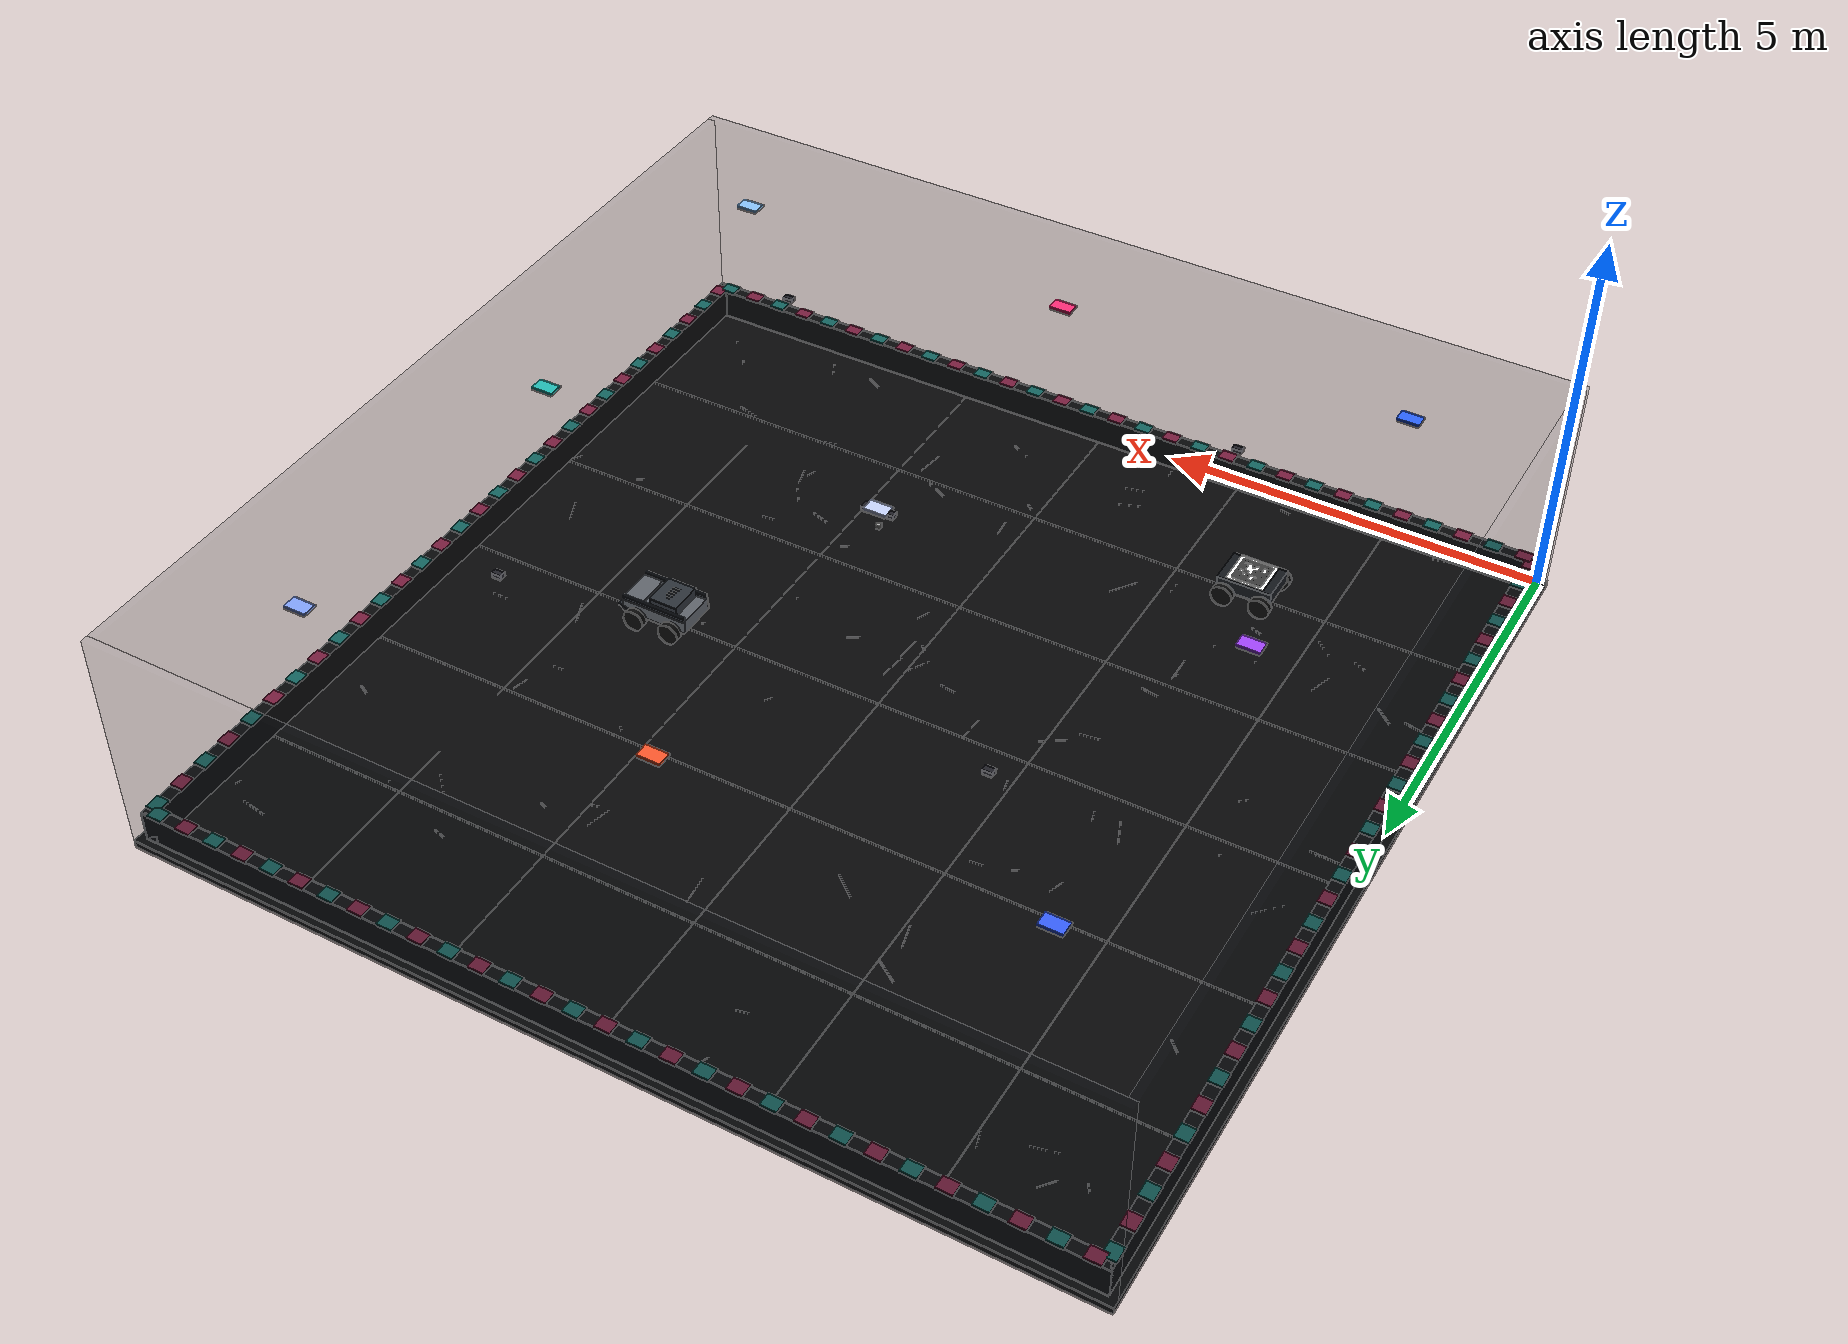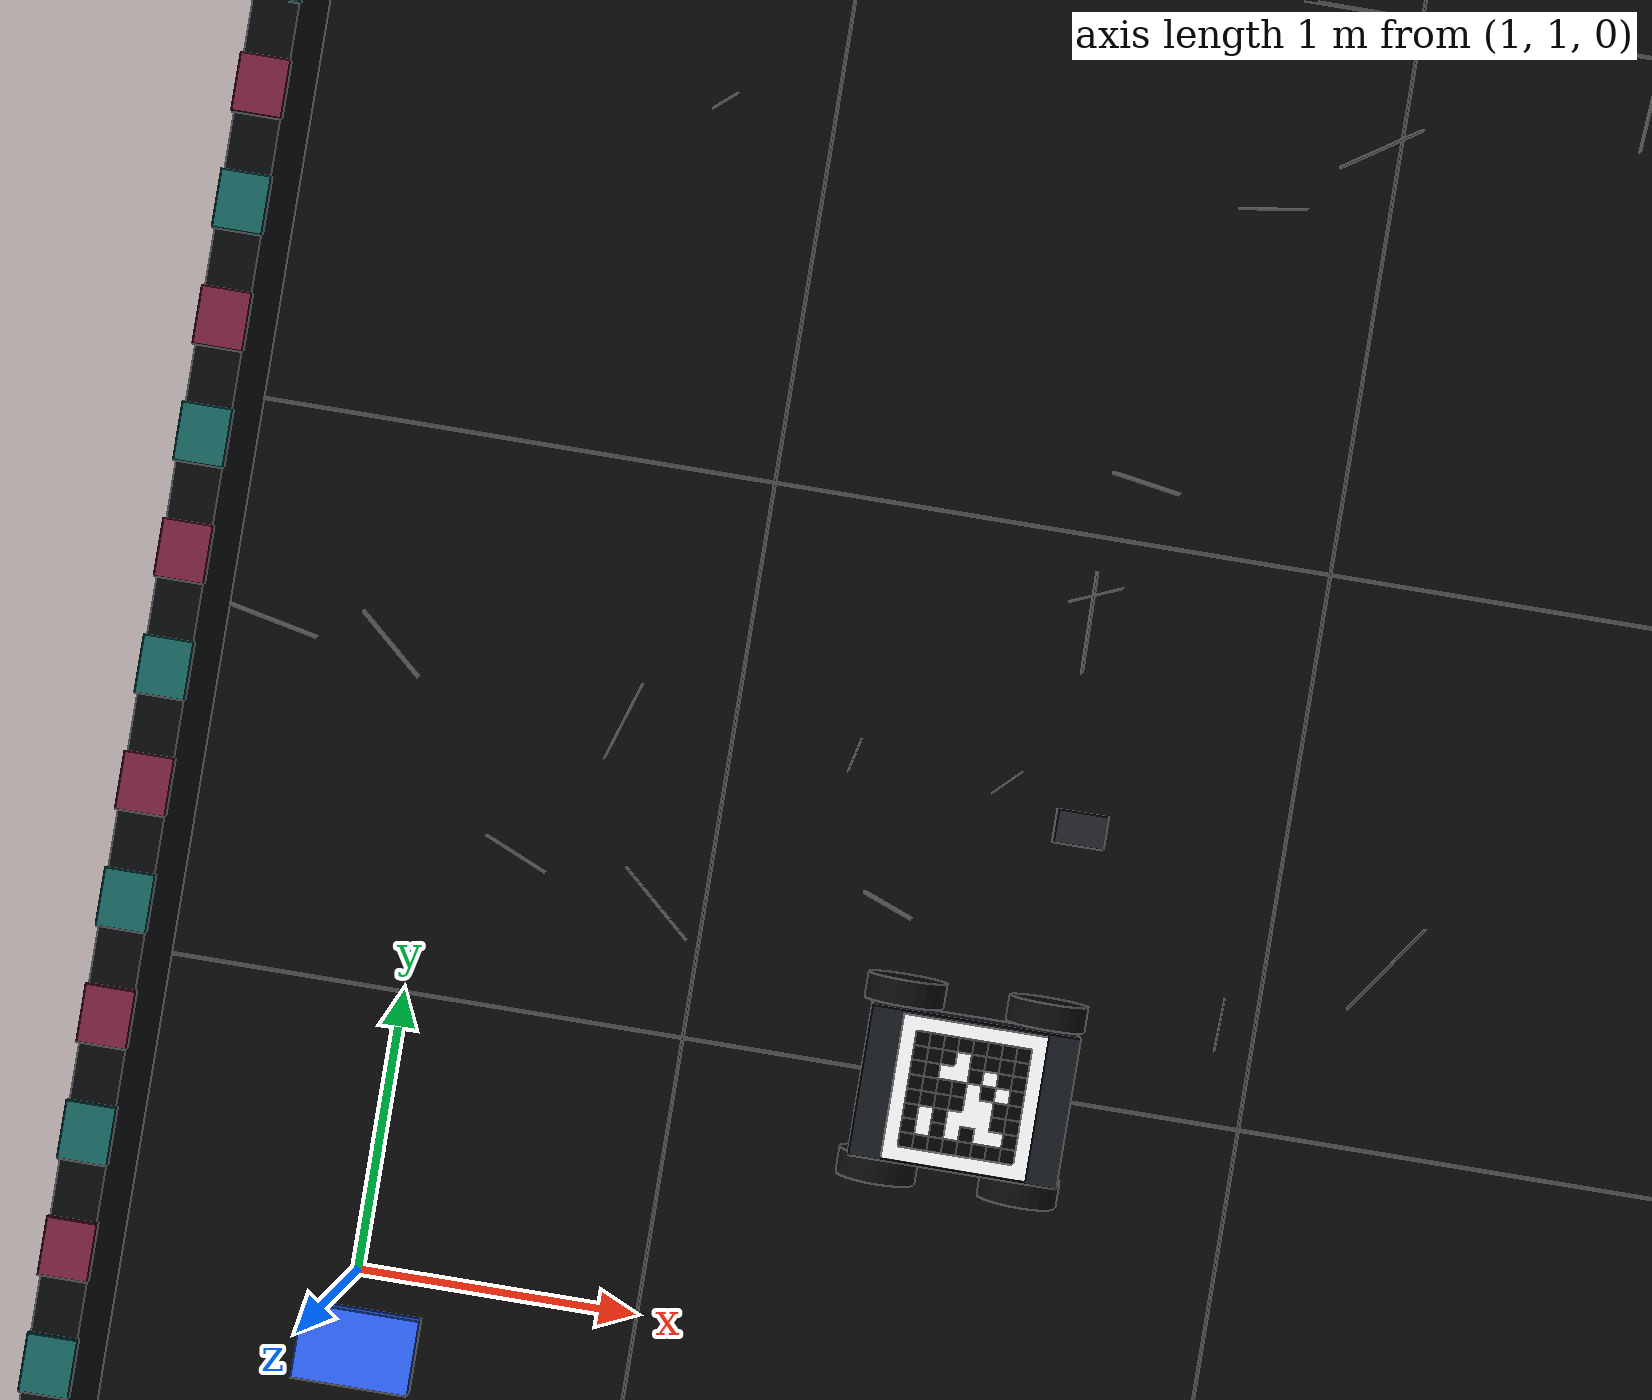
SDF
<?xml version='1.0' encoding='utf-8'?>
<sdf version="1.9">
  <world name="mocap_arena">
    <physics name="physics" type="ignored">
      <max_step_size>0.001</max_step_size>
      <real_time_factor>1</real_time_factor>
    </physics>
    <plugin filename="gz-sim-physics-system" name="gz::sim::systems::Physics" />
    <plugin filename="gz-sim-user-commands-system" name="gz::sim::systems::UserCommands" />
    <plugin filename="gz-sim-scene-broadcaster-system" name="gz::sim::systems::SceneBroadcaster" />
    <plugin filename="gz-sim-sensors-system" name="gz::sim::systems::Sensors">
      <render_engine>ogre2</render_engine>
    </plugin>
    <scene>
      <ambient>0.18 0.19 0.22 1</ambient>
      <background>0.018 0.022 0.03 1</background>
      <shadows>true</shadows>
    </scene>
    <light name="diffuse_fill" type="directional">
      <pose>6 6 2.8 0 0 0</pose>
      <diffuse>0.62 0.66 0.74 1</diffuse>
      <direction>0.15 0.1 -1</direction>
      <cast_shadows>false</cast_shadows>
      <intensity>1.0</intensity>
    </light>
    <model name="arena">
      <static>true</static>
      <link name="structure">
        <collision name="floor_collision">
          <pose>6 6 -0.05 0 0 0</pose>
          <geometry>
            <box>
              <size>12.2 12.2 0.1</size>
            </box>
          </geometry>
        </collision>
        <visual name="floor_visual">
          <pose>6 6 -0.05 0 0 0</pose>
          <geometry>
            <box>
              <size>12.2 12.2 0.1</size>
            </box>
          </geometry>
          <material>
            <ambient>0.028 0.030 0.035 1</ambient>
            <diffuse>0.028 0.030 0.035 1</diffuse>
            <pbr>
              <metal>
                <metalness>0.15</metalness>
                <roughness>0.58</roughness>
              </metal>
            </pbr>
          </material>
          <transparency>0</transparency>
        </visual>
        <visual name="seam_x_1_visual">
          <pose>2 6 0.0003 0 0 0</pose>
          <geometry>
            <box>
              <size>0.008 12 0.0005</size>
            </box>
          </geometry>
          <material>
            <ambient>0.012 0.014 0.016 1</ambient>
            <diffuse>0.012 0.014 0.016 1</diffuse>
            <pbr>
              <metal>
                <metalness>0.0</metalness>
                <roughness>0.75</roughness>
              </metal>
            </pbr>
          </material>
          <transparency>0</transparency>
        </visual>
        <visual name="seam_y_1_visual">
          <pose>6 2 0.0003 0 0 0</pose>
          <geometry>
            <box>
              <size>12 0.008 0.0005</size>
            </box>
          </geometry>
          <material>
            <ambient>0.012 0.014 0.016 1</ambient>
            <diffuse>0.012 0.014 0.016 1</diffuse>
            <pbr>
              <metal>
                <metalness>0.0</metalness>
                <roughness>0.75</roughness>
              </metal>
            </pbr>
          </material>
          <transparency>0</transparency>
        </visual>
        <visual name="seam_x_2_visual">
          <pose>4 6 0.0003 0 0 0</pose>
          <geometry>
            <box>
              <size>0.008 12 0.0005</size>
            </box>
          </geometry>
          <material>
            <ambient>0.012 0.014 0.016 1</ambient>
            <diffuse>0.012 0.014 0.016 1</diffuse>
            <pbr>
              <metal>
                <metalness>0.0</metalness>
                <roughness>0.75</roughness>
              </metal>
            </pbr>
          </material>
          <transparency>0</transparency>
        </visual>
        <visual name="seam_y_2_visual">
          <pose>6 4 0.0003 0 0 0</pose>
          <geometry>
            <box>
              <size>12 0.008 0.0005</size>
            </box>
          </geometry>
          <material>
            <ambient>0.012 0.014 0.016 1</ambient>
            <diffuse>0.012 0.014 0.016 1</diffuse>
            <pbr>
              <metal>
                <metalness>0.0</metalness>
                <roughness>0.75</roughness>
              </metal>
            </pbr>
          </material>
          <transparency>0</transparency>
        </visual>
        <visual name="seam_x_3_visual">
          <pose>6 6 0.0003 0 0 0</pose>
          <geometry>
            <box>
              <size>0.008 12 0.0005</size>
            </box>
          </geometry>
          <material>
            <ambient>0.012 0.014 0.016 1</ambient>
            <diffuse>0.012 0.014 0.016 1</diffuse>
            <pbr>
              <metal>
                <metalness>0.0</metalness>
                <roughness>0.75</roughness>
              </metal>
            </pbr>
          </material>
          <transparency>0</transparency>
        </visual>
        <visual name="seam_y_3_visual">
          <pose>6 6 0.0003 0 0 0</pose>
          <geometry>
            <box>
              <size>12 0.008 0.0005</size>
            </box>
          </geometry>
          <material>
            <ambient>0.012 0.014 0.016 1</ambient>
            <diffuse>0.012 0.014 0.016 1</diffuse>
            <pbr>
              <metal>
                <metalness>0.0</metalness>
                <roughness>0.75</roughness>
              </metal>
            </pbr>
          </material>
          <transparency>0</transparency>
        </visual>
        <visual name="seam_x_4_visual">
          <pose>8 6 0.0003 0 0 0</pose>
          <geometry>
            <box>
              <size>0.008 12 0.0005</size>
            </box>
          </geometry>
          <material>
            <ambient>0.012 0.014 0.016 1</ambient>
            <diffuse>0.012 0.014 0.016 1</diffuse>
            <pbr>
              <metal>
                <metalness>0.0</metalness>
                <roughness>0.75</roughness>
              </metal>
            </pbr>
          </material>
          <transparency>0</transparency>
        </visual>
        <visual name="seam_y_4_visual">
          <pose>6 8 0.0003 0 0 0</pose>
          <geometry>
            <box>
              <size>12 0.008 0.0005</size>
            </box>
          </geometry>
          <material>
            <ambient>0.012 0.014 0.016 1</ambient>
            <diffuse>0.012 0.014 0.016 1</diffuse>
            <pbr>
              <metal>
                <metalness>0.0</metalness>
                <roughness>0.75</roughness>
              </metal>
            </pbr>
          </material>
          <transparency>0</transparency>
        </visual>
        <visual name="seam_x_5_visual">
          <pose>10 6 0.0003 0 0 0</pose>
          <geometry>
            <box>
              <size>0.008 12 0.0005</size>
            </box>
          </geometry>
          <material>
            <ambient>0.012 0.014 0.016 1</ambient>
            <diffuse>0.012 0.014 0.016 1</diffuse>
            <pbr>
              <metal>
                <metalness>0.0</metalness>
                <roughness>0.75</roughness>
              </metal>
            </pbr>
          </material>
          <transparency>0</transparency>
        </visual>
        <visual name="seam_y_5_visual">
          <pose>6 10 0.0003 0 0 0</pose>
          <geometry>
            <box>
              <size>12 0.008 0.0005</size>
            </box>
          </geometry>
          <material>
            <ambient>0.012 0.014 0.016 1</ambient>
            <diffuse>0.012 0.014 0.016 1</diffuse>
            <pbr>
              <metal>
                <metalness>0.0</metalness>
                <roughness>0.75</roughness>
              </metal>
            </pbr>
          </material>
          <transparency>0</transparency>
        </visual>
        <visual name="scuff_0_visual">
          <pose>6.25721174363617 9.588282092288544 0.0007 0 0 1.6720023433033013</pose>
          <geometry>
            <box>
              <size>0.3873583277836406 0.0040273776443512585 0.0002</size>
            </box>
          </geometry>
          <material>
            <ambient>0.065 0.068 0.074 1</ambient>
            <diffuse>0.065 0.068 0.074 1</diffuse>
            <pbr>
              <metal>
                <metalness>0.0</metalness>
                <roughness>0.75</roughness>
              </metal>
            </pbr>
          </material>
          <transparency>0</transparency>
        </visual>
        <visual name="scuff_1_visual">
          <pose>8.389372442067927 7.888181769518815 0.0007 0 0 -0.7277744140741103</pose>
          <geometry>
            <box>
              <size>0.11525185565350779 0.002188557451533688 0.0002</size>
            </box>
          </geometry>
          <material>
            <ambient>0.065 0.068 0.074 1</ambient>
            <diffuse>0.065 0.068 0.074 1</diffuse>
            <pbr>
              <metal>
                <metalness>0.0</metalness>
                <roughness>0.75</roughness>
              </metal>
            </pbr>
          </material>
          <transparency>0</transparency>
        </visual>
        <visual name="scuff_2_visual">
          <pose>8.882823795146697 3.102890079904697 0.0007 0 0 2.17604180178341</pose>
          <geometry>
            <box>
              <size>0.2405128545817708 0.004222045633820248 0.0002</size>
            </box>
          </geometry>
          <material>
            <ambient>0.065 0.068 0.074 1</ambient>
            <diffuse>0.065 0.068 0.074 1</diffuse>
            <pbr>
              <metal>
                <metalness>0.0</metalness>
                <roughness>0.75</roughness>
              </metal>
            </pbr>
          </material>
          <transparency>0</transparency>
        </visual>
        <visual name="scuff_3_visual">
          <pose>11.208768799707205 4.848613961854833 0.0007 0 0 1.9641802784668556</pose>
          <geometry>
            <box>
              <size>0.3995030416278467 0.002435349538767127 0.0002</size>
            </box>
          </geometry>
          <material>
            <ambient>0.065 0.068 0.074 1</ambient>
            <diffuse>0.065 0.068 0.074 1</diffuse>
            <pbr>
              <metal>
                <metalness>0.0</metalness>
                <roughness>0.75</roughness>
              </metal>
            </pbr>
          </material>
          <transparency>0</transparency>
        </visual>
        <visual name="scuff_4_visual">
          <pose>10.391203074900883 1.9157111192406668 0.0007 0 0 2.8600296881639755</pose>
          <geometry>
            <box>
              <size>0.30578195698942423 0.005912243080232723 0.0002</size>
            </box>
          </geometry>
          <material>
            <ambient>0.065 0.068 0.074 1</ambient>
            <diffuse>0.065 0.068 0.074 1</diffuse>
            <pbr>
              <metal>
                <metalness>0.0</metalness>
                <roughness>0.75</roughness>
              </metal>
            </pbr>
          </material>
          <transparency>0</transparency>
        </visual>
        <visual name="scuff_5_visual">
          <pose>2.607117111035601 6.4675712022554475 0.0007 0 0 -1.1988347099688097</pose>
          <geometry>
            <box>
              <size>0.3623859541787841 0.0064714122674185744 0.0002</size>
            </box>
          </geometry>
          <material>
            <ambient>0.065 0.068 0.074 1</ambient>
            <diffuse>0.065 0.068 0.074 1</diffuse>
            <pbr>
              <metal>
                <metalness>0.0</metalness>
                <roughness>0.75</roughness>
              </metal>
            </pbr>
          </material>
          <transparency>0</transparency>
        </visual>
        <visual name="scuff_6_visual">
          <pose>1.1078070933764885 11.145379750037065 0.0007 0 0 -2.251848748253645</pose>
          <geometry>
            <box>
              <size>0.23171151075404972 0.00897428327947556 0.0002</size>
            </box>
          </geometry>
          <material>
            <ambient>0.065 0.068 0.074 1</ambient>
            <diffuse>0.065 0.068 0.074 1</diffuse>
            <pbr>
              <metal>
                <metalness>0.0</metalness>
                <roughness>0.75</roughness>
              </metal>
            </pbr>
          </material>
          <transparency>0</transparency>
        </visual>
        <visual name="scuff_7_visual">
          <pose>9.652789751302349 9.666524024464337 0.0007 0 0 -0.803036060078699</pose>
          <geometry>
            <box>
              <size>0.37439200719924487 0.00212484021506812 0.0002</size>
            </box>
          </geometry>
          <material>
            <ambient>0.065 0.068 0.074 1</ambient>
            <diffuse>0.065 0.068 0.074 1</diffuse>
            <pbr>
              <metal>
                <metalness>0.0</metalness>
                <roughness>0.75</roughness>
              </metal>
            </pbr>
          </material>
          <transparency>0</transparency>
        </visual>
        <visual name="scuff_8_visual">
          <pose>0.7545272223166292 8.948807552791978 0.0007 0 0 -0.786472503279505</pose>
          <geometry>
            <box>
              <size>0.19348535549711143 0.00871653653190033 0.0002</size>
            </box>
          </geometry>
          <material>
            <ambient>0.065 0.068 0.074 1</ambient>
            <diffuse>0.065 0.068 0.074 1</diffuse>
            <pbr>
              <metal>
                <metalness>0.0</metalness>
                <roughness>0.75</roughness>
              </metal>
            </pbr>
          </material>
          <transparency>0</transparency>
        </visual>
        <visual name="scuff_9_visual">
          <pose>9.210186618271072 10.303127502976787 0.0007 0 0 2.8738798270547568</pose>
          <geometry>
            <box>
              <size>0.15646290091774362 0.0058977163694568175 0.0002</size>
            </box>
          </geometry>
          <material>
            <ambient>0.065 0.068 0.074 1</ambient>
            <diffuse>0.065 0.068 0.074 1</diffuse>
            <pbr>
              <metal>
                <metalness>0.0</metalness>
                <roughness>0.75</roughness>
              </metal>
            </pbr>
          </material>
          <transparency>0</transparency>
        </visual>
        <visual name="scuff_10_visual">
          <pose>6.314937911191487 4.3585814690583256 0.0007 0 0 -1.9305243833026136</pose>
          <geometry>
            <box>
              <size>0.16550411478099347 0.0075052878478794735 0.0002</size>
            </box>
          </geometry>
          <material>
            <ambient>0.065 0.068 0.074 1</ambient>
            <diffuse>0.065 0.068 0.074 1</diffuse>
            <pbr>
              <metal>
                <metalness>0.0</metalness>
                <roughness>0.75</roughness>
              </metal>
            </pbr>
          </material>
          <transparency>0</transparency>
        </visual>
        <visual name="scuff_11_visual">
          <pose>7.215588235073804 6.6498932222846925 0.0007 0 0 0.9962941333864155</pose>
          <geometry>
            <box>
              <size>0.25711386418753246 0.0029064015578568383 0.0002</size>
            </box>
          </geometry>
          <material>
            <ambient>0.065 0.068 0.074 1</ambient>
            <diffuse>0.065 0.068 0.074 1</diffuse>
            <pbr>
              <metal>
                <metalness>0.0</metalness>
                <roughness>0.75</roughness>
              </metal>
            </pbr>
          </material>
          <transparency>0</transparency>
        </visual>
        <visual name="scuff_12_visual">
          <pose>10.873391943197788 3.8808842375688912 0.0007 0 0 0.4922573645261501</pose>
          <geometry>
            <box>
              <size>0.18626342080620134 0.008363285325649325 0.0002</size>
            </box>
          </geometry>
          <material>
            <ambient>0.065 0.068 0.074 1</ambient>
            <diffuse>0.065 0.068 0.074 1</diffuse>
            <pbr>
              <metal>
                <metalness>0.0</metalness>
                <roughness>0.75</roughness>
              </metal>
            </pbr>
          </material>
          <transparency>0</transparency>
        </visual>
        <visual name="scuff_13_visual">
          <pose>3.3391592414737175 0.2642312295162713 0.0007 0 0 -0.20634669022992558</pose>
          <geometry>
            <box>
              <size>0.3210462236178719 0.004436027989793612 0.0002</size>
            </box>
          </geometry>
          <material>
            <ambient>0.065 0.068 0.074 1</ambient>
            <diffuse>0.065 0.068 0.074 1</diffuse>
            <pbr>
              <metal>
                <metalness>0.0</metalness>
                <roughness>0.75</roughness>
              </metal>
            </pbr>
          </material>
          <transparency>0</transparency>
        </visual>
        <visual name="scuff_14_visual">
          <pose>3.3382849204807683 7.55729331471983 0.0007 0 0 -2.670166401472909</pose>
          <geometry>
            <box>
              <size>0.31327503490040315 0.004168516612101603 0.0002</size>
            </box>
          </geometry>
          <material>
            <ambient>0.065 0.068 0.074 1</ambient>
            <diffuse>0.065 0.068 0.074 1</diffuse>
            <pbr>
              <metal>
                <metalness>0.0</metalness>
                <roughness>0.75</roughness>
              </metal>
            </pbr>
          </material>
          <transparency>0</transparency>
        </visual>
        <visual name="scuff_15_visual">
          <pose>11.69544918067091 10.79748110155313 0.0007 0 0 1.168661968317359</pose>
          <geometry>
            <box>
              <size>0.08661164431824045 0.005949293678080596 0.0002</size>
            </box>
          </geometry>
          <material>
            <ambient>0.065 0.068 0.074 1</ambient>
            <diffuse>0.065 0.068 0.074 1</diffuse>
            <pbr>
              <metal>
                <metalness>0.0</metalness>
                <roughness>0.75</roughness>
              </metal>
            </pbr>
          </material>
          <transparency>0</transparency>
        </visual>
        <visual name="scuff_16_visual">
          <pose>4.865249159732447 8.710193529961881 0.0007 0 0 -0.6812617006358779</pose>
          <geometry>
            <box>
              <size>0.38714090580601784 0.006131025938057738 0.0002</size>
            </box>
          </geometry>
          <material>
            <ambient>0.065 0.068 0.074 1</ambient>
            <diffuse>0.065 0.068 0.074 1</diffuse>
            <pbr>
              <metal>
                <metalness>0.0</metalness>
                <roughness>0.75</roughness>
              </metal>
            </pbr>
          </material>
          <transparency>0</transparency>
        </visual>
        <visual name="scuff_17_visual">
          <pose>2.439083426044488 3.091596024055141 0.0007 0 0 -1.80710871445457</pose>
          <geometry>
            <box>
              <size>0.1282564751537083 0.0027728544872376304 0.0002</size>
            </box>
          </geometry>
          <material>
            <ambient>0.065 0.068 0.074 1</ambient>
            <diffuse>0.065 0.068 0.074 1</diffuse>
            <pbr>
              <metal>
                <metalness>0.0</metalness>
                <roughness>0.75</roughness>
              </metal>
            </pbr>
          </material>
          <transparency>0</transparency>
        </visual>
        <visual name="scuff_18_visual">
          <pose>10.001684179807564 6.432642178013383 0.0007 0 0 1.952717766407245</pose>
          <geometry>
            <box>
              <size>0.3375794479601721 0.008441300334100102 0.0002</size>
            </box>
          </geometry>
          <material>
            <ambient>0.065 0.068 0.074 1</ambient>
            <diffuse>0.065 0.068 0.074 1</diffuse>
            <pbr>
              <metal>
                <metalness>0.0</metalness>
                <roughness>0.75</roughness>
              </metal>
            </pbr>
          </material>
          <transparency>0</transparency>
        </visual>
        <visual name="scuff_19_visual">
          <pose>0.7284823185873468 10.983721103536126 0.0007 0 0 2.1296450420038022</pose>
          <geometry>
            <box>
              <size>0.10969350979645405 0.007396760353318199 0.0002</size>
            </box>
          </geometry>
          <material>
            <ambient>0.065 0.068 0.074 1</ambient>
            <diffuse>0.065 0.068 0.074 1</diffuse>
            <pbr>
              <metal>
                <metalness>0.0</metalness>
                <roughness>0.75</roughness>
              </metal>
            </pbr>
          </material>
          <transparency>0</transparency>
        </visual>
        <visual name="scuff_20_visual">
          <pose>7.842181015506801 4.873087385438216 0.0007 0 0 0.8576717927094375</pose>
          <geometry>
            <box>
              <size>0.10400546203169928 0.002596074251839787 0.0002</size>
            </box>
          </geometry>
          <material>
            <ambient>0.065 0.068 0.074 1</ambient>
            <diffuse>0.065 0.068 0.074 1</diffuse>
            <pbr>
              <metal>
                <metalness>0.0</metalness>
                <roughness>0.75</roughness>
              </metal>
            </pbr>
          </material>
          <transparency>0</transparency>
        </visual>
        <visual name="scuff_21_visual">
          <pose>2.9779403301458913 6.377704478856912 0.0007 0 0 -1.2865554612666237</pose>
          <geometry>
            <box>
              <size>0.16487267869944006 0.0031438635782123133 0.0002</size>
            </box>
          </geometry>
          <material>
            <ambient>0.065 0.068 0.074 1</ambient>
            <diffuse>0.065 0.068 0.074 1</diffuse>
            <pbr>
              <metal>
                <metalness>0.0</metalness>
                <roughness>0.75</roughness>
              </metal>
            </pbr>
          </material>
          <transparency>0</transparency>
        </visual>
        <visual name="scuff_22_visual">
          <pose>8.630941463158287 5.8457207095694725 0.0007 0 0 0.33919056648521506</pose>
          <geometry>
            <box>
              <size>0.2056863351451106 0.005405377205888304 0.0002</size>
            </box>
          </geometry>
          <material>
            <ambient>0.065 0.068 0.074 1</ambient>
            <diffuse>0.065 0.068 0.074 1</diffuse>
            <pbr>
              <metal>
                <metalness>0.0</metalness>
                <roughness>0.75</roughness>
              </metal>
            </pbr>
          </material>
          <transparency>0</transparency>
        </visual>
        <visual name="scuff_23_visual">
          <pose>6.183311874670264 5.357189800631839 0.0007 0 0 -1.702359031570995</pose>
          <geometry>
            <box>
              <size>0.38956343283499567 0.007262125257629297 0.0002</size>
            </box>
          </geometry>
          <material>
            <ambient>0.065 0.068 0.074 1</ambient>
            <diffuse>0.065 0.068 0.074 1</diffuse>
            <pbr>
              <metal>
                <metalness>0.0</metalness>
                <roughness>0.75</roughness>
              </metal>
            </pbr>
          </material>
          <transparency>0</transparency>
        </visual>
        <visual name="scuff_24_visual">
          <pose>3.873463446569153 2.358953542606383 0.0007 0 0 1.5362581453701747</pose>
          <geometry>
            <box>
              <size>0.19650948190250522 0.0021986460665673634 0.0002</size>
            </box>
          </geometry>
          <material>
            <ambient>0.065 0.068 0.074 1</ambient>
            <diffuse>0.065 0.068 0.074 1</diffuse>
            <pbr>
              <metal>
                <metalness>0.0</metalness>
                <roughness>0.75</roughness>
              </metal>
            </pbr>
          </material>
          <transparency>0</transparency>
        </visual>
        <visual name="scuff_25_visual">
          <pose>6.79430122880262 5.095365569950164 0.0007 0 0 0.4937589685593635</pose>
          <geometry>
            <box>
              <size>0.3658996959502137 0.004301224282015686 0.0002</size>
            </box>
          </geometry>
          <material>
            <ambient>0.065 0.068 0.074 1</ambient>
            <diffuse>0.065 0.068 0.074 1</diffuse>
            <pbr>
              <metal>
                <metalness>0.0</metalness>
                <roughness>0.75</roughness>
              </metal>
            </pbr>
          </material>
          <transparency>0</transparency>
        </visual>
        <visual name="scuff_26_visual">
          <pose>11.028158192974777 6.653558944194472 0.0007 0 0 3.129639885989536</pose>
          <geometry>
            <box>
              <size>0.27615213945739475 0.004575677858331342 0.0002</size>
            </box>
          </geometry>
          <material>
            <ambient>0.065 0.068 0.074 1</ambient>
            <diffuse>0.065 0.068 0.074 1</diffuse>
            <pbr>
              <metal>
                <metalness>0.0</metalness>
                <roughness>0.75</roughness>
              </metal>
            </pbr>
          </material>
          <transparency>0</transparency>
        </visual>
        <visual name="scuff_27_visual">
          <pose>8.98095419756649 3.69913717415673 0.0007 0 0 0.11709524494040346</pose>
          <geometry>
            <box>
              <size>0.1937650309778623 0.0061405627925244744 0.0002</size>
            </box>
          </geometry>
          <material>
            <ambient>0.065 0.068 0.074 1</ambient>
            <diffuse>0.065 0.068 0.074 1</diffuse>
            <pbr>
              <metal>
                <metalness>0.0</metalness>
                <roughness>0.75</roughness>
              </metal>
            </pbr>
          </material>
          <transparency>0</transparency>
        </visual>
        <visual name="scuff_28_visual">
          <pose>6.272684440187647 2.3974447684274267 0.0007 0 0 1.6649903767570677</pose>
          <geometry>
            <box>
              <size>0.26422489618927136 0.006927629030304341 0.0002</size>
            </box>
          </geometry>
          <material>
            <ambient>0.065 0.068 0.074 1</ambient>
            <diffuse>0.065 0.068 0.074 1</diffuse>
            <pbr>
              <metal>
                <metalness>0.0</metalness>
                <roughness>0.75</roughness>
              </metal>
            </pbr>
          </material>
          <transparency>0</transparency>
        </visual>
        <visual name="scuff_29_visual">
          <pose>5.407748166654591 5.363025758499003 0.0007 0 0 -0.1575424928064426</pose>
          <geometry>
            <box>
              <size>0.24136239799776538 0.005753772317212896 0.0002</size>
            </box>
          </geometry>
          <material>
            <ambient>0.065 0.068 0.074 1</ambient>
            <diffuse>0.065 0.068 0.074 1</diffuse>
            <pbr>
              <metal>
                <metalness>0.0</metalness>
                <roughness>0.75</roughness>
              </metal>
            </pbr>
          </material>
          <transparency>0</transparency>
        </visual>
        <visual name="scuff_30_visual">
          <pose>0.2915704171551393 3.2320998009541944 0.0007 0 0 -0.20500138642473864</pose>
          <geometry>
            <box>
              <size>0.396098296661822 0.007784241820202236 0.0002</size>
            </box>
          </geometry>
          <material>
            <ambient>0.065 0.068 0.074 1</ambient>
            <diffuse>0.065 0.068 0.074 1</diffuse>
            <pbr>
              <metal>
                <metalness>0.0</metalness>
                <roughness>0.75</roughness>
              </metal>
            </pbr>
          </material>
          <transparency>0</transparency>
        </visual>
        <visual name="scuff_31_visual">
          <pose>8.948141786056718 2.62161297132136 0.0007 0 0 1.2522066627326893</pose>
          <geometry>
            <box>
              <size>0.1654948451484252 0.0056234058862178506 0.0002</size>
            </box>
          </geometry>
          <material>
            <ambient>0.065 0.068 0.074 1</ambient>
            <diffuse>0.065 0.068 0.074 1</diffuse>
            <pbr>
              <metal>
                <metalness>0.0</metalness>
                <roughness>0.75</roughness>
              </metal>
            </pbr>
          </material>
          <transparency>0</transparency>
        </visual>
        <visual name="scuff_32_visual">
          <pose>0.47250086232958066 5.6690329105389194 0.0007 0 0 3.0981837677088606</pose>
          <geometry>
            <box>
              <size>0.36994699073174797 0.0062858025836078895 0.0002</size>
            </box>
          </geometry>
          <material>
            <ambient>0.065 0.068 0.074 1</ambient>
            <diffuse>0.065 0.068 0.074 1</diffuse>
            <pbr>
              <metal>
                <metalness>0.0</metalness>
                <roughness>0.75</roughness>
              </metal>
            </pbr>
          </material>
          <transparency>0</transparency>
        </visual>
        <visual name="scuff_33_visual">
          <pose>1.3046449482672433 10.780638494297946 0.0007 0 0 0.2298733886796751</pose>
          <geometry>
            <box>
              <size>0.34796732183764445 0.002183109344449098 0.0002</size>
            </box>
          </geometry>
          <material>
            <ambient>0.065 0.068 0.074 1</ambient>
            <diffuse>0.065 0.068 0.074 1</diffuse>
            <pbr>
              <metal>
                <metalness>0.0</metalness>
                <roughness>0.75</roughness>
              </metal>
            </pbr>
          </material>
          <transparency>0</transparency>
        </visual>
        <visual name="scuff_34_visual">
          <pose>9.033571502648016 2.7480162393142074 0.0007 0 0 1.8469226583562612</pose>
          <geometry>
            <box>
              <size>0.28777673251612446 0.00795352908819806 0.0002</size>
            </box>
          </geometry>
          <material>
            <ambient>0.065 0.068 0.074 1</ambient>
            <diffuse>0.065 0.068 0.074 1</diffuse>
            <pbr>
              <metal>
                <metalness>0.0</metalness>
                <roughness>0.75</roughness>
              </metal>
            </pbr>
          </material>
          <transparency>0</transparency>
        </visual>
        <visual name="scuff_35_visual">
          <pose>5.158868469191056 0.8326522256325112 0.0007 0 0 0.24316667673714454</pose>
          <geometry>
            <box>
              <size>0.25253507389979235 0.0033165592537876976 0.0002</size>
            </box>
          </geometry>
          <material>
            <ambient>0.065 0.068 0.074 1</ambient>
            <diffuse>0.065 0.068 0.074 1</diffuse>
            <pbr>
              <metal>
                <metalness>0.0</metalness>
                <roughness>0.75</roughness>
              </metal>
            </pbr>
          </material>
          <transparency>0</transparency>
        </visual>
        <visual name="scuff_36_visual">
          <pose>3.302389570889651 4.213572314375397 0.0007 0 0 2.986515117537416</pose>
          <geometry>
            <box>
              <size>0.2539943398982934 0.007737100183901492 0.0002</size>
            </box>
          </geometry>
          <material>
            <ambient>0.065 0.068 0.074 1</ambient>
            <diffuse>0.065 0.068 0.074 1</diffuse>
            <pbr>
              <metal>
                <metalness>0.0</metalness>
                <roughness>0.75</roughness>
              </metal>
            </pbr>
          </material>
          <transparency>0</transparency>
        </visual>
        <visual name="scuff_37_visual">
          <pose>4.894697746495432 0.23722972088548241 0.0007 0 0 1.6187230093729577</pose>
          <geometry>
            <box>
              <size>0.32005090235383826 0.004374831770110235 0.0002</size>
            </box>
          </geometry>
          <material>
            <ambient>0.065 0.068 0.074 1</ambient>
            <diffuse>0.065 0.068 0.074 1</diffuse>
            <pbr>
              <metal>
                <metalness>0.0</metalness>
                <roughness>0.75</roughness>
              </metal>
            </pbr>
          </material>
          <transparency>0</transparency>
        </visual>
        <visual name="scuff_38_visual">
          <pose>9.867709399685024 0.5422505455412199 0.0007 0 0 -1.1206424779187683</pose>
          <geometry>
            <box>
              <size>0.31386641231804724 0.003993803212625162 0.0002</size>
            </box>
          </geometry>
          <material>
            <ambient>0.065 0.068 0.074 1</ambient>
            <diffuse>0.065 0.068 0.074 1</diffuse>
            <pbr>
              <metal>
                <metalness>0.0</metalness>
                <roughness>0.75</roughness>
              </metal>
            </pbr>
          </material>
          <transparency>0</transparency>
        </visual>
        <visual name="scuff_39_visual">
          <pose>4.060692880964759 6.449049350571279 0.0007 0 0 -1.361507219707606</pose>
          <geometry>
            <box>
              <size>0.15784235220835952 0.005461277423447735 0.0002</size>
            </box>
          </geometry>
          <material>
            <ambient>0.065 0.068 0.074 1</ambient>
            <diffuse>0.065 0.068 0.074 1</diffuse>
            <pbr>
              <metal>
                <metalness>0.0</metalness>
                <roughness>0.75</roughness>
              </metal>
            </pbr>
          </material>
          <transparency>0</transparency>
        </visual>
        <visual name="scuff_40_visual">
          <pose>1.608220323048048 3.0747285534616524 0.0007 0 0 -1.883029320739382</pose>
          <geometry>
            <box>
              <size>0.29790038447495737 0.004173620326773134 0.0002</size>
            </box>
          </geometry>
          <material>
            <ambient>0.065 0.068 0.074 1</ambient>
            <diffuse>0.065 0.068 0.074 1</diffuse>
            <pbr>
              <metal>
                <metalness>0.0</metalness>
                <roughness>0.75</roughness>
              </metal>
            </pbr>
          </material>
          <transparency>0</transparency>
        </visual>
        <visual name="scuff_41_visual">
          <pose>4.427203372120291 2.649463962813877 0.0007 0 0 -2.1887224941747254</pose>
          <geometry>
            <box>
              <size>0.39503472560630926 0.007510670475693167 0.0002</size>
            </box>
          </geometry>
          <material>
            <ambient>0.065 0.068 0.074 1</ambient>
            <diffuse>0.065 0.068 0.074 1</diffuse>
            <pbr>
              <metal>
                <metalness>0.0</metalness>
                <roughness>0.75</roughness>
              </metal>
            </pbr>
          </material>
          <transparency>0</transparency>
        </visual>
        <visual name="scuff_42_visual">
          <pose>3.5876349186422125 5.249953358762416 0.0007 0 0 0.14654729682844359</pose>
          <geometry>
            <box>
              <size>0.24898404812206737 0.004719073142611352 0.0002</size>
            </box>
          </geometry>
          <material>
            <ambient>0.065 0.068 0.074 1</ambient>
            <diffuse>0.065 0.068 0.074 1</diffuse>
            <pbr>
              <metal>
                <metalness>0.0</metalness>
                <roughness>0.75</roughness>
              </metal>
            </pbr>
          </material>
          <transparency>0</transparency>
        </visual>
        <visual name="scuff_43_visual">
          <pose>9.043507690208626 1.9535448786617224 0.0007 0 0 0.21860209007839693</pose>
          <geometry>
            <box>
              <size>0.2589507845465105 0.003151275076756121 0.0002</size>
            </box>
          </geometry>
          <material>
            <ambient>0.065 0.068 0.074 1</ambient>
            <diffuse>0.065 0.068 0.074 1</diffuse>
            <pbr>
              <metal>
                <metalness>0.0</metalness>
                <roughness>0.75</roughness>
              </metal>
            </pbr>
          </material>
          <transparency>0</transparency>
        </visual>
        <visual name="scuff_44_visual">
          <pose>3.8600658980768374 9.547059124082944 0.0007 0 0 -0.5834356485655472</pose>
          <geometry>
            <box>
              <size>0.36192324943916265 0.008696845580128619 0.0002</size>
            </box>
          </geometry>
          <material>
            <ambient>0.065 0.068 0.074 1</ambient>
            <diffuse>0.065 0.068 0.074 1</diffuse>
            <pbr>
              <metal>
                <metalness>0.0</metalness>
                <roughness>0.75</roughness>
              </metal>
            </pbr>
          </material>
          <transparency>0</transparency>
        </visual>
        <visual name="scuff_45_visual">
          <pose>7.3657939870885505 2.122979667454216 0.0007 0 0 -0.45854090265642444</pose>
          <geometry>
            <box>
              <size>0.3077188805363833 0.007446155411373068 0.0002</size>
            </box>
          </geometry>
          <material>
            <ambient>0.065 0.068 0.074 1</ambient>
            <diffuse>0.065 0.068 0.074 1</diffuse>
            <pbr>
              <metal>
                <metalness>0.0</metalness>
                <roughness>0.75</roughness>
              </metal>
            </pbr>
          </material>
          <transparency>0</transparency>
        </visual>
        <visual name="scuff_46_visual">
          <pose>3.9137918831715366 9.019403342048598 0.0007 0 0 -1.3277854601333667</pose>
          <geometry>
            <box>
              <size>0.3201117599054451 0.00759516076668754 0.0002</size>
            </box>
          </geometry>
          <material>
            <ambient>0.065 0.068 0.074 1</ambient>
            <diffuse>0.065 0.068 0.074 1</diffuse>
            <pbr>
              <metal>
                <metalness>0.0</metalness>
                <roughness>0.75</roughness>
              </metal>
            </pbr>
          </material>
          <transparency>0</transparency>
        </visual>
        <visual name="scuff_47_visual">
          <pose>2.9884386271237715 3.0825405782294872 0.0007 0 0 -2.372373693079245</pose>
          <geometry>
            <box>
              <size>0.14112638085474577 0.002049092080058744 0.0002</size>
            </box>
          </geometry>
          <material>
            <ambient>0.065 0.068 0.074 1</ambient>
            <diffuse>0.065 0.068 0.074 1</diffuse>
            <pbr>
              <metal>
                <metalness>0.0</metalness>
                <roughness>0.75</roughness>
              </metal>
            </pbr>
          </material>
          <transparency>0</transparency>
        </visual>
        <visual name="scuff_48_visual">
          <pose>5.914747039223019 5.18737470293751 0.0007 0 0 -2.0713558636331513</pose>
          <geometry>
            <box>
              <size>0.36469789389429014 0.004647513931293838 0.0002</size>
            </box>
          </geometry>
          <material>
            <ambient>0.065 0.068 0.074 1</ambient>
            <diffuse>0.065 0.068 0.074 1</diffuse>
            <pbr>
              <metal>
                <metalness>0.0</metalness>
                <roughness>0.75</roughness>
              </metal>
            </pbr>
          </material>
          <transparency>0</transparency>
        </visual>
        <visual name="scuff_49_visual">
          <pose>11.041081614577278 1.0019502690082682 0.0007 0 0 -1.1225056957434667</pose>
          <geometry>
            <box>
              <size>0.188726513163909 0.007345311732872711 0.0002</size>
            </box>
          </geometry>
          <material>
            <ambient>0.065 0.068 0.074 1</ambient>
            <diffuse>0.065 0.068 0.074 1</diffuse>
            <pbr>
              <metal>
                <metalness>0.0</metalness>
                <roughness>0.75</roughness>
              </metal>
            </pbr>
          </material>
          <transparency>0</transparency>
        </visual>
        <visual name="scuff_50_visual">
          <pose>11.428273252018581 8.848911513482744 0.0007 0 0 2.650057963909637</pose>
          <geometry>
            <box>
              <size>0.1786581096253821 0.008044006632854935 0.0002</size>
            </box>
          </geometry>
          <material>
            <ambient>0.065 0.068 0.074 1</ambient>
            <diffuse>0.065 0.068 0.074 1</diffuse>
            <pbr>
              <metal>
                <metalness>0.0</metalness>
                <roughness>0.75</roughness>
              </metal>
            </pbr>
          </material>
          <transparency>0</transparency>
        </visual>
        <visual name="scuff_51_visual">
          <pose>6.163739541156273 1.829528251319565 0.0007 0 0 2.4376296851503225</pose>
          <geometry>
            <box>
              <size>0.11330805527879559 0.0077255024111591445 0.0002</size>
            </box>
          </geometry>
          <material>
            <ambient>0.065 0.068 0.074 1</ambient>
            <diffuse>0.065 0.068 0.074 1</diffuse>
            <pbr>
              <metal>
                <metalness>0.0</metalness>
                <roughness>0.75</roughness>
              </metal>
            </pbr>
          </material>
          <transparency>0</transparency>
        </visual>
        <visual name="scuff_52_visual">
          <pose>7.800306530439115 9.204207931515636 0.0007 0 0 -1.801824350328734</pose>
          <geometry>
            <box>
              <size>0.3339707571445704 0.0036599080377593927 0.0002</size>
            </box>
          </geometry>
          <material>
            <ambient>0.065 0.068 0.074 1</ambient>
            <diffuse>0.065 0.068 0.074 1</diffuse>
            <pbr>
              <metal>
                <metalness>0.0</metalness>
                <roughness>0.75</roughness>
              </metal>
            </pbr>
          </material>
          <transparency>0</transparency>
        </visual>
        <visual name="scuff_53_visual">
          <pose>10.301123507480046 9.969191657021307 0.0007 0 0 -2.646806780270698</pose>
          <geometry>
            <box>
              <size>0.21957267850744805 0.003891671975063288 0.0002</size>
            </box>
          </geometry>
          <material>
            <ambient>0.065 0.068 0.074 1</ambient>
            <diffuse>0.065 0.068 0.074 1</diffuse>
            <pbr>
              <metal>
                <metalness>0.0</metalness>
                <roughness>0.75</roughness>
              </metal>
            </pbr>
          </material>
          <transparency>0</transparency>
        </visual>
        <visual name="scuff_54_visual">
          <pose>4.881870596589177 10.785153193510702 0.0007 0 0 -2.920518726626512</pose>
          <geometry>
            <box>
              <size>0.1450808546096845 0.0042109668782606795 0.0002</size>
            </box>
          </geometry>
          <material>
            <ambient>0.065 0.068 0.074 1</ambient>
            <diffuse>0.065 0.068 0.074 1</diffuse>
            <pbr>
              <metal>
                <metalness>0.0</metalness>
                <roughness>0.75</roughness>
              </metal>
            </pbr>
          </material>
          <transparency>0</transparency>
        </visual>
        <visual name="scuff_55_visual">
          <pose>6.806032029614177 0.8529871919654597 0.0007 0 0 -0.48274468038243334</pose>
          <geometry>
            <box>
              <size>0.29596662199499546 0.005444222344662835 0.0002</size>
            </box>
          </geometry>
          <material>
            <ambient>0.065 0.068 0.074 1</ambient>
            <diffuse>0.065 0.068 0.074 1</diffuse>
            <pbr>
              <metal>
                <metalness>0.0</metalness>
                <roughness>0.75</roughness>
              </metal>
            </pbr>
          </material>
          <transparency>0</transparency>
        </visual>
        <visual name="scuff_56_visual">
          <pose>3.184044040478931 3.6901966620770588 0.0007 0 0 1.5832330224268691</pose>
          <geometry>
            <box>
              <size>0.3657679814628348 0.00858526421439974 0.0002</size>
            </box>
          </geometry>
          <material>
            <ambient>0.065 0.068 0.074 1</ambient>
            <diffuse>0.065 0.068 0.074 1</diffuse>
            <pbr>
              <metal>
                <metalness>0.0</metalness>
                <roughness>0.75</roughness>
              </metal>
            </pbr>
          </material>
          <transparency>0</transparency>
        </visual>
        <visual name="scuff_57_visual">
          <pose>2.6418411978735254 2.58420893244701 0.0007 0 0 2.782471506712114</pose>
          <geometry>
            <box>
              <size>0.19608436760222875 0.008130883223938764 0.0002</size>
            </box>
          </geometry>
          <material>
            <ambient>0.065 0.068 0.074 1</ambient>
            <diffuse>0.065 0.068 0.074 1</diffuse>
            <pbr>
              <metal>
                <metalness>0.0</metalness>
                <roughness>0.75</roughness>
              </metal>
            </pbr>
          </material>
          <transparency>0</transparency>
        </visual>
        <visual name="scuff_58_visual">
          <pose>2.8408045019442754 7.560973427830838 0.0007 0 0 -1.8998590171856806</pose>
          <geometry>
            <box>
              <size>0.2015157176765084 0.005188963365649341 0.0002</size>
            </box>
          </geometry>
          <material>
            <ambient>0.065 0.068 0.074 1</ambient>
            <diffuse>0.065 0.068 0.074 1</diffuse>
            <pbr>
              <metal>
                <metalness>0.0</metalness>
                <roughness>0.75</roughness>
              </metal>
            </pbr>
          </material>
          <transparency>0</transparency>
        </visual>
        <visual name="scuff_59_visual">
          <pose>8.592424485513462 9.300112440161714 0.0007 0 0 -0.3662222393348089</pose>
          <geometry>
            <box>
              <size>0.3806285228351522 0.005389297404613398 0.0002</size>
            </box>
          </geometry>
          <material>
            <ambient>0.065 0.068 0.074 1</ambient>
            <diffuse>0.065 0.068 0.074 1</diffuse>
            <pbr>
              <metal>
                <metalness>0.0</metalness>
                <roughness>0.75</roughness>
              </metal>
            </pbr>
          </material>
          <transparency>0</transparency>
        </visual>
        <visual name="scuff_60_visual">
          <pose>7.711625310986683 1.6861281063959146 0.0007 0 0 -1.7106638558881868</pose>
          <geometry>
            <box>
              <size>0.36110772952073816 0.007375900505157497 0.0002</size>
            </box>
          </geometry>
          <material>
            <ambient>0.065 0.068 0.074 1</ambient>
            <diffuse>0.065 0.068 0.074 1</diffuse>
            <pbr>
              <metal>
                <metalness>0.0</metalness>
                <roughness>0.75</roughness>
              </metal>
            </pbr>
          </material>
          <transparency>0</transparency>
        </visual>
        <visual name="scuff_61_visual">
          <pose>4.851558471677979 5.836571484906336 0.0007 0 0 -1.6388903029065907</pose>
          <geometry>
            <box>
              <size>0.35260692327405374 0.006849210869976983 0.0002</size>
            </box>
          </geometry>
          <material>
            <ambient>0.065 0.068 0.074 1</ambient>
            <diffuse>0.065 0.068 0.074 1</diffuse>
            <pbr>
              <metal>
                <metalness>0.0</metalness>
                <roughness>0.75</roughness>
              </metal>
            </pbr>
          </material>
          <transparency>0</transparency>
        </visual>
        <visual name="scuff_62_visual">
          <pose>11.278345895669256 11.029933642634969 0.0007 0 0 -0.16836314097795313</pose>
          <geometry>
            <box>
              <size>0.354496527131901 0.005448739231237624 0.0002</size>
            </box>
          </geometry>
          <material>
            <ambient>0.065 0.068 0.074 1</ambient>
            <diffuse>0.065 0.068 0.074 1</diffuse>
            <pbr>
              <metal>
                <metalness>0.0</metalness>
                <roughness>0.75</roughness>
              </metal>
            </pbr>
          </material>
          <transparency>0</transparency>
        </visual>
        <visual name="scuff_63_visual">
          <pose>4.90626317349138 11.589430753216378 0.0007 0 0 -1.985714559535976</pose>
          <geometry>
            <box>
              <size>0.23407280707232064 0.008716573066639824 0.0002</size>
            </box>
          </geometry>
          <material>
            <ambient>0.065 0.068 0.074 1</ambient>
            <diffuse>0.065 0.068 0.074 1</diffuse>
            <pbr>
              <metal>
                <metalness>0.0</metalness>
                <roughness>0.75</roughness>
              </metal>
            </pbr>
          </material>
          <transparency>0</transparency>
        </visual>
        <visual name="scuff_64_visual">
          <pose>0.5045232593706568 5.674299430910186 0.0007 0 0 -2.9153886830953795</pose>
          <geometry>
            <box>
              <size>0.1436131218833947 0.0037960319670034713 0.0002</size>
            </box>
          </geometry>
          <material>
            <ambient>0.065 0.068 0.074 1</ambient>
            <diffuse>0.065 0.068 0.074 1</diffuse>
            <pbr>
              <metal>
                <metalness>0.0</metalness>
                <roughness>0.75</roughness>
              </metal>
            </pbr>
          </material>
          <transparency>0</transparency>
        </visual>
        <visual name="scuff_65_visual">
          <pose>1.6056219093936548 5.310950044037842 0.0007 0 0 0.7068642570776067</pose>
          <geometry>
            <box>
              <size>0.10801428770791908 0.004074608869394971 0.0002</size>
            </box>
          </geometry>
          <material>
            <ambient>0.065 0.068 0.074 1</ambient>
            <diffuse>0.065 0.068 0.074 1</diffuse>
            <pbr>
              <metal>
                <metalness>0.0</metalness>
                <roughness>0.75</roughness>
              </metal>
            </pbr>
          </material>
          <transparency>0</transparency>
        </visual>
        <visual name="scuff_66_visual">
          <pose>3.1914483988031113 3.7930844133608823 0.0007 0 0 0.3981971741525503</pose>
          <geometry>
            <box>
              <size>0.20109489087430216 0.0038429404099635427 0.0002</size>
            </box>
          </geometry>
          <material>
            <ambient>0.065 0.068 0.074 1</ambient>
            <diffuse>0.065 0.068 0.074 1</diffuse>
            <pbr>
              <metal>
                <metalness>0.0</metalness>
                <roughness>0.75</roughness>
              </metal>
            </pbr>
          </material>
          <transparency>0</transparency>
        </visual>
        <visual name="scuff_67_visual">
          <pose>9.23911785914472 0.5140518724757842 0.0007 0 0 2.627994701426659</pose>
          <geometry>
            <box>
              <size>0.2516692645190555 0.005743196623643595 0.0002</size>
            </box>
          </geometry>
          <material>
            <ambient>0.065 0.068 0.074 1</ambient>
            <diffuse>0.065 0.068 0.074 1</diffuse>
            <pbr>
              <metal>
                <metalness>0.0</metalness>
                <roughness>0.75</roughness>
              </metal>
            </pbr>
          </material>
          <transparency>0</transparency>
        </visual>
        <visual name="scuff_68_visual">
          <pose>8.387912620978256 3.3637843105666314 0.0007 0 0 2.8363536125466746</pose>
          <geometry>
            <box>
              <size>0.27714603269458343 0.008304667229742244 0.0002</size>
            </box>
          </geometry>
          <material>
            <ambient>0.065 0.068 0.074 1</ambient>
            <diffuse>0.065 0.068 0.074 1</diffuse>
            <pbr>
              <metal>
                <metalness>0.0</metalness>
                <roughness>0.75</roughness>
              </metal>
            </pbr>
          </material>
          <transparency>0</transparency>
        </visual>
        <visual name="scuff_69_visual">
          <pose>9.129816011828968 1.4086351671037953 0.0007 0 0 -1.0727552152064113</pose>
          <geometry>
            <box>
              <size>0.19901793330247985 0.005350899272599607 0.0002</size>
            </box>
          </geometry>
          <material>
            <ambient>0.065 0.068 0.074 1</ambient>
            <diffuse>0.065 0.068 0.074 1</diffuse>
            <pbr>
              <metal>
                <metalness>0.0</metalness>
                <roughness>0.75</roughness>
              </metal>
            </pbr>
          </material>
          <transparency>0</transparency>
        </visual>
        <visual name="scuff_70_visual">
          <pose>9.026327096932219 5.917896494214648 0.0007 0 0 1.9346247925598554</pose>
          <geometry>
            <box>
              <size>0.3931356292241154 0.0020547766626362726 0.0002</size>
            </box>
          </geometry>
          <material>
            <ambient>0.065 0.068 0.074 1</ambient>
            <diffuse>0.065 0.068 0.074 1</diffuse>
            <pbr>
              <metal>
                <metalness>0.0</metalness>
                <roughness>0.75</roughness>
              </metal>
            </pbr>
          </material>
          <transparency>0</transparency>
        </visual>
        <visual name="scuff_71_visual">
          <pose>1.4788998430619253 6.217425610990998 0.0007 0 0 0.6993835686789045</pose>
          <geometry>
            <box>
              <size>0.1276393100060102 0.004676053254352883 0.0002</size>
            </box>
          </geometry>
          <material>
            <ambient>0.065 0.068 0.074 1</ambient>
            <diffuse>0.065 0.068 0.074 1</diffuse>
            <pbr>
              <metal>
                <metalness>0.0</metalness>
                <roughness>0.75</roughness>
              </metal>
            </pbr>
          </material>
          <transparency>0</transparency>
        </visual>
        <visual name="scuff_72_visual">
          <pose>11.36804320309835 0.6282937329277019 0.0007 0 0 1.5267450059852168</pose>
          <geometry>
            <box>
              <size>0.20535341725008588 0.002766513740536579 0.0002</size>
            </box>
          </geometry>
          <material>
            <ambient>0.065 0.068 0.074 1</ambient>
            <diffuse>0.065 0.068 0.074 1</diffuse>
            <pbr>
              <metal>
                <metalness>0.0</metalness>
                <roughness>0.75</roughness>
              </metal>
            </pbr>
          </material>
          <transparency>0</transparency>
        </visual>
        <visual name="scuff_73_visual">
          <pose>1.8300233185074783 2.453866328352369 0.0007 0 0 2.4209893949582035</pose>
          <geometry>
            <box>
              <size>0.33881732807747555 0.0023295733015878776 0.0002</size>
            </box>
          </geometry>
          <material>
            <ambient>0.065 0.068 0.074 1</ambient>
            <diffuse>0.065 0.068 0.074 1</diffuse>
            <pbr>
              <metal>
                <metalness>0.0</metalness>
                <roughness>0.75</roughness>
              </metal>
            </pbr>
          </material>
          <transparency>0</transparency>
        </visual>
        <visual name="scuff_74_visual">
          <pose>3.2879466571881917 11.804019458883982 0.0007 0 0 -0.15050476761253995</pose>
          <geometry>
            <box>
              <size>0.11398556416846965 0.002673115275675512 0.0002</size>
            </box>
          </geometry>
          <material>
            <ambient>0.065 0.068 0.074 1</ambient>
            <diffuse>0.065 0.068 0.074 1</diffuse>
            <pbr>
              <metal>
                <metalness>0.0</metalness>
                <roughness>0.75</roughness>
              </metal>
            </pbr>
          </material>
          <transparency>0</transparency>
        </visual>
        <visual name="scuff_75_visual">
          <pose>3.764709745649408 7.685682916761896 0.0007 0 0 -3.037023014738521</pose>
          <geometry>
            <box>
              <size>0.17689659739956604 0.004314878663927716 0.0002</size>
            </box>
          </geometry>
          <material>
            <ambient>0.065 0.068 0.074 1</ambient>
            <diffuse>0.065 0.068 0.074 1</diffuse>
            <pbr>
              <metal>
                <metalness>0.0</metalness>
                <roughness>0.75</roughness>
              </metal>
            </pbr>
          </material>
          <transparency>0</transparency>
        </visual>
        <visual name="scuff_76_visual">
          <pose>1.1856932490348129 0.1864068316043153 0.0007 0 0 0.23142721515636122</pose>
          <geometry>
            <box>
              <size>0.22763477111779967 0.008131885761652241 0.0002</size>
            </box>
          </geometry>
          <material>
            <ambient>0.065 0.068 0.074 1</ambient>
            <diffuse>0.065 0.068 0.074 1</diffuse>
            <pbr>
              <metal>
                <metalness>0.0</metalness>
                <roughness>0.75</roughness>
              </metal>
            </pbr>
          </material>
          <transparency>0</transparency>
        </visual>
        <visual name="scuff_77_visual">
          <pose>3.9334830493489616 5.522950090007465 0.0007 0 0 -2.5563955767528537</pose>
          <geometry>
            <box>
              <size>0.3250241590909771 0.00809387901731333 0.0002</size>
            </box>
          </geometry>
          <material>
            <ambient>0.065 0.068 0.074 1</ambient>
            <diffuse>0.065 0.068 0.074 1</diffuse>
            <pbr>
              <metal>
                <metalness>0.0</metalness>
                <roughness>0.75</roughness>
              </metal>
            </pbr>
          </material>
          <transparency>0</transparency>
        </visual>
        <visual name="scuff_78_visual">
          <pose>7.713678152682436 3.623819191062716 0.0007 0 0 0.5660612328001222</pose>
          <geometry>
            <box>
              <size>0.37731272249906067 0.00707441410473838 0.0002</size>
            </box>
          </geometry>
          <material>
            <ambient>0.065 0.068 0.074 1</ambient>
            <diffuse>0.065 0.068 0.074 1</diffuse>
            <pbr>
              <metal>
                <metalness>0.0</metalness>
                <roughness>0.75</roughness>
              </metal>
            </pbr>
          </material>
          <transparency>0</transparency>
        </visual>
        <visual name="scuff_79_visual">
          <pose>7.943280259531435 9.065559717993088 0.0007 0 0 -2.89647256736577</pose>
          <geometry>
            <box>
              <size>0.10271317405045295 0.004255552431649738 0.0002</size>
            </box>
          </geometry>
          <material>
            <ambient>0.065 0.068 0.074 1</ambient>
            <diffuse>0.065 0.068 0.074 1</diffuse>
            <pbr>
              <metal>
                <metalness>0.0</metalness>
                <roughness>0.75</roughness>
              </metal>
            </pbr>
          </material>
          <transparency>0</transparency>
        </visual>
        <visual name="scuff_80_visual">
          <pose>1.953464260331191 11.00431888585548 0.0007 0 0 -1.2881522328721717</pose>
          <geometry>
            <box>
              <size>0.2630721632920218 0.003402449482083357 0.0002</size>
            </box>
          </geometry>
          <material>
            <ambient>0.065 0.068 0.074 1</ambient>
            <diffuse>0.065 0.068 0.074 1</diffuse>
            <pbr>
              <metal>
                <metalness>0.0</metalness>
                <roughness>0.75</roughness>
              </metal>
            </pbr>
          </material>
          <transparency>0</transparency>
        </visual>
        <visual name="scuff_81_visual">
          <pose>5.057301025045896 1.1483644326244167 0.0007 0 0 -2.7873983486594645</pose>
          <geometry>
            <box>
              <size>0.3407514042027867 0.00466762503687438 0.0002</size>
            </box>
          </geometry>
          <material>
            <ambient>0.065 0.068 0.074 1</ambient>
            <diffuse>0.065 0.068 0.074 1</diffuse>
            <pbr>
              <metal>
                <metalness>0.0</metalness>
                <roughness>0.75</roughness>
              </metal>
            </pbr>
          </material>
          <transparency>0</transparency>
        </visual>
        <visual name="scuff_82_visual">
          <pose>6.171036934092769 4.991040699444456 0.0007 0 0 -1.643900540506456</pose>
          <geometry>
            <box>
              <size>0.3241597215528977 0.0038438411506894208 0.0002</size>
            </box>
          </geometry>
          <material>
            <ambient>0.065 0.068 0.074 1</ambient>
            <diffuse>0.065 0.068 0.074 1</diffuse>
            <pbr>
              <metal>
                <metalness>0.0</metalness>
                <roughness>0.75</roughness>
              </metal>
            </pbr>
          </material>
          <transparency>0</transparency>
        </visual>
        <visual name="scuff_83_visual">
          <pose>6.018887576416744 4.886058297358033 0.0007 0 0 2.2999586239652343</pose>
          <geometry>
            <box>
              <size>0.12139930432235105 0.007148290668085326 0.0002</size>
            </box>
          </geometry>
          <material>
            <ambient>0.065 0.068 0.074 1</ambient>
            <diffuse>0.065 0.068 0.074 1</diffuse>
            <pbr>
              <metal>
                <metalness>0.0</metalness>
                <roughness>0.75</roughness>
              </metal>
            </pbr>
          </material>
          <transparency>0</transparency>
        </visual>
        <visual name="scuff_84_visual">
          <pose>9.873725163258614 7.845678375761173 0.0007 0 0 -1.8157333505604427</pose>
          <geometry>
            <box>
              <size>0.2306861694211006 0.00753286903770346 0.0002</size>
            </box>
          </geometry>
          <material>
            <ambient>0.065 0.068 0.074 1</ambient>
            <diffuse>0.065 0.068 0.074 1</diffuse>
            <pbr>
              <metal>
                <metalness>0.0</metalness>
                <roughness>0.75</roughness>
              </metal>
            </pbr>
          </material>
          <transparency>0</transparency>
        </visual>
        <visual name="scuff_85_visual">
          <pose>1.307838143165161 2.5483651898670208 0.0007 0 0 -0.40376523233824146</pose>
          <geometry>
            <box>
              <size>0.24979441992722684 0.003457280696026675 0.0002</size>
            </box>
          </geometry>
          <material>
            <ambient>0.065 0.068 0.074 1</ambient>
            <diffuse>0.065 0.068 0.074 1</diffuse>
            <pbr>
              <metal>
                <metalness>0.0</metalness>
                <roughness>0.75</roughness>
              </metal>
            </pbr>
          </material>
          <transparency>0</transparency>
        </visual>
        <visual name="scuff_86_visual">
          <pose>9.656785098556126 7.376228521866159 0.0007 0 0 -3.105590999946721</pose>
          <geometry>
            <box>
              <size>0.14366755476119777 0.00285308164168211 0.0002</size>
            </box>
          </geometry>
          <material>
            <ambient>0.065 0.068 0.074 1</ambient>
            <diffuse>0.065 0.068 0.074 1</diffuse>
            <pbr>
              <metal>
                <metalness>0.0</metalness>
                <roughness>0.75</roughness>
              </metal>
            </pbr>
          </material>
          <transparency>0</transparency>
        </visual>
        <visual name="scuff_87_visual">
          <pose>0.7482503294817938 3.210153490011473 0.0007 0 0 -0.7141661445419425</pose>
          <geometry>
            <box>
              <size>0.3078521665614595 0.007806233339005745 0.0002</size>
            </box>
          </geometry>
          <material>
            <ambient>0.065 0.068 0.074 1</ambient>
            <diffuse>0.065 0.068 0.074 1</diffuse>
            <pbr>
              <metal>
                <metalness>0.0</metalness>
                <roughness>0.75</roughness>
              </metal>
            </pbr>
          </material>
          <transparency>0</transparency>
        </visual>
        <visual name="scuff_88_visual">
          <pose>0.6860717918802888 6.697683762016908 0.0007 0 0 0.809812535982406</pose>
          <geometry>
            <box>
              <size>0.38348472062531924 0.002106638373179934 0.0002</size>
            </box>
          </geometry>
          <material>
            <ambient>0.065 0.068 0.074 1</ambient>
            <diffuse>0.065 0.068 0.074 1</diffuse>
            <pbr>
              <metal>
                <metalness>0.0</metalness>
                <roughness>0.75</roughness>
              </metal>
            </pbr>
          </material>
          <transparency>0</transparency>
        </visual>
        <visual name="scuff_89_visual">
          <pose>11.827998602767346 3.938810376045945 0.0007 0 0 1.0435308255234839</pose>
          <geometry>
            <box>
              <size>0.26939839678130956 0.007677838500445518 0.0002</size>
            </box>
          </geometry>
          <material>
            <ambient>0.065 0.068 0.074 1</ambient>
            <diffuse>0.065 0.068 0.074 1</diffuse>
            <pbr>
              <metal>
                <metalness>0.0</metalness>
                <roughness>0.75</roughness>
              </metal>
            </pbr>
          </material>
          <transparency>0</transparency>
        </visual>
        <collision name="south_collision">
          <pose>6 -0.05 1.5 0 0 0</pose>
          <geometry>
            <box>
              <size>12.2 0.1 3</size>
            </box>
          </geometry>
        </collision>
        <visual name="south_visual">
          <pose>6 -0.05 1.5 0 0 0</pose>
          <geometry>
            <box>
              <size>12.2 0.1 3</size>
            </box>
          </geometry>
          <material>
            <ambient>0.055 0.07 0.09 1</ambient>
            <diffuse>0.055 0.07 0.09 1</diffuse>
            <pbr>
              <metal>
                <metalness>0.0</metalness>
                <roughness>0.75</roughness>
              </metal>
            </pbr>
          </material>
          <transparency>0.88</transparency>
        </visual>
        <collision name="north_collision">
          <pose>6 12.05 1.5 0 0 0</pose>
          <geometry>
            <box>
              <size>12.2 0.1 3</size>
            </box>
          </geometry>
        </collision>
        <visual name="north_visual">
          <pose>6 12.05 1.5 0 0 0</pose>
          <geometry>
            <box>
              <size>12.2 0.1 3</size>
            </box>
          </geometry>
          <material>
            <ambient>0.055 0.07 0.09 1</ambient>
            <diffuse>0.055 0.07 0.09 1</diffuse>
            <pbr>
              <metal>
                <metalness>0.0</metalness>
                <roughness>0.75</roughness>
              </metal>
            </pbr>
          </material>
          <transparency>0.88</transparency>
        </visual>
        <collision name="west_collision">
          <pose>-0.05 6 1.5 0 0 0</pose>
          <geometry>
            <box>
              <size>0.1 12 3</size>
            </box>
          </geometry>
        </collision>
        <visual name="west_visual">
          <pose>-0.05 6 1.5 0 0 0</pose>
          <geometry>
            <box>
              <size>0.1 12 3</size>
            </box>
          </geometry>
          <material>
            <ambient>0.055 0.07 0.09 1</ambient>
            <diffuse>0.055 0.07 0.09 1</diffuse>
            <pbr>
              <metal>
                <metalness>0.0</metalness>
                <roughness>0.75</roughness>
              </metal>
            </pbr>
          </material>
          <transparency>0.88</transparency>
        </visual>
        <collision name="east_collision">
          <pose>12.05 6 1.5 0 0 0</pose>
          <geometry>
            <box>
              <size>0.1 12 3</size>
            </box>
          </geometry>
        </collision>
        <visual name="east_visual">
          <pose>12.05 6 1.5 0 0 0</pose>
          <geometry>
            <box>
              <size>0.1 12 3</size>
            </box>
          </geometry>
          <material>
            <ambient>0.055 0.07 0.09 1</ambient>
            <diffuse>0.055 0.07 0.09 1</diffuse>
            <pbr>
              <metal>
                <metalness>0.0</metalness>
                <roughness>0.75</roughness>
              </metal>
            </pbr>
          </material>
          <transparency>0.88</transparency>
        </visual>
        <collision name="barrier_0_collision">
          <pose>6 0.08 .2 0 0 0</pose>
          <geometry>
            <box>
              <size>12 0.16 0.4</size>
            </box>
          </geometry>
        </collision>
        <visual name="barrier_0_visual">
          <pose>6 0.08 .2 0 0 0</pose>
          <geometry>
            <box>
              <size>12 0.16 0.4</size>
            </box>
          </geometry>
          <material>
            <ambient>0.025 0.028 0.035 1</ambient>
            <diffuse>0.025 0.028 0.035 1</diffuse>
            <pbr>
              <metal>
                <metalness>0.0</metalness>
                <roughness>0.75</roughness>
              </metal>
            </pbr>
          </material>
          <transparency>0</transparency>
        </visual>
        <visual name="tape_0_0_visual">
          <pose>0.2 0.08 .407 0 0 0</pose>
          <geometry>
            <box>
              <size>0.2 0.17 0.025</size>
            </box>
          </geometry>
          <material>
            <ambient>0.48 0.12 0.25 1</ambient>
            <diffuse>0.48 0.12 0.25 1</diffuse>
            <pbr>
              <metal>
                <metalness>0.0</metalness>
                <roughness>0.75</roughness>
              </metal>
            </pbr>
          </material>
          <transparency>0</transparency>
        </visual>
        <visual name="tape_0_1_visual">
          <pose>0.6000000000000001 0.08 .407 0 0 0</pose>
          <geometry>
            <box>
              <size>0.2 0.17 0.025</size>
            </box>
          </geometry>
          <material>
            <ambient>0.08 0.4 0.38 1</ambient>
            <diffuse>0.08 0.4 0.38 1</diffuse>
            <pbr>
              <metal>
                <metalness>0.0</metalness>
                <roughness>0.75</roughness>
              </metal>
            </pbr>
          </material>
          <transparency>0</transparency>
        </visual>
        <visual name="tape_0_2_visual">
          <pose>1.0 0.08 .407 0 0 0</pose>
          <geometry>
            <box>
              <size>0.2 0.17 0.025</size>
            </box>
          </geometry>
          <material>
            <ambient>0.48 0.12 0.25 1</ambient>
            <diffuse>0.48 0.12 0.25 1</diffuse>
            <pbr>
              <metal>
                <metalness>0.0</metalness>
                <roughness>0.75</roughness>
              </metal>
            </pbr>
          </material>
          <transparency>0</transparency>
        </visual>
        <visual name="tape_0_3_visual">
          <pose>1.4000000000000001 0.08 .407 0 0 0</pose>
          <geometry>
            <box>
              <size>0.2 0.17 0.025</size>
            </box>
          </geometry>
          <material>
            <ambient>0.08 0.4 0.38 1</ambient>
            <diffuse>0.08 0.4 0.38 1</diffuse>
            <pbr>
              <metal>
                <metalness>0.0</metalness>
                <roughness>0.75</roughness>
              </metal>
            </pbr>
          </material>
          <transparency>0</transparency>
        </visual>
        <visual name="tape_0_4_visual">
          <pose>1.8 0.08 .407 0 0 0</pose>
          <geometry>
            <box>
              <size>0.2 0.17 0.025</size>
            </box>
          </geometry>
          <material>
            <ambient>0.48 0.12 0.25 1</ambient>
            <diffuse>0.48 0.12 0.25 1</diffuse>
            <pbr>
              <metal>
                <metalness>0.0</metalness>
                <roughness>0.75</roughness>
              </metal>
            </pbr>
          </material>
          <transparency>0</transparency>
        </visual>
        <visual name="tape_0_5_visual">
          <pose>2.2 0.08 .407 0 0 0</pose>
          <geometry>
            <box>
              <size>0.2 0.17 0.025</size>
            </box>
          </geometry>
          <material>
            <ambient>0.08 0.4 0.38 1</ambient>
            <diffuse>0.08 0.4 0.38 1</diffuse>
            <pbr>
              <metal>
                <metalness>0.0</metalness>
                <roughness>0.75</roughness>
              </metal>
            </pbr>
          </material>
          <transparency>0</transparency>
        </visual>
        <visual name="tape_0_6_visual">
          <pose>2.6000000000000005 0.08 .407 0 0 0</pose>
          <geometry>
            <box>
              <size>0.2 0.17 0.025</size>
            </box>
          </geometry>
          <material>
            <ambient>0.48 0.12 0.25 1</ambient>
            <diffuse>0.48 0.12 0.25 1</diffuse>
            <pbr>
              <metal>
                <metalness>0.0</metalness>
                <roughness>0.75</roughness>
              </metal>
            </pbr>
          </material>
          <transparency>0</transparency>
        </visual>
        <visual name="tape_0_7_visual">
          <pose>3.0000000000000004 0.08 .407 0 0 0</pose>
          <geometry>
            <box>
              <size>0.2 0.17 0.025</size>
            </box>
          </geometry>
          <material>
            <ambient>0.08 0.4 0.38 1</ambient>
            <diffuse>0.08 0.4 0.38 1</diffuse>
            <pbr>
              <metal>
                <metalness>0.0</metalness>
                <roughness>0.75</roughness>
              </metal>
            </pbr>
          </material>
          <transparency>0</transparency>
        </visual>
        <visual name="tape_0_8_visual">
          <pose>3.4000000000000004 0.08 .407 0 0 0</pose>
          <geometry>
            <box>
              <size>0.2 0.17 0.025</size>
            </box>
          </geometry>
          <material>
            <ambient>0.48 0.12 0.25 1</ambient>
            <diffuse>0.48 0.12 0.25 1</diffuse>
            <pbr>
              <metal>
                <metalness>0.0</metalness>
                <roughness>0.75</roughness>
              </metal>
            </pbr>
          </material>
          <transparency>0</transparency>
        </visual>
        <visual name="tape_0_9_visual">
          <pose>3.8000000000000003 0.08 .407 0 0 0</pose>
          <geometry>
            <box>
              <size>0.2 0.17 0.025</size>
            </box>
          </geometry>
          <material>
            <ambient>0.08 0.4 0.38 1</ambient>
            <diffuse>0.08 0.4 0.38 1</diffuse>
            <pbr>
              <metal>
                <metalness>0.0</metalness>
                <roughness>0.75</roughness>
              </metal>
            </pbr>
          </material>
          <transparency>0</transparency>
        </visual>
        <visual name="tape_0_10_visual">
          <pose>4.2 0.08 .407 0 0 0</pose>
          <geometry>
            <box>
              <size>0.2 0.17 0.025</size>
            </box>
          </geometry>
          <material>
            <ambient>0.48 0.12 0.25 1</ambient>
            <diffuse>0.48 0.12 0.25 1</diffuse>
            <pbr>
              <metal>
                <metalness>0.0</metalness>
                <roughness>0.75</roughness>
              </metal>
            </pbr>
          </material>
          <transparency>0</transparency>
        </visual>
        <visual name="tape_0_11_visual">
          <pose>4.6000000000000005 0.08 .407 0 0 0</pose>
          <geometry>
            <box>
              <size>0.2 0.17 0.025</size>
            </box>
          </geometry>
          <material>
            <ambient>0.08 0.4 0.38 1</ambient>
            <diffuse>0.08 0.4 0.38 1</diffuse>
            <pbr>
              <metal>
                <metalness>0.0</metalness>
                <roughness>0.75</roughness>
              </metal>
            </pbr>
          </material>
          <transparency>0</transparency>
        </visual>
        <visual name="tape_0_12_visual">
          <pose>5.000000000000001 0.08 .407 0 0 0</pose>
          <geometry>
            <box>
              <size>0.2 0.17 0.025</size>
            </box>
          </geometry>
          <material>
            <ambient>0.48 0.12 0.25 1</ambient>
            <diffuse>0.48 0.12 0.25 1</diffuse>
            <pbr>
              <metal>
                <metalness>0.0</metalness>
                <roughness>0.75</roughness>
              </metal>
            </pbr>
          </material>
          <transparency>0</transparency>
        </visual>
        <visual name="tape_0_13_visual">
          <pose>5.4 0.08 .407 0 0 0</pose>
          <geometry>
            <box>
              <size>0.2 0.17 0.025</size>
            </box>
          </geometry>
          <material>
            <ambient>0.08 0.4 0.38 1</ambient>
            <diffuse>0.08 0.4 0.38 1</diffuse>
            <pbr>
              <metal>
                <metalness>0.0</metalness>
                <roughness>0.75</roughness>
              </metal>
            </pbr>
          </material>
          <transparency>0</transparency>
        </visual>
        <visual name="tape_0_14_visual">
          <pose>5.800000000000001 0.08 .407 0 0 0</pose>
          <geometry>
            <box>
              <size>0.2 0.17 0.025</size>
            </box>
          </geometry>
          <material>
            <ambient>0.48 0.12 0.25 1</ambient>
            <diffuse>0.48 0.12 0.25 1</diffuse>
            <pbr>
              <metal>
                <metalness>0.0</metalness>
                <roughness>0.75</roughness>
              </metal>
            </pbr>
          </material>
          <transparency>0</transparency>
        </visual>
        <visual name="tape_0_15_visual">
          <pose>6.2 0.08 .407 0 0 0</pose>
          <geometry>
            <box>
              <size>0.2 0.17 0.025</size>
            </box>
          </geometry>
          <material>
            <ambient>0.08 0.4 0.38 1</ambient>
            <diffuse>0.08 0.4 0.38 1</diffuse>
            <pbr>
              <metal>
                <metalness>0.0</metalness>
                <roughness>0.75</roughness>
              </metal>
            </pbr>
          </material>
          <transparency>0</transparency>
        </visual>
        <visual name="tape_0_16_visual">
          <pose>6.6000000000000005 0.08 .407 0 0 0</pose>
          <geometry>
            <box>
              <size>0.2 0.17 0.025</size>
            </box>
          </geometry>
          <material>
            <ambient>0.48 0.12 0.25 1</ambient>
            <diffuse>0.48 0.12 0.25 1</diffuse>
            <pbr>
              <metal>
                <metalness>0.0</metalness>
                <roughness>0.75</roughness>
              </metal>
            </pbr>
          </material>
          <transparency>0</transparency>
        </visual>
        <visual name="tape_0_17_visual">
          <pose>7.000000000000001 0.08 .407 0 0 0</pose>
          <geometry>
            <box>
              <size>0.2 0.17 0.025</size>
            </box>
          </geometry>
          <material>
            <ambient>0.08 0.4 0.38 1</ambient>
            <diffuse>0.08 0.4 0.38 1</diffuse>
            <pbr>
              <metal>
                <metalness>0.0</metalness>
                <roughness>0.75</roughness>
              </metal>
            </pbr>
          </material>
          <transparency>0</transparency>
        </visual>
        <visual name="tape_0_18_visual">
          <pose>7.4 0.08 .407 0 0 0</pose>
          <geometry>
            <box>
              <size>0.2 0.17 0.025</size>
            </box>
          </geometry>
          <material>
            <ambient>0.48 0.12 0.25 1</ambient>
            <diffuse>0.48 0.12 0.25 1</diffuse>
            <pbr>
              <metal>
                <metalness>0.0</metalness>
                <roughness>0.75</roughness>
              </metal>
            </pbr>
          </material>
          <transparency>0</transparency>
        </visual>
        <visual name="tape_0_19_visual">
          <pose>7.800000000000001 0.08 .407 0 0 0</pose>
          <geometry>
            <box>
              <size>0.2 0.17 0.025</size>
            </box>
          </geometry>
          <material>
            <ambient>0.08 0.4 0.38 1</ambient>
            <diffuse>0.08 0.4 0.38 1</diffuse>
            <pbr>
              <metal>
                <metalness>0.0</metalness>
                <roughness>0.75</roughness>
              </metal>
            </pbr>
          </material>
          <transparency>0</transparency>
        </visual>
        <visual name="tape_0_20_visual">
          <pose>8.2 0.08 .407 0 0 0</pose>
          <geometry>
            <box>
              <size>0.2 0.17 0.025</size>
            </box>
          </geometry>
          <material>
            <ambient>0.48 0.12 0.25 1</ambient>
            <diffuse>0.48 0.12 0.25 1</diffuse>
            <pbr>
              <metal>
                <metalness>0.0</metalness>
                <roughness>0.75</roughness>
              </metal>
            </pbr>
          </material>
          <transparency>0</transparency>
        </visual>
        <visual name="tape_0_21_visual">
          <pose>8.6 0.08 .407 0 0 0</pose>
          <geometry>
            <box>
              <size>0.2 0.17 0.025</size>
            </box>
          </geometry>
          <material>
            <ambient>0.08 0.4 0.38 1</ambient>
            <diffuse>0.08 0.4 0.38 1</diffuse>
            <pbr>
              <metal>
                <metalness>0.0</metalness>
                <roughness>0.75</roughness>
              </metal>
            </pbr>
          </material>
          <transparency>0</transparency>
        </visual>
        <visual name="tape_0_22_visual">
          <pose>9.0 0.08 .407 0 0 0</pose>
          <geometry>
            <box>
              <size>0.2 0.17 0.025</size>
            </box>
          </geometry>
          <material>
            <ambient>0.48 0.12 0.25 1</ambient>
            <diffuse>0.48 0.12 0.25 1</diffuse>
            <pbr>
              <metal>
                <metalness>0.0</metalness>
                <roughness>0.75</roughness>
              </metal>
            </pbr>
          </material>
          <transparency>0</transparency>
        </visual>
        <visual name="tape_0_23_visual">
          <pose>9.4 0.08 .407 0 0 0</pose>
          <geometry>
            <box>
              <size>0.2 0.17 0.025</size>
            </box>
          </geometry>
          <material>
            <ambient>0.08 0.4 0.38 1</ambient>
            <diffuse>0.08 0.4 0.38 1</diffuse>
            <pbr>
              <metal>
                <metalness>0.0</metalness>
                <roughness>0.75</roughness>
              </metal>
            </pbr>
          </material>
          <transparency>0</transparency>
        </visual>
        <visual name="tape_0_24_visual">
          <pose>9.8 0.08 .407 0 0 0</pose>
          <geometry>
            <box>
              <size>0.2 0.17 0.025</size>
            </box>
          </geometry>
          <material>
            <ambient>0.48 0.12 0.25 1</ambient>
            <diffuse>0.48 0.12 0.25 1</diffuse>
            <pbr>
              <metal>
                <metalness>0.0</metalness>
                <roughness>0.75</roughness>
              </metal>
            </pbr>
          </material>
          <transparency>0</transparency>
        </visual>
        <visual name="tape_0_25_visual">
          <pose>10.2 0.08 .407 0 0 0</pose>
          <geometry>
            <box>
              <size>0.2 0.17 0.025</size>
            </box>
          </geometry>
          <material>
            <ambient>0.08 0.4 0.38 1</ambient>
            <diffuse>0.08 0.4 0.38 1</diffuse>
            <pbr>
              <metal>
                <metalness>0.0</metalness>
                <roughness>0.75</roughness>
              </metal>
            </pbr>
          </material>
          <transparency>0</transparency>
        </visual>
        <visual name="tape_0_26_visual">
          <pose>10.6 0.08 .407 0 0 0</pose>
          <geometry>
            <box>
              <size>0.2 0.17 0.025</size>
            </box>
          </geometry>
          <material>
            <ambient>0.48 0.12 0.25 1</ambient>
            <diffuse>0.48 0.12 0.25 1</diffuse>
            <pbr>
              <metal>
                <metalness>0.0</metalness>
                <roughness>0.75</roughness>
              </metal>
            </pbr>
          </material>
          <transparency>0</transparency>
        </visual>
        <visual name="tape_0_27_visual">
          <pose>11.0 0.08 .407 0 0 0</pose>
          <geometry>
            <box>
              <size>0.2 0.17 0.025</size>
            </box>
          </geometry>
          <material>
            <ambient>0.08 0.4 0.38 1</ambient>
            <diffuse>0.08 0.4 0.38 1</diffuse>
            <pbr>
              <metal>
                <metalness>0.0</metalness>
                <roughness>0.75</roughness>
              </metal>
            </pbr>
          </material>
          <transparency>0</transparency>
        </visual>
        <visual name="tape_0_28_visual">
          <pose>11.4 0.08 .407 0 0 0</pose>
          <geometry>
            <box>
              <size>0.2 0.17 0.025</size>
            </box>
          </geometry>
          <material>
            <ambient>0.48 0.12 0.25 1</ambient>
            <diffuse>0.48 0.12 0.25 1</diffuse>
            <pbr>
              <metal>
                <metalness>0.0</metalness>
                <roughness>0.75</roughness>
              </metal>
            </pbr>
          </material>
          <transparency>0</transparency>
        </visual>
        <visual name="tape_0_29_visual">
          <pose>11.8 0.08 .407 0 0 0</pose>
          <geometry>
            <box>
              <size>0.2 0.17 0.025</size>
            </box>
          </geometry>
          <material>
            <ambient>0.08 0.4 0.38 1</ambient>
            <diffuse>0.08 0.4 0.38 1</diffuse>
            <pbr>
              <metal>
                <metalness>0.0</metalness>
                <roughness>0.75</roughness>
              </metal>
            </pbr>
          </material>
          <transparency>0</transparency>
        </visual>
        <collision name="barrier_1_collision">
          <pose>6 11.92 .2 0 0 0</pose>
          <geometry>
            <box>
              <size>12 0.16 0.4</size>
            </box>
          </geometry>
        </collision>
        <visual name="barrier_1_visual">
          <pose>6 11.92 .2 0 0 0</pose>
          <geometry>
            <box>
              <size>12 0.16 0.4</size>
            </box>
          </geometry>
          <material>
            <ambient>0.025 0.028 0.035 1</ambient>
            <diffuse>0.025 0.028 0.035 1</diffuse>
            <pbr>
              <metal>
                <metalness>0.0</metalness>
                <roughness>0.75</roughness>
              </metal>
            </pbr>
          </material>
          <transparency>0</transparency>
        </visual>
        <visual name="tape_1_0_visual">
          <pose>0.2 11.92 .407 0 0 0</pose>
          <geometry>
            <box>
              <size>0.2 0.17 0.025</size>
            </box>
          </geometry>
          <material>
            <ambient>0.48 0.12 0.25 1</ambient>
            <diffuse>0.48 0.12 0.25 1</diffuse>
            <pbr>
              <metal>
                <metalness>0.0</metalness>
                <roughness>0.75</roughness>
              </metal>
            </pbr>
          </material>
          <transparency>0</transparency>
        </visual>
        <visual name="tape_1_1_visual">
          <pose>0.6000000000000001 11.92 .407 0 0 0</pose>
          <geometry>
            <box>
              <size>0.2 0.17 0.025</size>
            </box>
          </geometry>
          <material>
            <ambient>0.08 0.4 0.38 1</ambient>
            <diffuse>0.08 0.4 0.38 1</diffuse>
            <pbr>
              <metal>
                <metalness>0.0</metalness>
                <roughness>0.75</roughness>
              </metal>
            </pbr>
          </material>
          <transparency>0</transparency>
        </visual>
        <visual name="tape_1_2_visual">
          <pose>1.0 11.92 .407 0 0 0</pose>
          <geometry>
            <box>
              <size>0.2 0.17 0.025</size>
            </box>
          </geometry>
          <material>
            <ambient>0.48 0.12 0.25 1</ambient>
            <diffuse>0.48 0.12 0.25 1</diffuse>
            <pbr>
              <metal>
                <metalness>0.0</metalness>
                <roughness>0.75</roughness>
              </metal>
            </pbr>
          </material>
          <transparency>0</transparency>
        </visual>
        <visual name="tape_1_3_visual">
          <pose>1.4000000000000001 11.92 .407 0 0 0</pose>
          <geometry>
            <box>
              <size>0.2 0.17 0.025</size>
            </box>
          </geometry>
          <material>
            <ambient>0.08 0.4 0.38 1</ambient>
            <diffuse>0.08 0.4 0.38 1</diffuse>
            <pbr>
              <metal>
                <metalness>0.0</metalness>
                <roughness>0.75</roughness>
              </metal>
            </pbr>
          </material>
          <transparency>0</transparency>
        </visual>
        <visual name="tape_1_4_visual">
          <pose>1.8 11.92 .407 0 0 0</pose>
          <geometry>
            <box>
              <size>0.2 0.17 0.025</size>
            </box>
          </geometry>
          <material>
            <ambient>0.48 0.12 0.25 1</ambient>
            <diffuse>0.48 0.12 0.25 1</diffuse>
            <pbr>
              <metal>
                <metalness>0.0</metalness>
                <roughness>0.75</roughness>
              </metal>
            </pbr>
          </material>
          <transparency>0</transparency>
        </visual>
        <visual name="tape_1_5_visual">
          <pose>2.2 11.92 .407 0 0 0</pose>
          <geometry>
            <box>
              <size>0.2 0.17 0.025</size>
            </box>
          </geometry>
          <material>
            <ambient>0.08 0.4 0.38 1</ambient>
            <diffuse>0.08 0.4 0.38 1</diffuse>
            <pbr>
              <metal>
                <metalness>0.0</metalness>
                <roughness>0.75</roughness>
              </metal>
            </pbr>
          </material>
          <transparency>0</transparency>
        </visual>
        <visual name="tape_1_6_visual">
          <pose>2.6000000000000005 11.92 .407 0 0 0</pose>
          <geometry>
            <box>
              <size>0.2 0.17 0.025</size>
            </box>
          </geometry>
          <material>
            <ambient>0.48 0.12 0.25 1</ambient>
            <diffuse>0.48 0.12 0.25 1</diffuse>
            <pbr>
              <metal>
                <metalness>0.0</metalness>
                <roughness>0.75</roughness>
              </metal>
            </pbr>
          </material>
          <transparency>0</transparency>
        </visual>
        <visual name="tape_1_7_visual">
          <pose>3.0000000000000004 11.92 .407 0 0 0</pose>
          <geometry>
            <box>
              <size>0.2 0.17 0.025</size>
            </box>
          </geometry>
          <material>
            <ambient>0.08 0.4 0.38 1</ambient>
            <diffuse>0.08 0.4 0.38 1</diffuse>
            <pbr>
              <metal>
                <metalness>0.0</metalness>
                <roughness>0.75</roughness>
              </metal>
            </pbr>
          </material>
          <transparency>0</transparency>
        </visual>
        <visual name="tape_1_8_visual">
          <pose>3.4000000000000004 11.92 .407 0 0 0</pose>
          <geometry>
            <box>
              <size>0.2 0.17 0.025</size>
            </box>
          </geometry>
          <material>
            <ambient>0.48 0.12 0.25 1</ambient>
            <diffuse>0.48 0.12 0.25 1</diffuse>
            <pbr>
              <metal>
                <metalness>0.0</metalness>
                <roughness>0.75</roughness>
              </metal>
            </pbr>
          </material>
          <transparency>0</transparency>
        </visual>
        <visual name="tape_1_9_visual">
          <pose>3.8000000000000003 11.92 .407 0 0 0</pose>
          <geometry>
            <box>
              <size>0.2 0.17 0.025</size>
            </box>
          </geometry>
          <material>
            <ambient>0.08 0.4 0.38 1</ambient>
            <diffuse>0.08 0.4 0.38 1</diffuse>
            <pbr>
              <metal>
                <metalness>0.0</metalness>
                <roughness>0.75</roughness>
              </metal>
            </pbr>
          </material>
          <transparency>0</transparency>
        </visual>
        <visual name="tape_1_10_visual">
          <pose>4.2 11.92 .407 0 0 0</pose>
          <geometry>
            <box>
              <size>0.2 0.17 0.025</size>
            </box>
          </geometry>
          <material>
            <ambient>0.48 0.12 0.25 1</ambient>
            <diffuse>0.48 0.12 0.25 1</diffuse>
            <pbr>
              <metal>
                <metalness>0.0</metalness>
                <roughness>0.75</roughness>
              </metal>
            </pbr>
          </material>
          <transparency>0</transparency>
        </visual>
        <visual name="tape_1_11_visual">
          <pose>4.6000000000000005 11.92 .407 0 0 0</pose>
          <geometry>
            <box>
              <size>0.2 0.17 0.025</size>
            </box>
          </geometry>
          <material>
            <ambient>0.08 0.4 0.38 1</ambient>
            <diffuse>0.08 0.4 0.38 1</diffuse>
            <pbr>
              <metal>
                <metalness>0.0</metalness>
                <roughness>0.75</roughness>
              </metal>
            </pbr>
          </material>
          <transparency>0</transparency>
        </visual>
        <visual name="tape_1_12_visual">
          <pose>5.000000000000001 11.92 .407 0 0 0</pose>
          <geometry>
            <box>
              <size>0.2 0.17 0.025</size>
            </box>
          </geometry>
          <material>
            <ambient>0.48 0.12 0.25 1</ambient>
            <diffuse>0.48 0.12 0.25 1</diffuse>
            <pbr>
              <metal>
                <metalness>0.0</metalness>
                <roughness>0.75</roughness>
              </metal>
            </pbr>
          </material>
          <transparency>0</transparency>
        </visual>
        <visual name="tape_1_13_visual">
          <pose>5.4 11.92 .407 0 0 0</pose>
          <geometry>
            <box>
              <size>0.2 0.17 0.025</size>
            </box>
          </geometry>
          <material>
            <ambient>0.08 0.4 0.38 1</ambient>
            <diffuse>0.08 0.4 0.38 1</diffuse>
            <pbr>
              <metal>
                <metalness>0.0</metalness>
                <roughness>0.75</roughness>
              </metal>
            </pbr>
          </material>
          <transparency>0</transparency>
        </visual>
        <visual name="tape_1_14_visual">
          <pose>5.800000000000001 11.92 .407 0 0 0</pose>
          <geometry>
            <box>
              <size>0.2 0.17 0.025</size>
            </box>
          </geometry>
          <material>
            <ambient>0.48 0.12 0.25 1</ambient>
            <diffuse>0.48 0.12 0.25 1</diffuse>
            <pbr>
              <metal>
                <metalness>0.0</metalness>
                <roughness>0.75</roughness>
              </metal>
            </pbr>
          </material>
          <transparency>0</transparency>
        </visual>
        <visual name="tape_1_15_visual">
          <pose>6.2 11.92 .407 0 0 0</pose>
          <geometry>
            <box>
              <size>0.2 0.17 0.025</size>
            </box>
          </geometry>
          <material>
            <ambient>0.08 0.4 0.38 1</ambient>
            <diffuse>0.08 0.4 0.38 1</diffuse>
            <pbr>
              <metal>
                <metalness>0.0</metalness>
                <roughness>0.75</roughness>
              </metal>
            </pbr>
          </material>
          <transparency>0</transparency>
        </visual>
        <visual name="tape_1_16_visual">
          <pose>6.6000000000000005 11.92 .407 0 0 0</pose>
          <geometry>
            <box>
              <size>0.2 0.17 0.025</size>
            </box>
          </geometry>
          <material>
            <ambient>0.48 0.12 0.25 1</ambient>
            <diffuse>0.48 0.12 0.25 1</diffuse>
            <pbr>
              <metal>
                <metalness>0.0</metalness>
                <roughness>0.75</roughness>
              </metal>
            </pbr>
          </material>
          <transparency>0</transparency>
        </visual>
        <visual name="tape_1_17_visual">
          <pose>7.000000000000001 11.92 .407 0 0 0</pose>
          <geometry>
            <box>
              <size>0.2 0.17 0.025</size>
            </box>
          </geometry>
          <material>
            <ambient>0.08 0.4 0.38 1</ambient>
            <diffuse>0.08 0.4 0.38 1</diffuse>
            <pbr>
              <metal>
                <metalness>0.0</metalness>
                <roughness>0.75</roughness>
              </metal>
            </pbr>
          </material>
          <transparency>0</transparency>
        </visual>
        <visual name="tape_1_18_visual">
          <pose>7.4 11.92 .407 0 0 0</pose>
          <geometry>
            <box>
              <size>0.2 0.17 0.025</size>
            </box>
          </geometry>
          <material>
            <ambient>0.48 0.12 0.25 1</ambient>
            <diffuse>0.48 0.12 0.25 1</diffuse>
            <pbr>
              <metal>
                <metalness>0.0</metalness>
                <roughness>0.75</roughness>
              </metal>
            </pbr>
          </material>
          <transparency>0</transparency>
        </visual>
        <visual name="tape_1_19_visual">
          <pose>7.800000000000001 11.92 .407 0 0 0</pose>
          <geometry>
            <box>
              <size>0.2 0.17 0.025</size>
            </box>
          </geometry>
          <material>
            <ambient>0.08 0.4 0.38 1</ambient>
            <diffuse>0.08 0.4 0.38 1</diffuse>
            <pbr>
              <metal>
                <metalness>0.0</metalness>
                <roughness>0.75</roughness>
              </metal>
            </pbr>
          </material>
          <transparency>0</transparency>
        </visual>
        <visual name="tape_1_20_visual">
          <pose>8.2 11.92 .407 0 0 0</pose>
          <geometry>
            <box>
              <size>0.2 0.17 0.025</size>
            </box>
          </geometry>
          <material>
            <ambient>0.48 0.12 0.25 1</ambient>
            <diffuse>0.48 0.12 0.25 1</diffuse>
            <pbr>
              <metal>
                <metalness>0.0</metalness>
                <roughness>0.75</roughness>
              </metal>
            </pbr>
          </material>
          <transparency>0</transparency>
        </visual>
        <visual name="tape_1_21_visual">
          <pose>8.6 11.92 .407 0 0 0</pose>
          <geometry>
            <box>
              <size>0.2 0.17 0.025</size>
            </box>
          </geometry>
          <material>
            <ambient>0.08 0.4 0.38 1</ambient>
            <diffuse>0.08 0.4 0.38 1</diffuse>
            <pbr>
              <metal>
                <metalness>0.0</metalness>
                <roughness>0.75</roughness>
              </metal>
            </pbr>
          </material>
          <transparency>0</transparency>
        </visual>
        <visual name="tape_1_22_visual">
          <pose>9.0 11.92 .407 0 0 0</pose>
          <geometry>
            <box>
              <size>0.2 0.17 0.025</size>
            </box>
          </geometry>
          <material>
            <ambient>0.48 0.12 0.25 1</ambient>
            <diffuse>0.48 0.12 0.25 1</diffuse>
            <pbr>
              <metal>
                <metalness>0.0</metalness>
                <roughness>0.75</roughness>
              </metal>
            </pbr>
          </material>
          <transparency>0</transparency>
        </visual>
        <visual name="tape_1_23_visual">
          <pose>9.4 11.92 .407 0 0 0</pose>
          <geometry>
            <box>
              <size>0.2 0.17 0.025</size>
            </box>
          </geometry>
          <material>
            <ambient>0.08 0.4 0.38 1</ambient>
            <diffuse>0.08 0.4 0.38 1</diffuse>
            <pbr>
              <metal>
                <metalness>0.0</metalness>
                <roughness>0.75</roughness>
              </metal>
            </pbr>
          </material>
          <transparency>0</transparency>
        </visual>
        <visual name="tape_1_24_visual">
          <pose>9.8 11.92 .407 0 0 0</pose>
          <geometry>
            <box>
              <size>0.2 0.17 0.025</size>
            </box>
          </geometry>
          <material>
            <ambient>0.48 0.12 0.25 1</ambient>
            <diffuse>0.48 0.12 0.25 1</diffuse>
            <pbr>
              <metal>
                <metalness>0.0</metalness>
                <roughness>0.75</roughness>
              </metal>
            </pbr>
          </material>
          <transparency>0</transparency>
        </visual>
        <visual name="tape_1_25_visual">
          <pose>10.2 11.92 .407 0 0 0</pose>
          <geometry>
            <box>
              <size>0.2 0.17 0.025</size>
            </box>
          </geometry>
          <material>
            <ambient>0.08 0.4 0.38 1</ambient>
            <diffuse>0.08 0.4 0.38 1</diffuse>
            <pbr>
              <metal>
                <metalness>0.0</metalness>
                <roughness>0.75</roughness>
              </metal>
            </pbr>
          </material>
          <transparency>0</transparency>
        </visual>
        <visual name="tape_1_26_visual">
          <pose>10.6 11.92 .407 0 0 0</pose>
          <geometry>
            <box>
              <size>0.2 0.17 0.025</size>
            </box>
          </geometry>
          <material>
            <ambient>0.48 0.12 0.25 1</ambient>
            <diffuse>0.48 0.12 0.25 1</diffuse>
            <pbr>
              <metal>
                <metalness>0.0</metalness>
                <roughness>0.75</roughness>
              </metal>
            </pbr>
          </material>
          <transparency>0</transparency>
        </visual>
        <visual name="tape_1_27_visual">
          <pose>11.0 11.92 .407 0 0 0</pose>
          <geometry>
            <box>
              <size>0.2 0.17 0.025</size>
            </box>
          </geometry>
          <material>
            <ambient>0.08 0.4 0.38 1</ambient>
            <diffuse>0.08 0.4 0.38 1</diffuse>
            <pbr>
              <metal>
                <metalness>0.0</metalness>
                <roughness>0.75</roughness>
              </metal>
            </pbr>
          </material>
          <transparency>0</transparency>
        </visual>
        <visual name="tape_1_28_visual">
          <pose>11.4 11.92 .407 0 0 0</pose>
          <geometry>
            <box>
              <size>0.2 0.17 0.025</size>
            </box>
          </geometry>
          <material>
            <ambient>0.48 0.12 0.25 1</ambient>
            <diffuse>0.48 0.12 0.25 1</diffuse>
            <pbr>
              <metal>
                <metalness>0.0</metalness>
                <roughness>0.75</roughness>
              </metal>
            </pbr>
          </material>
          <transparency>0</transparency>
        </visual>
        <visual name="tape_1_29_visual">
          <pose>11.8 11.92 .407 0 0 0</pose>
          <geometry>
            <box>
              <size>0.2 0.17 0.025</size>
            </box>
          </geometry>
          <material>
            <ambient>0.08 0.4 0.38 1</ambient>
            <diffuse>0.08 0.4 0.38 1</diffuse>
            <pbr>
              <metal>
                <metalness>0.0</metalness>
                <roughness>0.75</roughness>
              </metal>
            </pbr>
          </material>
          <transparency>0</transparency>
        </visual>
        <collision name="barrier_2_collision">
          <pose>0.08 6 .2 0 0 0</pose>
          <geometry>
            <box>
              <size>0.16 12 0.4</size>
            </box>
          </geometry>
        </collision>
        <visual name="barrier_2_visual">
          <pose>0.08 6 .2 0 0 0</pose>
          <geometry>
            <box>
              <size>0.16 12 0.4</size>
            </box>
          </geometry>
          <material>
            <ambient>0.025 0.028 0.035 1</ambient>
            <diffuse>0.025 0.028 0.035 1</diffuse>
            <pbr>
              <metal>
                <metalness>0.0</metalness>
                <roughness>0.75</roughness>
              </metal>
            </pbr>
          </material>
          <transparency>0</transparency>
        </visual>
        <visual name="tape_2_0_visual">
          <pose>0.08 0.2 .407 0 0 0</pose>
          <geometry>
            <box>
              <size>0.17 0.2 0.025</size>
            </box>
          </geometry>
          <material>
            <ambient>0.48 0.12 0.25 1</ambient>
            <diffuse>0.48 0.12 0.25 1</diffuse>
            <pbr>
              <metal>
                <metalness>0.0</metalness>
                <roughness>0.75</roughness>
              </metal>
            </pbr>
          </material>
          <transparency>0</transparency>
        </visual>
        <visual name="tape_2_1_visual">
          <pose>0.08 0.6000000000000001 .407 0 0 0</pose>
          <geometry>
            <box>
              <size>0.17 0.2 0.025</size>
            </box>
          </geometry>
          <material>
            <ambient>0.08 0.4 0.38 1</ambient>
            <diffuse>0.08 0.4 0.38 1</diffuse>
            <pbr>
              <metal>
                <metalness>0.0</metalness>
                <roughness>0.75</roughness>
              </metal>
            </pbr>
          </material>
          <transparency>0</transparency>
        </visual>
        <visual name="tape_2_2_visual">
          <pose>0.08 1.0 .407 0 0 0</pose>
          <geometry>
            <box>
              <size>0.17 0.2 0.025</size>
            </box>
          </geometry>
          <material>
            <ambient>0.48 0.12 0.25 1</ambient>
            <diffuse>0.48 0.12 0.25 1</diffuse>
            <pbr>
              <metal>
                <metalness>0.0</metalness>
                <roughness>0.75</roughness>
              </metal>
            </pbr>
          </material>
          <transparency>0</transparency>
        </visual>
        <visual name="tape_2_3_visual">
          <pose>0.08 1.4000000000000001 .407 0 0 0</pose>
          <geometry>
            <box>
              <size>0.17 0.2 0.025</size>
            </box>
          </geometry>
          <material>
            <ambient>0.08 0.4 0.38 1</ambient>
            <diffuse>0.08 0.4 0.38 1</diffuse>
            <pbr>
              <metal>
                <metalness>0.0</metalness>
                <roughness>0.75</roughness>
              </metal>
            </pbr>
          </material>
          <transparency>0</transparency>
        </visual>
        <visual name="tape_2_4_visual">
          <pose>0.08 1.8 .407 0 0 0</pose>
          <geometry>
            <box>
              <size>0.17 0.2 0.025</size>
            </box>
          </geometry>
          <material>
            <ambient>0.48 0.12 0.25 1</ambient>
            <diffuse>0.48 0.12 0.25 1</diffuse>
            <pbr>
              <metal>
                <metalness>0.0</metalness>
                <roughness>0.75</roughness>
              </metal>
            </pbr>
          </material>
          <transparency>0</transparency>
        </visual>
        <visual name="tape_2_5_visual">
          <pose>0.08 2.2 .407 0 0 0</pose>
          <geometry>
            <box>
              <size>0.17 0.2 0.025</size>
            </box>
          </geometry>
          <material>
            <ambient>0.08 0.4 0.38 1</ambient>
            <diffuse>0.08 0.4 0.38 1</diffuse>
            <pbr>
              <metal>
                <metalness>0.0</metalness>
                <roughness>0.75</roughness>
              </metal>
            </pbr>
          </material>
          <transparency>0</transparency>
        </visual>
        <visual name="tape_2_6_visual">
          <pose>0.08 2.6000000000000005 .407 0 0 0</pose>
          <geometry>
            <box>
              <size>0.17 0.2 0.025</size>
            </box>
          </geometry>
          <material>
            <ambient>0.48 0.12 0.25 1</ambient>
            <diffuse>0.48 0.12 0.25 1</diffuse>
            <pbr>
              <metal>
                <metalness>0.0</metalness>
                <roughness>0.75</roughness>
              </metal>
            </pbr>
          </material>
          <transparency>0</transparency>
        </visual>
        <visual name="tape_2_7_visual">
          <pose>0.08 3.0000000000000004 .407 0 0 0</pose>
          <geometry>
            <box>
              <size>0.17 0.2 0.025</size>
            </box>
          </geometry>
          <material>
            <ambient>0.08 0.4 0.38 1</ambient>
            <diffuse>0.08 0.4 0.38 1</diffuse>
            <pbr>
              <metal>
                <metalness>0.0</metalness>
                <roughness>0.75</roughness>
              </metal>
            </pbr>
          </material>
          <transparency>0</transparency>
        </visual>
        <visual name="tape_2_8_visual">
          <pose>0.08 3.4000000000000004 .407 0 0 0</pose>
          <geometry>
            <box>
              <size>0.17 0.2 0.025</size>
            </box>
          </geometry>
          <material>
            <ambient>0.48 0.12 0.25 1</ambient>
            <diffuse>0.48 0.12 0.25 1</diffuse>
            <pbr>
              <metal>
                <metalness>0.0</metalness>
                <roughness>0.75</roughness>
              </metal>
            </pbr>
          </material>
          <transparency>0</transparency>
        </visual>
        <visual name="tape_2_9_visual">
          <pose>0.08 3.8000000000000003 .407 0 0 0</pose>
          <geometry>
            <box>
              <size>0.17 0.2 0.025</size>
            </box>
          </geometry>
          <material>
            <ambient>0.08 0.4 0.38 1</ambient>
            <diffuse>0.08 0.4 0.38 1</diffuse>
            <pbr>
              <metal>
                <metalness>0.0</metalness>
                <roughness>0.75</roughness>
              </metal>
            </pbr>
          </material>
          <transparency>0</transparency>
        </visual>
        <visual name="tape_2_10_visual">
          <pose>0.08 4.2 .407 0 0 0</pose>
          <geometry>
            <box>
              <size>0.17 0.2 0.025</size>
            </box>
          </geometry>
          <material>
            <ambient>0.48 0.12 0.25 1</ambient>
            <diffuse>0.48 0.12 0.25 1</diffuse>
            <pbr>
              <metal>
                <metalness>0.0</metalness>
                <roughness>0.75</roughness>
              </metal>
            </pbr>
          </material>
          <transparency>0</transparency>
        </visual>
        <visual name="tape_2_11_visual">
          <pose>0.08 4.6000000000000005 .407 0 0 0</pose>
          <geometry>
            <box>
              <size>0.17 0.2 0.025</size>
            </box>
          </geometry>
          <material>
            <ambient>0.08 0.4 0.38 1</ambient>
            <diffuse>0.08 0.4 0.38 1</diffuse>
            <pbr>
              <metal>
                <metalness>0.0</metalness>
                <roughness>0.75</roughness>
              </metal>
            </pbr>
          </material>
          <transparency>0</transparency>
        </visual>
        <visual name="tape_2_12_visual">
          <pose>0.08 5.000000000000001 .407 0 0 0</pose>
          <geometry>
            <box>
              <size>0.17 0.2 0.025</size>
            </box>
          </geometry>
          <material>
            <ambient>0.48 0.12 0.25 1</ambient>
            <diffuse>0.48 0.12 0.25 1</diffuse>
            <pbr>
              <metal>
                <metalness>0.0</metalness>
                <roughness>0.75</roughness>
              </metal>
            </pbr>
          </material>
          <transparency>0</transparency>
        </visual>
        <visual name="tape_2_13_visual">
          <pose>0.08 5.4 .407 0 0 0</pose>
          <geometry>
            <box>
              <size>0.17 0.2 0.025</size>
            </box>
          </geometry>
          <material>
            <ambient>0.08 0.4 0.38 1</ambient>
            <diffuse>0.08 0.4 0.38 1</diffuse>
            <pbr>
              <metal>
                <metalness>0.0</metalness>
                <roughness>0.75</roughness>
              </metal>
            </pbr>
          </material>
          <transparency>0</transparency>
        </visual>
        <visual name="tape_2_14_visual">
          <pose>0.08 5.800000000000001 .407 0 0 0</pose>
          <geometry>
            <box>
              <size>0.17 0.2 0.025</size>
            </box>
          </geometry>
          <material>
            <ambient>0.48 0.12 0.25 1</ambient>
            <diffuse>0.48 0.12 0.25 1</diffuse>
            <pbr>
              <metal>
                <metalness>0.0</metalness>
                <roughness>0.75</roughness>
              </metal>
            </pbr>
          </material>
          <transparency>0</transparency>
        </visual>
        <visual name="tape_2_15_visual">
          <pose>0.08 6.2 .407 0 0 0</pose>
          <geometry>
            <box>
              <size>0.17 0.2 0.025</size>
            </box>
          </geometry>
          <material>
            <ambient>0.08 0.4 0.38 1</ambient>
            <diffuse>0.08 0.4 0.38 1</diffuse>
            <pbr>
              <metal>
                <metalness>0.0</metalness>
                <roughness>0.75</roughness>
              </metal>
            </pbr>
          </material>
          <transparency>0</transparency>
        </visual>
        <visual name="tape_2_16_visual">
          <pose>0.08 6.6000000000000005 .407 0 0 0</pose>
          <geometry>
            <box>
              <size>0.17 0.2 0.025</size>
            </box>
          </geometry>
          <material>
            <ambient>0.48 0.12 0.25 1</ambient>
            <diffuse>0.48 0.12 0.25 1</diffuse>
            <pbr>
              <metal>
                <metalness>0.0</metalness>
                <roughness>0.75</roughness>
              </metal>
            </pbr>
          </material>
          <transparency>0</transparency>
        </visual>
        <visual name="tape_2_17_visual">
          <pose>0.08 7.000000000000001 .407 0 0 0</pose>
          <geometry>
            <box>
              <size>0.17 0.2 0.025</size>
            </box>
          </geometry>
          <material>
            <ambient>0.08 0.4 0.38 1</ambient>
            <diffuse>0.08 0.4 0.38 1</diffuse>
            <pbr>
              <metal>
                <metalness>0.0</metalness>
                <roughness>0.75</roughness>
              </metal>
            </pbr>
          </material>
          <transparency>0</transparency>
        </visual>
        <visual name="tape_2_18_visual">
          <pose>0.08 7.4 .407 0 0 0</pose>
          <geometry>
            <box>
              <size>0.17 0.2 0.025</size>
            </box>
          </geometry>
          <material>
            <ambient>0.48 0.12 0.25 1</ambient>
            <diffuse>0.48 0.12 0.25 1</diffuse>
            <pbr>
              <metal>
                <metalness>0.0</metalness>
                <roughness>0.75</roughness>
              </metal>
            </pbr>
          </material>
          <transparency>0</transparency>
        </visual>
        <visual name="tape_2_19_visual">
          <pose>0.08 7.800000000000001 .407 0 0 0</pose>
          <geometry>
            <box>
              <size>0.17 0.2 0.025</size>
            </box>
          </geometry>
          <material>
            <ambient>0.08 0.4 0.38 1</ambient>
            <diffuse>0.08 0.4 0.38 1</diffuse>
            <pbr>
              <metal>
                <metalness>0.0</metalness>
                <roughness>0.75</roughness>
              </metal>
            </pbr>
          </material>
          <transparency>0</transparency>
        </visual>
        <visual name="tape_2_20_visual">
          <pose>0.08 8.2 .407 0 0 0</pose>
          <geometry>
            <box>
              <size>0.17 0.2 0.025</size>
            </box>
          </geometry>
          <material>
            <ambient>0.48 0.12 0.25 1</ambient>
            <diffuse>0.48 0.12 0.25 1</diffuse>
            <pbr>
              <metal>
                <metalness>0.0</metalness>
                <roughness>0.75</roughness>
              </metal>
            </pbr>
          </material>
          <transparency>0</transparency>
        </visual>
        <visual name="tape_2_21_visual">
          <pose>0.08 8.6 .407 0 0 0</pose>
          <geometry>
            <box>
              <size>0.17 0.2 0.025</size>
            </box>
          </geometry>
          <material>
            <ambient>0.08 0.4 0.38 1</ambient>
            <diffuse>0.08 0.4 0.38 1</diffuse>
            <pbr>
              <metal>
                <metalness>0.0</metalness>
                <roughness>0.75</roughness>
              </metal>
            </pbr>
          </material>
          <transparency>0</transparency>
        </visual>
        <visual name="tape_2_22_visual">
          <pose>0.08 9.0 .407 0 0 0</pose>
          <geometry>
            <box>
              <size>0.17 0.2 0.025</size>
            </box>
          </geometry>
          <material>
            <ambient>0.48 0.12 0.25 1</ambient>
            <diffuse>0.48 0.12 0.25 1</diffuse>
            <pbr>
              <metal>
                <metalness>0.0</metalness>
                <roughness>0.75</roughness>
              </metal>
            </pbr>
          </material>
          <transparency>0</transparency>
        </visual>
        <visual name="tape_2_23_visual">
          <pose>0.08 9.4 .407 0 0 0</pose>
          <geometry>
            <box>
              <size>0.17 0.2 0.025</size>
            </box>
          </geometry>
          <material>
            <ambient>0.08 0.4 0.38 1</ambient>
            <diffuse>0.08 0.4 0.38 1</diffuse>
            <pbr>
              <metal>
                <metalness>0.0</metalness>
                <roughness>0.75</roughness>
              </metal>
            </pbr>
          </material>
          <transparency>0</transparency>
        </visual>
        <visual name="tape_2_24_visual">
          <pose>0.08 9.8 .407 0 0 0</pose>
          <geometry>
            <box>
              <size>0.17 0.2 0.025</size>
            </box>
          </geometry>
          <material>
            <ambient>0.48 0.12 0.25 1</ambient>
            <diffuse>0.48 0.12 0.25 1</diffuse>
            <pbr>
              <metal>
                <metalness>0.0</metalness>
                <roughness>0.75</roughness>
              </metal>
            </pbr>
          </material>
          <transparency>0</transparency>
        </visual>
        <visual name="tape_2_25_visual">
          <pose>0.08 10.2 .407 0 0 0</pose>
          <geometry>
            <box>
              <size>0.17 0.2 0.025</size>
            </box>
          </geometry>
          <material>
            <ambient>0.08 0.4 0.38 1</ambient>
            <diffuse>0.08 0.4 0.38 1</diffuse>
            <pbr>
              <metal>
                <metalness>0.0</metalness>
                <roughness>0.75</roughness>
              </metal>
            </pbr>
          </material>
          <transparency>0</transparency>
        </visual>
        <visual name="tape_2_26_visual">
          <pose>0.08 10.6 .407 0 0 0</pose>
          <geometry>
            <box>
              <size>0.17 0.2 0.025</size>
            </box>
          </geometry>
          <material>
            <ambient>0.48 0.12 0.25 1</ambient>
            <diffuse>0.48 0.12 0.25 1</diffuse>
            <pbr>
              <metal>
                <metalness>0.0</metalness>
                <roughness>0.75</roughness>
              </metal>
            </pbr>
          </material>
          <transparency>0</transparency>
        </visual>
        <visual name="tape_2_27_visual">
          <pose>0.08 11.0 .407 0 0 0</pose>
          <geometry>
            <box>
              <size>0.17 0.2 0.025</size>
            </box>
          </geometry>
          <material>
            <ambient>0.08 0.4 0.38 1</ambient>
            <diffuse>0.08 0.4 0.38 1</diffuse>
            <pbr>
              <metal>
                <metalness>0.0</metalness>
                <roughness>0.75</roughness>
              </metal>
            </pbr>
          </material>
          <transparency>0</transparency>
        </visual>
        <visual name="tape_2_28_visual">
          <pose>0.08 11.4 .407 0 0 0</pose>
          <geometry>
            <box>
              <size>0.17 0.2 0.025</size>
            </box>
          </geometry>
          <material>
            <ambient>0.48 0.12 0.25 1</ambient>
            <diffuse>0.48 0.12 0.25 1</diffuse>
            <pbr>
              <metal>
                <metalness>0.0</metalness>
                <roughness>0.75</roughness>
              </metal>
            </pbr>
          </material>
          <transparency>0</transparency>
        </visual>
        <visual name="tape_2_29_visual">
          <pose>0.08 11.8 .407 0 0 0</pose>
          <geometry>
            <box>
              <size>0.17 0.2 0.025</size>
            </box>
          </geometry>
          <material>
            <ambient>0.08 0.4 0.38 1</ambient>
            <diffuse>0.08 0.4 0.38 1</diffuse>
            <pbr>
              <metal>
                <metalness>0.0</metalness>
                <roughness>0.75</roughness>
              </metal>
            </pbr>
          </material>
          <transparency>0</transparency>
        </visual>
        <collision name="barrier_3_collision">
          <pose>11.92 6 .2 0 0 0</pose>
          <geometry>
            <box>
              <size>0.16 12 0.4</size>
            </box>
          </geometry>
        </collision>
        <visual name="barrier_3_visual">
          <pose>11.92 6 .2 0 0 0</pose>
          <geometry>
            <box>
              <size>0.16 12 0.4</size>
            </box>
          </geometry>
          <material>
            <ambient>0.025 0.028 0.035 1</ambient>
            <diffuse>0.025 0.028 0.035 1</diffuse>
            <pbr>
              <metal>
                <metalness>0.0</metalness>
                <roughness>0.75</roughness>
              </metal>
            </pbr>
          </material>
          <transparency>0</transparency>
        </visual>
        <visual name="tape_3_0_visual">
          <pose>11.92 0.2 .407 0 0 0</pose>
          <geometry>
            <box>
              <size>0.17 0.2 0.025</size>
            </box>
          </geometry>
          <material>
            <ambient>0.48 0.12 0.25 1</ambient>
            <diffuse>0.48 0.12 0.25 1</diffuse>
            <pbr>
              <metal>
                <metalness>0.0</metalness>
                <roughness>0.75</roughness>
              </metal>
            </pbr>
          </material>
          <transparency>0</transparency>
        </visual>
        <visual name="tape_3_1_visual">
          <pose>11.92 0.6000000000000001 .407 0 0 0</pose>
          <geometry>
            <box>
              <size>0.17 0.2 0.025</size>
            </box>
          </geometry>
          <material>
            <ambient>0.08 0.4 0.38 1</ambient>
            <diffuse>0.08 0.4 0.38 1</diffuse>
            <pbr>
              <metal>
                <metalness>0.0</metalness>
                <roughness>0.75</roughness>
              </metal>
            </pbr>
          </material>
          <transparency>0</transparency>
        </visual>
        <visual name="tape_3_2_visual">
          <pose>11.92 1.0 .407 0 0 0</pose>
          <geometry>
            <box>
              <size>0.17 0.2 0.025</size>
            </box>
          </geometry>
          <material>
            <ambient>0.48 0.12 0.25 1</ambient>
            <diffuse>0.48 0.12 0.25 1</diffuse>
            <pbr>
              <metal>
                <metalness>0.0</metalness>
                <roughness>0.75</roughness>
              </metal>
            </pbr>
          </material>
          <transparency>0</transparency>
        </visual>
        <visual name="tape_3_3_visual">
          <pose>11.92 1.4000000000000001 .407 0 0 0</pose>
          <geometry>
            <box>
              <size>0.17 0.2 0.025</size>
            </box>
          </geometry>
          <material>
            <ambient>0.08 0.4 0.38 1</ambient>
            <diffuse>0.08 0.4 0.38 1</diffuse>
            <pbr>
              <metal>
                <metalness>0.0</metalness>
                <roughness>0.75</roughness>
              </metal>
            </pbr>
          </material>
          <transparency>0</transparency>
        </visual>
        <visual name="tape_3_4_visual">
          <pose>11.92 1.8 .407 0 0 0</pose>
          <geometry>
            <box>
              <size>0.17 0.2 0.025</size>
            </box>
          </geometry>
          <material>
            <ambient>0.48 0.12 0.25 1</ambient>
            <diffuse>0.48 0.12 0.25 1</diffuse>
            <pbr>
              <metal>
                <metalness>0.0</metalness>
                <roughness>0.75</roughness>
              </metal>
            </pbr>
          </material>
          <transparency>0</transparency>
        </visual>
        <visual name="tape_3_5_visual">
          <pose>11.92 2.2 .407 0 0 0</pose>
          <geometry>
            <box>
              <size>0.17 0.2 0.025</size>
            </box>
          </geometry>
          <material>
            <ambient>0.08 0.4 0.38 1</ambient>
            <diffuse>0.08 0.4 0.38 1</diffuse>
            <pbr>
              <metal>
                <metalness>0.0</metalness>
                <roughness>0.75</roughness>
              </metal>
            </pbr>
          </material>
          <transparency>0</transparency>
        </visual>
        <visual name="tape_3_6_visual">
          <pose>11.92 2.6000000000000005 .407 0 0 0</pose>
          <geometry>
            <box>
              <size>0.17 0.2 0.025</size>
            </box>
          </geometry>
          <material>
            <ambient>0.48 0.12 0.25 1</ambient>
            <diffuse>0.48 0.12 0.25 1</diffuse>
            <pbr>
              <metal>
                <metalness>0.0</metalness>
                <roughness>0.75</roughness>
              </metal>
            </pbr>
          </material>
          <transparency>0</transparency>
        </visual>
        <visual name="tape_3_7_visual">
          <pose>11.92 3.0000000000000004 .407 0 0 0</pose>
          <geometry>
            <box>
              <size>0.17 0.2 0.025</size>
            </box>
          </geometry>
          <material>
            <ambient>0.08 0.4 0.38 1</ambient>
            <diffuse>0.08 0.4 0.38 1</diffuse>
            <pbr>
              <metal>
                <metalness>0.0</metalness>
                <roughness>0.75</roughness>
              </metal>
            </pbr>
          </material>
          <transparency>0</transparency>
        </visual>
        <visual name="tape_3_8_visual">
          <pose>11.92 3.4000000000000004 .407 0 0 0</pose>
          <geometry>
            <box>
              <size>0.17 0.2 0.025</size>
            </box>
          </geometry>
          <material>
            <ambient>0.48 0.12 0.25 1</ambient>
            <diffuse>0.48 0.12 0.25 1</diffuse>
            <pbr>
              <metal>
                <metalness>0.0</metalness>
                <roughness>0.75</roughness>
              </metal>
            </pbr>
          </material>
          <transparency>0</transparency>
        </visual>
        <visual name="tape_3_9_visual">
          <pose>11.92 3.8000000000000003 .407 0 0 0</pose>
          <geometry>
            <box>
              <size>0.17 0.2 0.025</size>
            </box>
          </geometry>
          <material>
            <ambient>0.08 0.4 0.38 1</ambient>
            <diffuse>0.08 0.4 0.38 1</diffuse>
            <pbr>
              <metal>
                <metalness>0.0</metalness>
                <roughness>0.75</roughness>
              </metal>
            </pbr>
          </material>
          <transparency>0</transparency>
        </visual>
        <visual name="tape_3_10_visual">
          <pose>11.92 4.2 .407 0 0 0</pose>
          <geometry>
            <box>
              <size>0.17 0.2 0.025</size>
            </box>
          </geometry>
          <material>
            <ambient>0.48 0.12 0.25 1</ambient>
            <diffuse>0.48 0.12 0.25 1</diffuse>
            <pbr>
              <metal>
                <metalness>0.0</metalness>
                <roughness>0.75</roughness>
              </metal>
            </pbr>
          </material>
          <transparency>0</transparency>
        </visual>
        <visual name="tape_3_11_visual">
          <pose>11.92 4.6000000000000005 .407 0 0 0</pose>
          <geometry>
            <box>
              <size>0.17 0.2 0.025</size>
            </box>
          </geometry>
          <material>
            <ambient>0.08 0.4 0.38 1</ambient>
            <diffuse>0.08 0.4 0.38 1</diffuse>
            <pbr>
              <metal>
                <metalness>0.0</metalness>
                <roughness>0.75</roughness>
              </metal>
            </pbr>
          </material>
          <transparency>0</transparency>
        </visual>
        <visual name="tape_3_12_visual">
          <pose>11.92 5.000000000000001 .407 0 0 0</pose>
          <geometry>
            <box>
              <size>0.17 0.2 0.025</size>
            </box>
          </geometry>
          <material>
            <ambient>0.48 0.12 0.25 1</ambient>
            <diffuse>0.48 0.12 0.25 1</diffuse>
            <pbr>
              <metal>
                <metalness>0.0</metalness>
                <roughness>0.75</roughness>
              </metal>
            </pbr>
          </material>
          <transparency>0</transparency>
        </visual>
        <visual name="tape_3_13_visual">
          <pose>11.92 5.4 .407 0 0 0</pose>
          <geometry>
            <box>
              <size>0.17 0.2 0.025</size>
            </box>
          </geometry>
          <material>
            <ambient>0.08 0.4 0.38 1</ambient>
            <diffuse>0.08 0.4 0.38 1</diffuse>
            <pbr>
              <metal>
                <metalness>0.0</metalness>
                <roughness>0.75</roughness>
              </metal>
            </pbr>
          </material>
          <transparency>0</transparency>
        </visual>
        <visual name="tape_3_14_visual">
          <pose>11.92 5.800000000000001 .407 0 0 0</pose>
          <geometry>
            <box>
              <size>0.17 0.2 0.025</size>
            </box>
          </geometry>
          <material>
            <ambient>0.48 0.12 0.25 1</ambient>
            <diffuse>0.48 0.12 0.25 1</diffuse>
            <pbr>
              <metal>
                <metalness>0.0</metalness>
                <roughness>0.75</roughness>
              </metal>
            </pbr>
          </material>
          <transparency>0</transparency>
        </visual>
        <visual name="tape_3_15_visual">
          <pose>11.92 6.2 .407 0 0 0</pose>
          <geometry>
            <box>
              <size>0.17 0.2 0.025</size>
            </box>
          </geometry>
          <material>
            <ambient>0.08 0.4 0.38 1</ambient>
            <diffuse>0.08 0.4 0.38 1</diffuse>
            <pbr>
              <metal>
                <metalness>0.0</metalness>
                <roughness>0.75</roughness>
              </metal>
            </pbr>
          </material>
          <transparency>0</transparency>
        </visual>
        <visual name="tape_3_16_visual">
          <pose>11.92 6.6000000000000005 .407 0 0 0</pose>
          <geometry>
            <box>
              <size>0.17 0.2 0.025</size>
            </box>
          </geometry>
          <material>
            <ambient>0.48 0.12 0.25 1</ambient>
            <diffuse>0.48 0.12 0.25 1</diffuse>
            <pbr>
              <metal>
                <metalness>0.0</metalness>
                <roughness>0.75</roughness>
              </metal>
            </pbr>
          </material>
          <transparency>0</transparency>
        </visual>
        <visual name="tape_3_17_visual">
          <pose>11.92 7.000000000000001 .407 0 0 0</pose>
          <geometry>
            <box>
              <size>0.17 0.2 0.025</size>
            </box>
          </geometry>
          <material>
            <ambient>0.08 0.4 0.38 1</ambient>
            <diffuse>0.08 0.4 0.38 1</diffuse>
            <pbr>
              <metal>
                <metalness>0.0</metalness>
                <roughness>0.75</roughness>
              </metal>
            </pbr>
          </material>
          <transparency>0</transparency>
        </visual>
        <visual name="tape_3_18_visual">
          <pose>11.92 7.4 .407 0 0 0</pose>
          <geometry>
            <box>
              <size>0.17 0.2 0.025</size>
            </box>
          </geometry>
          <material>
            <ambient>0.48 0.12 0.25 1</ambient>
            <diffuse>0.48 0.12 0.25 1</diffuse>
            <pbr>
              <metal>
                <metalness>0.0</metalness>
                <roughness>0.75</roughness>
              </metal>
            </pbr>
          </material>
          <transparency>0</transparency>
        </visual>
        <visual name="tape_3_19_visual">
          <pose>11.92 7.800000000000001 .407 0 0 0</pose>
          <geometry>
            <box>
              <size>0.17 0.2 0.025</size>
            </box>
          </geometry>
          <material>
            <ambient>0.08 0.4 0.38 1</ambient>
            <diffuse>0.08 0.4 0.38 1</diffuse>
            <pbr>
              <metal>
                <metalness>0.0</metalness>
                <roughness>0.75</roughness>
              </metal>
            </pbr>
          </material>
          <transparency>0</transparency>
        </visual>
        <visual name="tape_3_20_visual">
          <pose>11.92 8.2 .407 0 0 0</pose>
          <geometry>
            <box>
              <size>0.17 0.2 0.025</size>
            </box>
          </geometry>
          <material>
            <ambient>0.48 0.12 0.25 1</ambient>
            <diffuse>0.48 0.12 0.25 1</diffuse>
            <pbr>
              <metal>
                <metalness>0.0</metalness>
                <roughness>0.75</roughness>
              </metal>
            </pbr>
          </material>
          <transparency>0</transparency>
        </visual>
        <visual name="tape_3_21_visual">
          <pose>11.92 8.6 .407 0 0 0</pose>
          <geometry>
            <box>
              <size>0.17 0.2 0.025</size>
            </box>
          </geometry>
          <material>
            <ambient>0.08 0.4 0.38 1</ambient>
            <diffuse>0.08 0.4 0.38 1</diffuse>
            <pbr>
              <metal>
                <metalness>0.0</metalness>
                <roughness>0.75</roughness>
              </metal>
            </pbr>
          </material>
          <transparency>0</transparency>
        </visual>
        <visual name="tape_3_22_visual">
          <pose>11.92 9.0 .407 0 0 0</pose>
          <geometry>
            <box>
              <size>0.17 0.2 0.025</size>
            </box>
          </geometry>
          <material>
            <ambient>0.48 0.12 0.25 1</ambient>
            <diffuse>0.48 0.12 0.25 1</diffuse>
            <pbr>
              <metal>
                <metalness>0.0</metalness>
                <roughness>0.75</roughness>
              </metal>
            </pbr>
          </material>
          <transparency>0</transparency>
        </visual>
        <visual name="tape_3_23_visual">
          <pose>11.92 9.4 .407 0 0 0</pose>
          <geometry>
            <box>
              <size>0.17 0.2 0.025</size>
            </box>
          </geometry>
          <material>
            <ambient>0.08 0.4 0.38 1</ambient>
            <diffuse>0.08 0.4 0.38 1</diffuse>
            <pbr>
              <metal>
                <metalness>0.0</metalness>
                <roughness>0.75</roughness>
              </metal>
            </pbr>
          </material>
          <transparency>0</transparency>
        </visual>
        <visual name="tape_3_24_visual">
          <pose>11.92 9.8 .407 0 0 0</pose>
          <geometry>
            <box>
              <size>0.17 0.2 0.025</size>
            </box>
          </geometry>
          <material>
            <ambient>0.48 0.12 0.25 1</ambient>
            <diffuse>0.48 0.12 0.25 1</diffuse>
            <pbr>
              <metal>
                <metalness>0.0</metalness>
                <roughness>0.75</roughness>
              </metal>
            </pbr>
          </material>
          <transparency>0</transparency>
        </visual>
        <visual name="tape_3_25_visual">
          <pose>11.92 10.2 .407 0 0 0</pose>
          <geometry>
            <box>
              <size>0.17 0.2 0.025</size>
            </box>
          </geometry>
          <material>
            <ambient>0.08 0.4 0.38 1</ambient>
            <diffuse>0.08 0.4 0.38 1</diffuse>
            <pbr>
              <metal>
                <metalness>0.0</metalness>
                <roughness>0.75</roughness>
              </metal>
            </pbr>
          </material>
          <transparency>0</transparency>
        </visual>
        <visual name="tape_3_26_visual">
          <pose>11.92 10.6 .407 0 0 0</pose>
          <geometry>
            <box>
              <size>0.17 0.2 0.025</size>
            </box>
          </geometry>
          <material>
            <ambient>0.48 0.12 0.25 1</ambient>
            <diffuse>0.48 0.12 0.25 1</diffuse>
            <pbr>
              <metal>
                <metalness>0.0</metalness>
                <roughness>0.75</roughness>
              </metal>
            </pbr>
          </material>
          <transparency>0</transparency>
        </visual>
        <visual name="tape_3_27_visual">
          <pose>11.92 11.0 .407 0 0 0</pose>
          <geometry>
            <box>
              <size>0.17 0.2 0.025</size>
            </box>
          </geometry>
          <material>
            <ambient>0.08 0.4 0.38 1</ambient>
            <diffuse>0.08 0.4 0.38 1</diffuse>
            <pbr>
              <metal>
                <metalness>0.0</metalness>
                <roughness>0.75</roughness>
              </metal>
            </pbr>
          </material>
          <transparency>0</transparency>
        </visual>
        <visual name="tape_3_28_visual">
          <pose>11.92 11.4 .407 0 0 0</pose>
          <geometry>
            <box>
              <size>0.17 0.2 0.025</size>
            </box>
          </geometry>
          <material>
            <ambient>0.48 0.12 0.25 1</ambient>
            <diffuse>0.48 0.12 0.25 1</diffuse>
            <pbr>
              <metal>
                <metalness>0.0</metalness>
                <roughness>0.75</roughness>
              </metal>
            </pbr>
          </material>
          <transparency>0</transparency>
        </visual>
        <visual name="tape_3_29_visual">
          <pose>11.92 11.8 .407 0 0 0</pose>
          <geometry>
            <box>
              <size>0.17 0.2 0.025</size>
            </box>
          </geometry>
          <material>
            <ambient>0.08 0.4 0.38 1</ambient>
            <diffuse>0.08 0.4 0.38 1</diffuse>
            <pbr>
              <metal>
                <metalness>0.0</metalness>
                <roughness>0.75</roughness>
              </metal>
            </pbr>
          </material>
          <transparency>0</transparency>
        </visual>
        <collision name="ceiling_collision">
          <pose>6 6 3.02 0 0 0</pose>
          <geometry>
            <box>
              <size>12.2 12.2 0.04</size>
            </box>
          </geometry>
        </collision>
        <visual name="ceiling_visual">
          <pose>6 6 3.02 0 0 0</pose>
          <geometry>
            <box>
              <size>12.2 12.2 0.04</size>
            </box>
          </geometry>
          <material>
            <ambient>0.1 0.12 0.15 1</ambient>
            <diffuse>0.1 0.12 0.15 1</diffuse>
            <pbr>
              <metal>
                <metalness>0.0</metalness>
                <roughness>0.75</roughness>
              </metal>
            </pbr>
          </material>
          <transparency>1</transparency>
        </visual>
        <visual name="fixture_0_visual">
          <pose>1.5 1.5 2.97 0 0 0</pose>
          <geometry>
            <box>
              <size>0.28 0.18 0.035</size>
            </box>
          </geometry>
          <material>
            <ambient>0.18 0.40 1 1</ambient>
            <diffuse>0.18 0.40 1 1</diffuse>
            <pbr>
              <metal>
                <metalness>0.0</metalness>
                <roughness>0.75</roughness>
              </metal>
            </pbr>
            <emissive>0.18 0.40 1 1</emissive>
          </material>
          <transparency>0</transparency>
        </visual>
        <visual name="fixture_1_visual">
          <pose>6 1.5 2.97 0 0 0</pose>
          <geometry>
            <box>
              <size>0.28 0.18 0.035</size>
            </box>
          </geometry>
          <material>
            <ambient>1 0.18 0.48 1</ambient>
            <diffuse>1 0.18 0.48 1</diffuse>
            <pbr>
              <metal>
                <metalness>0.0</metalness>
                <roughness>0.75</roughness>
              </metal>
            </pbr>
            <emissive>1 0.18 0.48 1</emissive>
          </material>
          <transparency>0</transparency>
        </visual>
        <visual name="fixture_2_visual">
          <pose>10.5 1.5 2.97 0 0 0</pose>
          <geometry>
            <box>
              <size>0.28 0.18 0.035</size>
            </box>
          </geometry>
          <material>
            <ambient>0.55 0.78 1 1</ambient>
            <diffuse>0.55 0.78 1 1</diffuse>
            <pbr>
              <metal>
                <metalness>0.0</metalness>
                <roughness>0.75</roughness>
              </metal>
            </pbr>
            <emissive>0.55 0.78 1 1</emissive>
          </material>
          <transparency>0</transparency>
        </visual>
        <visual name="fixture_3_visual">
          <pose>1.5 6 2.97 0 0 0</pose>
          <geometry>
            <box>
              <size>0.28 0.18 0.035</size>
            </box>
          </geometry>
          <material>
            <ambient>0.65 0.28 1 1</ambient>
            <diffuse>0.65 0.28 1 1</diffuse>
            <pbr>
              <metal>
                <metalness>0.0</metalness>
                <roughness>0.75</roughness>
              </metal>
            </pbr>
            <emissive>0.65 0.28 1 1</emissive>
          </material>
          <transparency>0</transparency>
        </visual>
        <visual name="fixture_4_visual">
          <pose>6 6 2.97 0 0 0</pose>
          <geometry>
            <box>
              <size>0.28 0.18 0.035</size>
            </box>
          </geometry>
          <material>
            <ambient>0.8 0.85 1 1</ambient>
            <diffuse>0.8 0.85 1 1</diffuse>
            <pbr>
              <metal>
                <metalness>0.0</metalness>
                <roughness>0.75</roughness>
              </metal>
            </pbr>
            <emissive>0.8 0.85 1 1</emissive>
          </material>
          <transparency>0</transparency>
        </visual>
        <visual name="fixture_5_visual">
          <pose>10.5 6 2.97 0 0 0</pose>
          <geometry>
            <box>
              <size>0.28 0.18 0.035</size>
            </box>
          </geometry>
          <material>
            <ambient>0.14 0.75 0.72 1</ambient>
            <diffuse>0.14 0.75 0.72 1</diffuse>
            <pbr>
              <metal>
                <metalness>0.0</metalness>
                <roughness>0.75</roughness>
              </metal>
            </pbr>
            <emissive>0.14 0.75 0.72 1</emissive>
          </material>
          <transparency>0</transparency>
        </visual>
        <visual name="fixture_6_visual">
          <pose>1.5 10.5 2.97 0 0 0</pose>
          <geometry>
            <box>
              <size>0.28 0.18 0.035</size>
            </box>
          </geometry>
          <material>
            <ambient>0.22 0.38 1 1</ambient>
            <diffuse>0.22 0.38 1 1</diffuse>
            <pbr>
              <metal>
                <metalness>0.0</metalness>
                <roughness>0.75</roughness>
              </metal>
            </pbr>
            <emissive>0.22 0.38 1 1</emissive>
          </material>
          <transparency>0</transparency>
        </visual>
        <visual name="fixture_7_visual">
          <pose>6 10.5 2.97 0 0 0</pose>
          <geometry>
            <box>
              <size>0.28 0.18 0.035</size>
            </box>
          </geometry>
          <material>
            <ambient>1 0.35 0.18 1</ambient>
            <diffuse>1 0.35 0.18 1</diffuse>
            <pbr>
              <metal>
                <metalness>0.0</metalness>
                <roughness>0.75</roughness>
              </metal>
            </pbr>
            <emissive>1 0.35 0.18 1</emissive>
          </material>
          <transparency>0</transparency>
        </visual>
        <visual name="fixture_8_visual">
          <pose>10.5 10.5 2.97 0 0 0</pose>
          <geometry>
            <box>
              <size>0.28 0.18 0.035</size>
            </box>
          </geometry>
          <material>
            <ambient>0.52 0.65 1 1</ambient>
            <diffuse>0.52 0.65 1 1</diffuse>
            <pbr>
              <metal>
                <metalness>0.0</metalness>
                <roughness>0.75</roughness>
              </metal>
            </pbr>
            <emissive>0.52 0.65 1 1</emissive>
          </material>
          <transparency>0</transparency>
        </visual>
      </link>
    </model>
    <light name="overhead_0" type="spot">
      <pose>1.5 1.5 2.82 0 0 0</pose>
      <intensity>1.0</intensity>
      <diffuse>0.18 0.40 1 1</diffuse>
      <specular>0.18 0.40 1 1</specular>
      <direction>0 0 -1</direction>
      <cast_shadows>true</cast_shadows>
      <attenuation>
        <range>12</range>
        <constant>0.3</constant>
        <linear>0.035</linear>
        <quadratic>0.012</quadratic>
      </attenuation>
      <spot>
        <inner_angle>0.48</inner_angle>
        <outer_angle>1.12</outer_angle>
        <falloff>1.2</falloff>
      </spot>
    </light>
    <light name="overhead_1" type="spot">
      <pose>6 1.5 2.82 0 0 0</pose>
      <intensity>1.0</intensity>
      <diffuse>1 0.18 0.48 1</diffuse>
      <specular>1 0.18 0.48 1</specular>
      <direction>0 0 -1</direction>
      <cast_shadows>true</cast_shadows>
      <attenuation>
        <range>12</range>
        <constant>0.3</constant>
        <linear>0.035</linear>
        <quadratic>0.012</quadratic>
      </attenuation>
      <spot>
        <inner_angle>0.48</inner_angle>
        <outer_angle>1.12</outer_angle>
        <falloff>1.2</falloff>
      </spot>
    </light>
    <light name="overhead_2" type="spot">
      <pose>10.5 1.5 2.82 0 0 0</pose>
      <intensity>1.0</intensity>
      <diffuse>0.55 0.78 1 1</diffuse>
      <specular>0.55 0.78 1 1</specular>
      <direction>0 0 -1</direction>
      <cast_shadows>false</cast_shadows>
      <attenuation>
        <range>12</range>
        <constant>0.3</constant>
        <linear>0.035</linear>
        <quadratic>0.012</quadratic>
      </attenuation>
      <spot>
        <inner_angle>0.48</inner_angle>
        <outer_angle>1.12</outer_angle>
        <falloff>1.2</falloff>
      </spot>
    </light>
    <light name="overhead_3" type="spot">
      <pose>1.5 6 2.82 0 0 0</pose>
      <intensity>1.0</intensity>
      <diffuse>0.65 0.28 1 1</diffuse>
      <specular>0.65 0.28 1 1</specular>
      <direction>0 0 -1</direction>
      <cast_shadows>false</cast_shadows>
      <attenuation>
        <range>12</range>
        <constant>0.3</constant>
        <linear>0.035</linear>
        <quadratic>0.012</quadratic>
      </attenuation>
      <spot>
        <inner_angle>0.48</inner_angle>
        <outer_angle>1.12</outer_angle>
        <falloff>1.2</falloff>
      </spot>
    </light>
    <light name="overhead_4" type="spot">
      <pose>6 6 2.82 0 0 0</pose>
      <intensity>1.0</intensity>
      <diffuse>0.8 0.85 1 1</diffuse>
      <specular>0.8 0.85 1 1</specular>
      <direction>0 0 -1</direction>
      <cast_shadows>false</cast_shadows>
      <attenuation>
        <range>12</range>
        <constant>0.3</constant>
        <linear>0.035</linear>
        <quadratic>0.012</quadratic>
      </attenuation>
      <spot>
        <inner_angle>0.48</inner_angle>
        <outer_angle>1.12</outer_angle>
        <falloff>1.2</falloff>
      </spot>
    </light>
    <light name="overhead_5" type="spot">
      <pose>10.5 6 2.82 0 0 0</pose>
      <intensity>1.0</intensity>
      <diffuse>0.14 0.75 0.72 1</diffuse>
      <specular>0.14 0.75 0.72 1</specular>
      <direction>0 0 -1</direction>
      <cast_shadows>false</cast_shadows>
      <attenuation>
        <range>12</range>
        <constant>0.3</constant>
        <linear>0.035</linear>
        <quadratic>0.012</quadratic>
      </attenuation>
      <spot>
        <inner_angle>0.48</inner_angle>
        <outer_angle>1.12</outer_angle>
        <falloff>1.2</falloff>
      </spot>
    </light>
    <light name="overhead_6" type="spot">
      <pose>1.5 10.5 2.82 0 0 0</pose>
      <intensity>1.0</intensity>
      <diffuse>0.22 0.38 1 1</diffuse>
      <specular>0.22 0.38 1 1</specular>
      <direction>0 0 -1</direction>
      <cast_shadows>false</cast_shadows>
      <attenuation>
        <range>12</range>
        <constant>0.3</constant>
        <linear>0.035</linear>
        <quadratic>0.012</quadratic>
      </attenuation>
      <spot>
        <inner_angle>0.48</inner_angle>
        <outer_angle>1.12</outer_angle>
        <falloff>1.2</falloff>
      </spot>
    </light>
    <light name="overhead_7" type="spot">
      <pose>6 10.5 2.82 0 0 0</pose>
      <intensity>1.0</intensity>
      <diffuse>1 0.35 0.18 1</diffuse>
      <specular>1 0.35 0.18 1</specular>
      <direction>0 0 -1</direction>
      <cast_shadows>false</cast_shadows>
      <attenuation>
        <range>12</range>
        <constant>0.3</constant>
        <linear>0.035</linear>
        <quadratic>0.012</quadratic>
      </attenuation>
      <spot>
        <inner_angle>0.48</inner_angle>
        <outer_angle>1.12</outer_angle>
        <falloff>1.2</falloff>
      </spot>
    </light>
    <light name="overhead_8" type="spot">
      <pose>10.5 10.5 2.82 0 0 0</pose>
      <intensity>1.0</intensity>
      <diffuse>0.52 0.65 1 1</diffuse>
      <specular>0.52 0.65 1 1</specular>
      <direction>0 0 -1</direction>
      <cast_shadows>false</cast_shadows>
      <attenuation>
        <range>12</range>
        <constant>0.3</constant>
        <linear>0.035</linear>
        <quadratic>0.012</quadratic>
      </attenuation>
      <spot>
        <inner_angle>0.48</inner_angle>
        <outer_angle>1.12</outer_angle>
        <falloff>1.2</falloff>
      </spot>
    </light>
    <model name="camera_1">
      <static>true</static>
      <pose>3.0 3.0 2.9 0.0 -0.0 0.0</pose>
      <link name="camera_link">
        <visual name="housing_visual">
          <pose>0 0 0.05 0 0 0</pose>
          <geometry>
            <box>
              <size>0.12 0.08 0.06</size>
            </box>
          </geometry>
          <material>
            <ambient>0.12 0.12 0.15 1</ambient>
            <diffuse>0.12 0.12 0.15 1</diffuse>
            <pbr>
              <metal>
                <metalness>0.0</metalness>
                <roughness>0.75</roughness>
              </metal>
            </pbr>
          </material>
          <transparency>0</transparency>
        </visual>
        <sensor name="camera_1" type="wideanglecamera">
          <pose>0 0 0 0 1.5707963267948966 1.5707963267948966</pose>
          <always_on>true</always_on>
          <update_rate>80</update_rate>
          <topic>/cameras/camera_1/image</topic>
          <visualize>true</visualize>
          <camera>
            <horizontal_fov>2.23271380848488</horizontal_fov>
            <camera_info_topic>/cameras/camera_1/camera_info</camera_info_topic>
            <image>
              <width>1640</width>
              <height>1232</height>
              <format>R8G8B8</format>
            </image>
            <clip>
              <near>0.05</near>
              <far>20</far>
            </clip>
            <lens>
              <type>equidistant</type>
              <scale_to_hfov>true</scale_to_hfov>
              <cutoff_angle>1.3962634015954636</cutoff_angle>
              <env_texture_size>2048</env_texture_size>
              <intrinsics>
                <fx>734.53211682016</fx>
                <fy>734.53211682016</fy>
                <cx>820.0</cx>
                <cy>616.0</cy>
                <s>0</s>
              </intrinsics>
            </lens>
          </camera>
        </sensor>
      </link>
    </model>
    <model name="camera_2">
      <static>true</static>
      <pose>9.0 3.0 2.9 0.0 -0.0 0.0</pose>
      <link name="camera_link">
        <visual name="housing_visual">
          <pose>0 0 0.05 0 0 0</pose>
          <geometry>
            <box>
              <size>0.12 0.08 0.06</size>
            </box>
          </geometry>
          <material>
            <ambient>0.12 0.12 0.15 1</ambient>
            <diffuse>0.12 0.12 0.15 1</diffuse>
            <pbr>
              <metal>
                <metalness>0.0</metalness>
                <roughness>0.75</roughness>
              </metal>
            </pbr>
          </material>
          <transparency>0</transparency>
        </visual>
        <sensor name="camera_2" type="wideanglecamera">
          <pose>0 0 0 0 1.5707963267948966 1.5707963267948966</pose>
          <always_on>true</always_on>
          <update_rate>80</update_rate>
          <topic>/cameras/camera_2/image</topic>
          <visualize>true</visualize>
          <camera>
            <horizontal_fov>2.23271380848488</horizontal_fov>
            <camera_info_topic>/cameras/camera_2/camera_info</camera_info_topic>
            <image>
              <width>1640</width>
              <height>1232</height>
              <format>R8G8B8</format>
            </image>
            <clip>
              <near>0.05</near>
              <far>20</far>
            </clip>
            <lens>
              <type>equidistant</type>
              <scale_to_hfov>true</scale_to_hfov>
              <cutoff_angle>1.3962634015954636</cutoff_angle>
              <env_texture_size>2048</env_texture_size>
              <intrinsics>
                <fx>734.53211682016</fx>
                <fy>734.53211682016</fy>
                <cx>820.0</cx>
                <cy>616.0</cy>
                <s>0</s>
              </intrinsics>
            </lens>
          </camera>
        </sensor>
      </link>
    </model>
    <model name="camera_3">
      <static>true</static>
      <pose>3.0 9.0 2.9 0.0 -0.0 0.0</pose>
      <link name="camera_link">
        <visual name="housing_visual">
          <pose>0 0 0.05 0 0 0</pose>
          <geometry>
            <box>
              <size>0.12 0.08 0.06</size>
            </box>
          </geometry>
          <material>
            <ambient>0.12 0.12 0.15 1</ambient>
            <diffuse>0.12 0.12 0.15 1</diffuse>
            <pbr>
              <metal>
                <metalness>0.0</metalness>
                <roughness>0.75</roughness>
              </metal>
            </pbr>
          </material>
          <transparency>0</transparency>
        </visual>
        <sensor name="camera_3" type="wideanglecamera">
          <pose>0 0 0 0 1.5707963267948966 1.5707963267948966</pose>
          <always_on>true</always_on>
          <update_rate>80</update_rate>
          <topic>/cameras/camera_3/image</topic>
          <visualize>true</visualize>
          <camera>
            <horizontal_fov>2.23271380848488</horizontal_fov>
            <camera_info_topic>/cameras/camera_3/camera_info</camera_info_topic>
            <image>
              <width>1640</width>
              <height>1232</height>
              <format>R8G8B8</format>
            </image>
            <clip>
              <near>0.05</near>
              <far>20</far>
            </clip>
            <lens>
              <type>equidistant</type>
              <scale_to_hfov>true</scale_to_hfov>
              <cutoff_angle>1.3962634015954636</cutoff_angle>
              <env_texture_size>2048</env_texture_size>
              <intrinsics>
                <fx>734.53211682016</fx>
                <fy>734.53211682016</fy>
                <cx>820.0</cx>
                <cy>616.0</cy>
                <s>0</s>
              </intrinsics>
            </lens>
          </camera>
        </sensor>
      </link>
    </model>
    <model name="camera_4">
      <static>true</static>
      <pose>9.0 9.0 2.9 0.0 -0.0 0.0</pose>
      <link name="camera_link">
        <visual name="housing_visual">
          <pose>0 0 0.05 0 0 0</pose>
          <geometry>
            <box>
              <size>0.12 0.08 0.06</size>
            </box>
          </geometry>
          <material>
            <ambient>0.12 0.12 0.15 1</ambient>
            <diffuse>0.12 0.12 0.15 1</diffuse>
            <pbr>
              <metal>
                <metalness>0.0</metalness>
                <roughness>0.75</roughness>
              </metal>
            </pbr>
          </material>
          <transparency>0</transparency>
        </visual>
        <sensor name="camera_4" type="wideanglecamera">
          <pose>0 0 0 0 1.5707963267948966 1.5707963267948966</pose>
          <always_on>true</always_on>
          <update_rate>80</update_rate>
          <topic>/cameras/camera_4/image</topic>
          <visualize>true</visualize>
          <camera>
            <horizontal_fov>2.23271380848488</horizontal_fov>
            <camera_info_topic>/cameras/camera_4/camera_info</camera_info_topic>
            <image>
              <width>1640</width>
              <height>1232</height>
              <format>R8G8B8</format>
            </image>
            <clip>
              <near>0.05</near>
              <far>20</far>
            </clip>
            <lens>
              <type>equidistant</type>
              <scale_to_hfov>true</scale_to_hfov>
              <cutoff_angle>1.3962634015954636</cutoff_angle>
              <env_texture_size>2048</env_texture_size>
              <intrinsics>
                <fx>734.53211682016</fx>
                <fy>734.53211682016</fy>
                <cx>820.0</cx>
                <cy>616.0</cy>
                <s>0</s>
              </intrinsics>
            </lens>
          </camera>
        </sensor>
      </link>
    </model>
    <model name="camera_5">
      <static>true</static>
      <pose>5.85 6.0 2.9 0.0 -0.0 0.0</pose>
      <link name="camera_link">
        <visual name="housing_visual">
          <pose>0 0 0.05 0 0 0</pose>
          <geometry>
            <box>
              <size>0.12 0.08 0.06</size>
            </box>
          </geometry>
          <material>
            <ambient>0.12 0.12 0.15 1</ambient>
            <diffuse>0.12 0.12 0.15 1</diffuse>
            <pbr>
              <metal>
                <metalness>0.0</metalness>
                <roughness>0.75</roughness>
              </metal>
            </pbr>
          </material>
          <transparency>0</transparency>
        </visual>
        <sensor name="camera_5" type="wideanglecamera">
          <pose>0 0 0 0 1.5707963267948966 1.5707963267948966</pose>
          <always_on>true</always_on>
          <update_rate>80</update_rate>
          <topic>/cameras/camera_5/image</topic>
          <visualize>true</visualize>
          <camera>
            <horizontal_fov>2.23271380848488</horizontal_fov>
            <camera_info_topic>/cameras/camera_5/camera_info</camera_info_topic>
            <image>
              <width>1640</width>
              <height>1232</height>
              <format>R8G8B8</format>
            </image>
            <clip>
              <near>0.05</near>
              <far>20</far>
            </clip>
            <lens>
              <type>equidistant</type>
              <scale_to_hfov>true</scale_to_hfov>
              <cutoff_angle>1.3962634015954636</cutoff_angle>
              <env_texture_size>2048</env_texture_size>
              <intrinsics>
                <fx>734.53211682016</fx>
                <fy>734.53211682016</fy>
                <cx>820.0</cx>
                <cy>616.0</cy>
                <s>0</s>
              </intrinsics>
            </lens>
          </camera>
        </sensor>
      </link>
    </model>
    <model name="camera_6">
      <static>true</static>
      <pose>6.15 6.0 2.9 0.0 -0.0 -1.5707963267948966</pose>
      <link name="camera_link">
        <visual name="housing_visual">
          <pose>0 0 0.05 0 0 0</pose>
          <geometry>
            <box>
              <size>0.12 0.08 0.06</size>
            </box>
          </geometry>
          <material>
            <ambient>0.12 0.12 0.15 1</ambient>
            <diffuse>0.12 0.12 0.15 1</diffuse>
            <pbr>
              <metal>
                <metalness>0.0</metalness>
                <roughness>0.75</roughness>
              </metal>
            </pbr>
          </material>
          <transparency>0</transparency>
        </visual>
        <sensor name="camera_6" type="wideanglecamera">
          <pose>0 0 0 0 1.5707963267948966 1.5707963267948966</pose>
          <always_on>true</always_on>
          <update_rate>80</update_rate>
          <topic>/cameras/camera_6/image</topic>
          <visualize>true</visualize>
          <camera>
            <horizontal_fov>2.23271380848488</horizontal_fov>
            <camera_info_topic>/cameras/camera_6/camera_info</camera_info_topic>
            <image>
              <width>1640</width>
              <height>1232</height>
              <format>R8G8B8</format>
            </image>
            <clip>
              <near>0.05</near>
              <far>20</far>
            </clip>
            <lens>
              <type>equidistant</type>
              <scale_to_hfov>true</scale_to_hfov>
              <cutoff_angle>1.3962634015954636</cutoff_angle>
              <env_texture_size>2048</env_texture_size>
              <intrinsics>
                <fx>734.53211682016</fx>
                <fy>734.53211682016</fy>
                <cx>820.0</cx>
                <cy>616.0</cy>
                <s>0</s>
              </intrinsics>
            </lens>
          </camera>
        </sensor>
      </link>
    </model>
    <model name="arena_robosense_airy">
      <static>true</static>
      <pose>6 6 2.75 3.141592653589793 0 0</pose>
      <link name="airy_lidar_link">
        <visual name="l2_base_visual">
          <geometry>
            <mesh>
              <scale>0.001 0.001 0.001</scale>
              <uri>model://unitree_l2/meshes/unitree_l2_base.obj</uri>
            </mesh>
          </geometry>
        </visual>
        <visual name="l2_rotor_visual">
          <geometry>
            <mesh>
              <scale>0.001 0.001 0.001</scale>
              <uri>model://unitree_l2/meshes/unitree_l2_rotor.obj</uri>
            </mesh>
          </geometry>
        </visual>
        <sensor name="l2_normal" type="gpu_lidar">
          <topic>/robosense_airy/normal/scan</topic>
          <always_on>true</always_on>
          <update_rate>10.0</update_rate>
          <visualize>true</visualize>
          <ray>
            <scan>
              <horizontal>
                <samples>900</samples>
                <resolution>1</resolution>
                <min_angle>-3.141592653589793</min_angle>
                <max_angle>3.141592653589793</max_angle>
              </horizontal>
              <vertical>
                <samples>95</samples>
                <resolution>1</resolution>
                <min_angle>0.0</min_angle>
                <max_angle>1.5707963267948966</max_angle>
              </vertical>
            </scan>
            <range>
              <min>0.1</min>
              <max>60.0</max>
              <resolution>0.015</resolution>
            </range>
          </ray>
        </sensor>
      </link>
    </model>
    <model name="tag_rover">
      <pose>3 2 0.14 0 0 0</pose>
      <link name="base_link">
        <inertial>
          <mass>8</mass>
          <inertia>
            <ixx>0.22</ixx>
            <iyy>0.22</iyy>
            <izz>0.22</izz>
            <ixy>0</ixy>
            <ixz>0</ixz>
            <iyz>0</iyz>
          </inertia>
        </inertial>
        <collision name="body_collision">
          <pose>0 0 0.12 0 0 0</pose>
          <geometry>
            <box>
              <size>0.72 0.52 0.18</size>
            </box>
          </geometry>
        </collision>
        <visual name="body_visual">
          <pose>0 0 0.12 0 0 0</pose>
          <geometry>
            <box>
              <size>0.72 0.52 0.18</size>
            </box>
          </geometry>
          <material>
            <ambient>0.075 0.09 0.11 1</ambient>
            <diffuse>0.075 0.09 0.11 1</diffuse>
            <pbr>
              <metal>
                <metalness>0.2</metalness>
                <roughness>0.7</roughness>
              </metal>
            </pbr>
          </material>
          <transparency>0</transparency>
        </visual>
        <collision name="tag_board_collision">
          <pose>0 0 0.22 0 0 0</pose>
          <geometry>
            <box>
              <size>0.5 0.5 0.01</size>
            </box>
          </geometry>
        </collision>
        <visual name="tag_board_visual">
          <pose>0 0 0.22 0 0 0</pose>
          <geometry>
            <box>
              <size>0.5 0.5 0.01</size>
            </box>
          </geometry>
          <material>
            <ambient>1 1 1 1</ambient>
            <diffuse>1 1 1 1</diffuse>
            <pbr>
              <metal>
                <metalness>0.0</metalness>
                <roughness>0.75</roughness>
              </metal>
            </pbr>
          </material>
          <transparency>0</transparency>
        </visual>
        <collision name="bottom_tag_board_collision">
          <pose>0 0 0.02 0 0 0</pose>
          <geometry>
            <box>
              <size>0.5 0.5 0.01</size>
            </box>
          </geometry>
        </collision>
        <visual name="bottom_tag_board_visual">
          <pose>0 0 0.02 0 0 0</pose>
          <geometry>
            <box>
              <size>0.5 0.5 0.01</size>
            </box>
          </geometry>
          <material>
            <ambient>1 1 1 1</ambient>
            <diffuse>1 1 1 1</diffuse>
            <pbr>
              <metal>
                <metalness>0.0</metalness>
                <roughness>0.75</roughness>
              </metal>
            </pbr>
          </material>
          <transparency>0</transparency>
        </visual>
        <visual name="tag_0_1_1_visual">
          <pose>-0.17500000000000002 0.17500000000000002 0.2252 0 0 0</pose>
          <geometry>
            <box>
              <size>0.05 0.05 0.0004</size>
            </box>
          </geometry>
          <material>
            <ambient>0 0 0 1</ambient>
            <diffuse>0 0 0 1</diffuse>
            <pbr>
              <metal>
                <metalness>0.0</metalness>
                <roughness>0.75</roughness>
              </metal>
            </pbr>
          </material>
          <transparency>0</transparency>
        </visual>
        <visual name="tag_0_1_2_visual">
          <pose>-0.125 0.17500000000000002 0.2252 0 0 0</pose>
          <geometry>
            <box>
              <size>0.05 0.05 0.0004</size>
            </box>
          </geometry>
          <material>
            <ambient>0 0 0 1</ambient>
            <diffuse>0 0 0 1</diffuse>
            <pbr>
              <metal>
                <metalness>0.0</metalness>
                <roughness>0.75</roughness>
              </metal>
            </pbr>
          </material>
          <transparency>0</transparency>
        </visual>
        <visual name="tag_0_1_3_visual">
          <pose>-0.07500000000000001 0.17500000000000002 0.2252 0 0 0</pose>
          <geometry>
            <box>
              <size>0.05 0.05 0.0004</size>
            </box>
          </geometry>
          <material>
            <ambient>0 0 0 1</ambient>
            <diffuse>0 0 0 1</diffuse>
            <pbr>
              <metal>
                <metalness>0.0</metalness>
                <roughness>0.75</roughness>
              </metal>
            </pbr>
          </material>
          <transparency>0</transparency>
        </visual>
        <visual name="tag_0_1_4_visual">
          <pose>-0.025 0.17500000000000002 0.2252 0 0 0</pose>
          <geometry>
            <box>
              <size>0.05 0.05 0.0004</size>
            </box>
          </geometry>
          <material>
            <ambient>0 0 0 1</ambient>
            <diffuse>0 0 0 1</diffuse>
            <pbr>
              <metal>
                <metalness>0.0</metalness>
                <roughness>0.75</roughness>
              </metal>
            </pbr>
          </material>
          <transparency>0</transparency>
        </visual>
        <visual name="tag_0_1_5_visual">
          <pose>0.025 0.17500000000000002 0.2252 0 0 0</pose>
          <geometry>
            <box>
              <size>0.05 0.05 0.0004</size>
            </box>
          </geometry>
          <material>
            <ambient>0 0 0 1</ambient>
            <diffuse>0 0 0 1</diffuse>
            <pbr>
              <metal>
                <metalness>0.0</metalness>
                <roughness>0.75</roughness>
              </metal>
            </pbr>
          </material>
          <transparency>0</transparency>
        </visual>
        <visual name="tag_0_1_6_visual">
          <pose>0.07500000000000001 0.17500000000000002 0.2252 0 0 0</pose>
          <geometry>
            <box>
              <size>0.05 0.05 0.0004</size>
            </box>
          </geometry>
          <material>
            <ambient>0 0 0 1</ambient>
            <diffuse>0 0 0 1</diffuse>
            <pbr>
              <metal>
                <metalness>0.0</metalness>
                <roughness>0.75</roughness>
              </metal>
            </pbr>
          </material>
          <transparency>0</transparency>
        </visual>
        <visual name="tag_0_1_7_visual">
          <pose>0.125 0.17500000000000002 0.2252 0 0 0</pose>
          <geometry>
            <box>
              <size>0.05 0.05 0.0004</size>
            </box>
          </geometry>
          <material>
            <ambient>0 0 0 1</ambient>
            <diffuse>0 0 0 1</diffuse>
            <pbr>
              <metal>
                <metalness>0.0</metalness>
                <roughness>0.75</roughness>
              </metal>
            </pbr>
          </material>
          <transparency>0</transparency>
        </visual>
        <visual name="tag_0_1_8_visual">
          <pose>0.17500000000000002 0.17500000000000002 0.2252 0 0 0</pose>
          <geometry>
            <box>
              <size>0.05 0.05 0.0004</size>
            </box>
          </geometry>
          <material>
            <ambient>0 0 0 1</ambient>
            <diffuse>0 0 0 1</diffuse>
            <pbr>
              <metal>
                <metalness>0.0</metalness>
                <roughness>0.75</roughness>
              </metal>
            </pbr>
          </material>
          <transparency>0</transparency>
        </visual>
        <visual name="tag_0_2_1_visual">
          <pose>-0.17500000000000002 0.125 0.2252 0 0 0</pose>
          <geometry>
            <box>
              <size>0.05 0.05 0.0004</size>
            </box>
          </geometry>
          <material>
            <ambient>0 0 0 1</ambient>
            <diffuse>0 0 0 1</diffuse>
            <pbr>
              <metal>
                <metalness>0.0</metalness>
                <roughness>0.75</roughness>
              </metal>
            </pbr>
          </material>
          <transparency>0</transparency>
        </visual>
        <visual name="tag_0_2_2_visual">
          <pose>-0.125 0.125 0.2252 0 0 0</pose>
          <geometry>
            <box>
              <size>0.05 0.05 0.0004</size>
            </box>
          </geometry>
          <material>
            <ambient>0 0 0 1</ambient>
            <diffuse>0 0 0 1</diffuse>
            <pbr>
              <metal>
                <metalness>0.0</metalness>
                <roughness>0.75</roughness>
              </metal>
            </pbr>
          </material>
          <transparency>0</transparency>
        </visual>
        <visual name="tag_0_2_3_visual">
          <pose>-0.07500000000000001 0.125 0.2252 0 0 0</pose>
          <geometry>
            <box>
              <size>0.05 0.05 0.0004</size>
            </box>
          </geometry>
          <material>
            <ambient>0 0 0 1</ambient>
            <diffuse>0 0 0 1</diffuse>
            <pbr>
              <metal>
                <metalness>0.0</metalness>
                <roughness>0.75</roughness>
              </metal>
            </pbr>
          </material>
          <transparency>0</transparency>
        </visual>
        <visual name="tag_0_2_5_visual">
          <pose>0.025 0.125 0.2252 0 0 0</pose>
          <geometry>
            <box>
              <size>0.05 0.05 0.0004</size>
            </box>
          </geometry>
          <material>
            <ambient>0 0 0 1</ambient>
            <diffuse>0 0 0 1</diffuse>
            <pbr>
              <metal>
                <metalness>0.0</metalness>
                <roughness>0.75</roughness>
              </metal>
            </pbr>
          </material>
          <transparency>0</transparency>
        </visual>
        <visual name="tag_0_2_6_visual">
          <pose>0.07500000000000001 0.125 0.2252 0 0 0</pose>
          <geometry>
            <box>
              <size>0.05 0.05 0.0004</size>
            </box>
          </geometry>
          <material>
            <ambient>0 0 0 1</ambient>
            <diffuse>0 0 0 1</diffuse>
            <pbr>
              <metal>
                <metalness>0.0</metalness>
                <roughness>0.75</roughness>
              </metal>
            </pbr>
          </material>
          <transparency>0</transparency>
        </visual>
        <visual name="tag_0_2_7_visual">
          <pose>0.125 0.125 0.2252 0 0 0</pose>
          <geometry>
            <box>
              <size>0.05 0.05 0.0004</size>
            </box>
          </geometry>
          <material>
            <ambient>0 0 0 1</ambient>
            <diffuse>0 0 0 1</diffuse>
            <pbr>
              <metal>
                <metalness>0.0</metalness>
                <roughness>0.75</roughness>
              </metal>
            </pbr>
          </material>
          <transparency>0</transparency>
        </visual>
        <visual name="tag_0_2_8_visual">
          <pose>0.17500000000000002 0.125 0.2252 0 0 0</pose>
          <geometry>
            <box>
              <size>0.05 0.05 0.0004</size>
            </box>
          </geometry>
          <material>
            <ambient>0 0 0 1</ambient>
            <diffuse>0 0 0 1</diffuse>
            <pbr>
              <metal>
                <metalness>0.0</metalness>
                <roughness>0.75</roughness>
              </metal>
            </pbr>
          </material>
          <transparency>0</transparency>
        </visual>
        <visual name="tag_0_3_1_visual">
          <pose>-0.17500000000000002 0.07500000000000001 0.2252 0 0 0</pose>
          <geometry>
            <box>
              <size>0.05 0.05 0.0004</size>
            </box>
          </geometry>
          <material>
            <ambient>0 0 0 1</ambient>
            <diffuse>0 0 0 1</diffuse>
            <pbr>
              <metal>
                <metalness>0.0</metalness>
                <roughness>0.75</roughness>
              </metal>
            </pbr>
          </material>
          <transparency>0</transparency>
        </visual>
        <visual name="tag_0_3_2_visual">
          <pose>-0.125 0.07500000000000001 0.2252 0 0 0</pose>
          <geometry>
            <box>
              <size>0.05 0.05 0.0004</size>
            </box>
          </geometry>
          <material>
            <ambient>0 0 0 1</ambient>
            <diffuse>0 0 0 1</diffuse>
            <pbr>
              <metal>
                <metalness>0.0</metalness>
                <roughness>0.75</roughness>
              </metal>
            </pbr>
          </material>
          <transparency>0</transparency>
        </visual>
        <visual name="tag_0_3_5_visual">
          <pose>0.025 0.07500000000000001 0.2252 0 0 0</pose>
          <geometry>
            <box>
              <size>0.05 0.05 0.0004</size>
            </box>
          </geometry>
          <material>
            <ambient>0 0 0 1</ambient>
            <diffuse>0 0 0 1</diffuse>
            <pbr>
              <metal>
                <metalness>0.0</metalness>
                <roughness>0.75</roughness>
              </metal>
            </pbr>
          </material>
          <transparency>0</transparency>
        </visual>
        <visual name="tag_0_3_7_visual">
          <pose>0.125 0.07500000000000001 0.2252 0 0 0</pose>
          <geometry>
            <box>
              <size>0.05 0.05 0.0004</size>
            </box>
          </geometry>
          <material>
            <ambient>0 0 0 1</ambient>
            <diffuse>0 0 0 1</diffuse>
            <pbr>
              <metal>
                <metalness>0.0</metalness>
                <roughness>0.75</roughness>
              </metal>
            </pbr>
          </material>
          <transparency>0</transparency>
        </visual>
        <visual name="tag_0_3_8_visual">
          <pose>0.17500000000000002 0.07500000000000001 0.2252 0 0 0</pose>
          <geometry>
            <box>
              <size>0.05 0.05 0.0004</size>
            </box>
          </geometry>
          <material>
            <ambient>0 0 0 1</ambient>
            <diffuse>0 0 0 1</diffuse>
            <pbr>
              <metal>
                <metalness>0.0</metalness>
                <roughness>0.75</roughness>
              </metal>
            </pbr>
          </material>
          <transparency>0</transparency>
        </visual>
        <visual name="tag_0_4_1_visual">
          <pose>-0.17500000000000002 0.025 0.2252 0 0 0</pose>
          <geometry>
            <box>
              <size>0.05 0.05 0.0004</size>
            </box>
          </geometry>
          <material>
            <ambient>0 0 0 1</ambient>
            <diffuse>0 0 0 1</diffuse>
            <pbr>
              <metal>
                <metalness>0.0</metalness>
                <roughness>0.75</roughness>
              </metal>
            </pbr>
          </material>
          <transparency>0</transparency>
        </visual>
        <visual name="tag_0_4_2_visual">
          <pose>-0.125 0.025 0.2252 0 0 0</pose>
          <geometry>
            <box>
              <size>0.05 0.05 0.0004</size>
            </box>
          </geometry>
          <material>
            <ambient>0 0 0 1</ambient>
            <diffuse>0 0 0 1</diffuse>
            <pbr>
              <metal>
                <metalness>0.0</metalness>
                <roughness>0.75</roughness>
              </metal>
            </pbr>
          </material>
          <transparency>0</transparency>
        </visual>
        <visual name="tag_0_4_3_visual">
          <pose>-0.07500000000000001 0.025 0.2252 0 0 0</pose>
          <geometry>
            <box>
              <size>0.05 0.05 0.0004</size>
            </box>
          </geometry>
          <material>
            <ambient>0 0 0 1</ambient>
            <diffuse>0 0 0 1</diffuse>
            <pbr>
              <metal>
                <metalness>0.0</metalness>
                <roughness>0.75</roughness>
              </metal>
            </pbr>
          </material>
          <transparency>0</transparency>
        </visual>
        <visual name="tag_0_4_4_visual">
          <pose>-0.025 0.025 0.2252 0 0 0</pose>
          <geometry>
            <box>
              <size>0.05 0.05 0.0004</size>
            </box>
          </geometry>
          <material>
            <ambient>0 0 0 1</ambient>
            <diffuse>0 0 0 1</diffuse>
            <pbr>
              <metal>
                <metalness>0.0</metalness>
                <roughness>0.75</roughness>
              </metal>
            </pbr>
          </material>
          <transparency>0</transparency>
        </visual>
        <visual name="tag_0_4_6_visual">
          <pose>0.07500000000000001 0.025 0.2252 0 0 0</pose>
          <geometry>
            <box>
              <size>0.05 0.05 0.0004</size>
            </box>
          </geometry>
          <material>
            <ambient>0 0 0 1</ambient>
            <diffuse>0 0 0 1</diffuse>
            <pbr>
              <metal>
                <metalness>0.0</metalness>
                <roughness>0.75</roughness>
              </metal>
            </pbr>
          </material>
          <transparency>0</transparency>
        </visual>
        <visual name="tag_0_4_8_visual">
          <pose>0.17500000000000002 0.025 0.2252 0 0 0</pose>
          <geometry>
            <box>
              <size>0.05 0.05 0.0004</size>
            </box>
          </geometry>
          <material>
            <ambient>0 0 0 1</ambient>
            <diffuse>0 0 0 1</diffuse>
            <pbr>
              <metal>
                <metalness>0.0</metalness>
                <roughness>0.75</roughness>
              </metal>
            </pbr>
          </material>
          <transparency>0</transparency>
        </visual>
        <visual name="tag_0_5_1_visual">
          <pose>-0.17500000000000002 -0.025 0.2252 0 0 0</pose>
          <geometry>
            <box>
              <size>0.05 0.05 0.0004</size>
            </box>
          </geometry>
          <material>
            <ambient>0 0 0 1</ambient>
            <diffuse>0 0 0 1</diffuse>
            <pbr>
              <metal>
                <metalness>0.0</metalness>
                <roughness>0.75</roughness>
              </metal>
            </pbr>
          </material>
          <transparency>0</transparency>
        </visual>
        <visual name="tag_0_5_2_visual">
          <pose>-0.125 -0.025 0.2252 0 0 0</pose>
          <geometry>
            <box>
              <size>0.05 0.05 0.0004</size>
            </box>
          </geometry>
          <material>
            <ambient>0 0 0 1</ambient>
            <diffuse>0 0 0 1</diffuse>
            <pbr>
              <metal>
                <metalness>0.0</metalness>
                <roughness>0.75</roughness>
              </metal>
            </pbr>
          </material>
          <transparency>0</transparency>
        </visual>
        <visual name="tag_0_5_3_visual">
          <pose>-0.07500000000000001 -0.025 0.2252 0 0 0</pose>
          <geometry>
            <box>
              <size>0.05 0.05 0.0004</size>
            </box>
          </geometry>
          <material>
            <ambient>0 0 0 1</ambient>
            <diffuse>0 0 0 1</diffuse>
            <pbr>
              <metal>
                <metalness>0.0</metalness>
                <roughness>0.75</roughness>
              </metal>
            </pbr>
          </material>
          <transparency>0</transparency>
        </visual>
        <visual name="tag_0_5_4_visual">
          <pose>-0.025 -0.025 0.2252 0 0 0</pose>
          <geometry>
            <box>
              <size>0.05 0.05 0.0004</size>
            </box>
          </geometry>
          <material>
            <ambient>0 0 0 1</ambient>
            <diffuse>0 0 0 1</diffuse>
            <pbr>
              <metal>
                <metalness>0.0</metalness>
                <roughness>0.75</roughness>
              </metal>
            </pbr>
          </material>
          <transparency>0</transparency>
        </visual>
        <visual name="tag_0_5_7_visual">
          <pose>0.125 -0.025 0.2252 0 0 0</pose>
          <geometry>
            <box>
              <size>0.05 0.05 0.0004</size>
            </box>
          </geometry>
          <material>
            <ambient>0 0 0 1</ambient>
            <diffuse>0 0 0 1</diffuse>
            <pbr>
              <metal>
                <metalness>0.0</metalness>
                <roughness>0.75</roughness>
              </metal>
            </pbr>
          </material>
          <transparency>0</transparency>
        </visual>
        <visual name="tag_0_5_8_visual">
          <pose>0.17500000000000002 -0.025 0.2252 0 0 0</pose>
          <geometry>
            <box>
              <size>0.05 0.05 0.0004</size>
            </box>
          </geometry>
          <material>
            <ambient>0 0 0 1</ambient>
            <diffuse>0 0 0 1</diffuse>
            <pbr>
              <metal>
                <metalness>0.0</metalness>
                <roughness>0.75</roughness>
              </metal>
            </pbr>
          </material>
          <transparency>0</transparency>
        </visual>
        <visual name="tag_0_6_1_visual">
          <pose>-0.17500000000000002 -0.07500000000000001 0.2252 0 0 0</pose>
          <geometry>
            <box>
              <size>0.05 0.05 0.0004</size>
            </box>
          </geometry>
          <material>
            <ambient>0 0 0 1</ambient>
            <diffuse>0 0 0 1</diffuse>
            <pbr>
              <metal>
                <metalness>0.0</metalness>
                <roughness>0.75</roughness>
              </metal>
            </pbr>
          </material>
          <transparency>0</transparency>
        </visual>
        <visual name="tag_0_6_3_visual">
          <pose>-0.07500000000000001 -0.07500000000000001 0.2252 0 0 0</pose>
          <geometry>
            <box>
              <size>0.05 0.05 0.0004</size>
            </box>
          </geometry>
          <material>
            <ambient>0 0 0 1</ambient>
            <diffuse>0 0 0 1</diffuse>
            <pbr>
              <metal>
                <metalness>0.0</metalness>
                <roughness>0.75</roughness>
              </metal>
            </pbr>
          </material>
          <transparency>0</transparency>
        </visual>
        <visual name="tag_0_6_7_visual">
          <pose>0.125 -0.07500000000000001 0.2252 0 0 0</pose>
          <geometry>
            <box>
              <size>0.05 0.05 0.0004</size>
            </box>
          </geometry>
          <material>
            <ambient>0 0 0 1</ambient>
            <diffuse>0 0 0 1</diffuse>
            <pbr>
              <metal>
                <metalness>0.0</metalness>
                <roughness>0.75</roughness>
              </metal>
            </pbr>
          </material>
          <transparency>0</transparency>
        </visual>
        <visual name="tag_0_6_8_visual">
          <pose>0.17500000000000002 -0.07500000000000001 0.2252 0 0 0</pose>
          <geometry>
            <box>
              <size>0.05 0.05 0.0004</size>
            </box>
          </geometry>
          <material>
            <ambient>0 0 0 1</ambient>
            <diffuse>0 0 0 1</diffuse>
            <pbr>
              <metal>
                <metalness>0.0</metalness>
                <roughness>0.75</roughness>
              </metal>
            </pbr>
          </material>
          <transparency>0</transparency>
        </visual>
        <visual name="tag_0_7_1_visual">
          <pose>-0.17500000000000002 -0.125 0.2252 0 0 0</pose>
          <geometry>
            <box>
              <size>0.05 0.05 0.0004</size>
            </box>
          </geometry>
          <material>
            <ambient>0 0 0 1</ambient>
            <diffuse>0 0 0 1</diffuse>
            <pbr>
              <metal>
                <metalness>0.0</metalness>
                <roughness>0.75</roughness>
              </metal>
            </pbr>
          </material>
          <transparency>0</transparency>
        </visual>
        <visual name="tag_0_7_3_visual">
          <pose>-0.07500000000000001 -0.125 0.2252 0 0 0</pose>
          <geometry>
            <box>
              <size>0.05 0.05 0.0004</size>
            </box>
          </geometry>
          <material>
            <ambient>0 0 0 1</ambient>
            <diffuse>0 0 0 1</diffuse>
            <pbr>
              <metal>
                <metalness>0.0</metalness>
                <roughness>0.75</roughness>
              </metal>
            </pbr>
          </material>
          <transparency>0</transparency>
        </visual>
        <visual name="tag_0_7_5_visual">
          <pose>0.025 -0.125 0.2252 0 0 0</pose>
          <geometry>
            <box>
              <size>0.05 0.05 0.0004</size>
            </box>
          </geometry>
          <material>
            <ambient>0 0 0 1</ambient>
            <diffuse>0 0 0 1</diffuse>
            <pbr>
              <metal>
                <metalness>0.0</metalness>
                <roughness>0.75</roughness>
              </metal>
            </pbr>
          </material>
          <transparency>0</transparency>
        </visual>
        <visual name="tag_0_7_8_visual">
          <pose>0.17500000000000002 -0.125 0.2252 0 0 0</pose>
          <geometry>
            <box>
              <size>0.05 0.05 0.0004</size>
            </box>
          </geometry>
          <material>
            <ambient>0 0 0 1</ambient>
            <diffuse>0 0 0 1</diffuse>
            <pbr>
              <metal>
                <metalness>0.0</metalness>
                <roughness>0.75</roughness>
              </metal>
            </pbr>
          </material>
          <transparency>0</transparency>
        </visual>
        <visual name="tag_0_8_1_visual">
          <pose>-0.17500000000000002 -0.17500000000000002 0.2252 0 0 0</pose>
          <geometry>
            <box>
              <size>0.05 0.05 0.0004</size>
            </box>
          </geometry>
          <material>
            <ambient>0 0 0 1</ambient>
            <diffuse>0 0 0 1</diffuse>
            <pbr>
              <metal>
                <metalness>0.0</metalness>
                <roughness>0.75</roughness>
              </metal>
            </pbr>
          </material>
          <transparency>0</transparency>
        </visual>
        <visual name="tag_0_8_2_visual">
          <pose>-0.125 -0.17500000000000002 0.2252 0 0 0</pose>
          <geometry>
            <box>
              <size>0.05 0.05 0.0004</size>
            </box>
          </geometry>
          <material>
            <ambient>0 0 0 1</ambient>
            <diffuse>0 0 0 1</diffuse>
            <pbr>
              <metal>
                <metalness>0.0</metalness>
                <roughness>0.75</roughness>
              </metal>
            </pbr>
          </material>
          <transparency>0</transparency>
        </visual>
        <visual name="tag_0_8_3_visual">
          <pose>-0.07500000000000001 -0.17500000000000002 0.2252 0 0 0</pose>
          <geometry>
            <box>
              <size>0.05 0.05 0.0004</size>
            </box>
          </geometry>
          <material>
            <ambient>0 0 0 1</ambient>
            <diffuse>0 0 0 1</diffuse>
            <pbr>
              <metal>
                <metalness>0.0</metalness>
                <roughness>0.75</roughness>
              </metal>
            </pbr>
          </material>
          <transparency>0</transparency>
        </visual>
        <visual name="tag_0_8_4_visual">
          <pose>-0.025 -0.17500000000000002 0.2252 0 0 0</pose>
          <geometry>
            <box>
              <size>0.05 0.05 0.0004</size>
            </box>
          </geometry>
          <material>
            <ambient>0 0 0 1</ambient>
            <diffuse>0 0 0 1</diffuse>
            <pbr>
              <metal>
                <metalness>0.0</metalness>
                <roughness>0.75</roughness>
              </metal>
            </pbr>
          </material>
          <transparency>0</transparency>
        </visual>
        <visual name="tag_0_8_5_visual">
          <pose>0.025 -0.17500000000000002 0.2252 0 0 0</pose>
          <geometry>
            <box>
              <size>0.05 0.05 0.0004</size>
            </box>
          </geometry>
          <material>
            <ambient>0 0 0 1</ambient>
            <diffuse>0 0 0 1</diffuse>
            <pbr>
              <metal>
                <metalness>0.0</metalness>
                <roughness>0.75</roughness>
              </metal>
            </pbr>
          </material>
          <transparency>0</transparency>
        </visual>
        <visual name="tag_0_8_6_visual">
          <pose>0.07500000000000001 -0.17500000000000002 0.2252 0 0 0</pose>
          <geometry>
            <box>
              <size>0.05 0.05 0.0004</size>
            </box>
          </geometry>
          <material>
            <ambient>0 0 0 1</ambient>
            <diffuse>0 0 0 1</diffuse>
            <pbr>
              <metal>
                <metalness>0.0</metalness>
                <roughness>0.75</roughness>
              </metal>
            </pbr>
          </material>
          <transparency>0</transparency>
        </visual>
        <visual name="tag_0_8_7_visual">
          <pose>0.125 -0.17500000000000002 0.2252 0 0 0</pose>
          <geometry>
            <box>
              <size>0.05 0.05 0.0004</size>
            </box>
          </geometry>
          <material>
            <ambient>0 0 0 1</ambient>
            <diffuse>0 0 0 1</diffuse>
            <pbr>
              <metal>
                <metalness>0.0</metalness>
                <roughness>0.75</roughness>
              </metal>
            </pbr>
          </material>
          <transparency>0</transparency>
        </visual>
        <visual name="tag_0_8_8_visual">
          <pose>0.17500000000000002 -0.17500000000000002 0.2252 0 0 0</pose>
          <geometry>
            <box>
              <size>0.05 0.05 0.0004</size>
            </box>
          </geometry>
          <material>
            <ambient>0 0 0 1</ambient>
            <diffuse>0 0 0 1</diffuse>
            <pbr>
              <metal>
                <metalness>0.0</metalness>
                <roughness>0.75</roughness>
              </metal>
            </pbr>
          </material>
          <transparency>0</transparency>
        </visual>
        <visual name="tag_1_1_1_visual">
          <pose>-0.17500000000000002 -0.17500000000000002 0.0148 0 0 0</pose>
          <geometry>
            <box>
              <size>0.05 0.05 0.0004</size>
            </box>
          </geometry>
          <material>
            <ambient>0 0 0 1</ambient>
            <diffuse>0 0 0 1</diffuse>
            <pbr>
              <metal>
                <metalness>0.0</metalness>
                <roughness>0.75</roughness>
              </metal>
            </pbr>
          </material>
          <transparency>0</transparency>
        </visual>
        <visual name="tag_1_1_2_visual">
          <pose>-0.125 -0.17500000000000002 0.0148 0 0 0</pose>
          <geometry>
            <box>
              <size>0.05 0.05 0.0004</size>
            </box>
          </geometry>
          <material>
            <ambient>0 0 0 1</ambient>
            <diffuse>0 0 0 1</diffuse>
            <pbr>
              <metal>
                <metalness>0.0</metalness>
                <roughness>0.75</roughness>
              </metal>
            </pbr>
          </material>
          <transparency>0</transparency>
        </visual>
        <visual name="tag_1_1_3_visual">
          <pose>-0.07500000000000001 -0.17500000000000002 0.0148 0 0 0</pose>
          <geometry>
            <box>
              <size>0.05 0.05 0.0004</size>
            </box>
          </geometry>
          <material>
            <ambient>0 0 0 1</ambient>
            <diffuse>0 0 0 1</diffuse>
            <pbr>
              <metal>
                <metalness>0.0</metalness>
                <roughness>0.75</roughness>
              </metal>
            </pbr>
          </material>
          <transparency>0</transparency>
        </visual>
        <visual name="tag_1_1_4_visual">
          <pose>-0.025 -0.17500000000000002 0.0148 0 0 0</pose>
          <geometry>
            <box>
              <size>0.05 0.05 0.0004</size>
            </box>
          </geometry>
          <material>
            <ambient>0 0 0 1</ambient>
            <diffuse>0 0 0 1</diffuse>
            <pbr>
              <metal>
                <metalness>0.0</metalness>
                <roughness>0.75</roughness>
              </metal>
            </pbr>
          </material>
          <transparency>0</transparency>
        </visual>
        <visual name="tag_1_1_5_visual">
          <pose>0.025 -0.17500000000000002 0.0148 0 0 0</pose>
          <geometry>
            <box>
              <size>0.05 0.05 0.0004</size>
            </box>
          </geometry>
          <material>
            <ambient>0 0 0 1</ambient>
            <diffuse>0 0 0 1</diffuse>
            <pbr>
              <metal>
                <metalness>0.0</metalness>
                <roughness>0.75</roughness>
              </metal>
            </pbr>
          </material>
          <transparency>0</transparency>
        </visual>
        <visual name="tag_1_1_6_visual">
          <pose>0.07500000000000001 -0.17500000000000002 0.0148 0 0 0</pose>
          <geometry>
            <box>
              <size>0.05 0.05 0.0004</size>
            </box>
          </geometry>
          <material>
            <ambient>0 0 0 1</ambient>
            <diffuse>0 0 0 1</diffuse>
            <pbr>
              <metal>
                <metalness>0.0</metalness>
                <roughness>0.75</roughness>
              </metal>
            </pbr>
          </material>
          <transparency>0</transparency>
        </visual>
        <visual name="tag_1_1_7_visual">
          <pose>0.125 -0.17500000000000002 0.0148 0 0 0</pose>
          <geometry>
            <box>
              <size>0.05 0.05 0.0004</size>
            </box>
          </geometry>
          <material>
            <ambient>0 0 0 1</ambient>
            <diffuse>0 0 0 1</diffuse>
            <pbr>
              <metal>
                <metalness>0.0</metalness>
                <roughness>0.75</roughness>
              </metal>
            </pbr>
          </material>
          <transparency>0</transparency>
        </visual>
        <visual name="tag_1_1_8_visual">
          <pose>0.17500000000000002 -0.17500000000000002 0.0148 0 0 0</pose>
          <geometry>
            <box>
              <size>0.05 0.05 0.0004</size>
            </box>
          </geometry>
          <material>
            <ambient>0 0 0 1</ambient>
            <diffuse>0 0 0 1</diffuse>
            <pbr>
              <metal>
                <metalness>0.0</metalness>
                <roughness>0.75</roughness>
              </metal>
            </pbr>
          </material>
          <transparency>0</transparency>
        </visual>
        <visual name="tag_1_2_1_visual">
          <pose>-0.17500000000000002 -0.125 0.0148 0 0 0</pose>
          <geometry>
            <box>
              <size>0.05 0.05 0.0004</size>
            </box>
          </geometry>
          <material>
            <ambient>0 0 0 1</ambient>
            <diffuse>0 0 0 1</diffuse>
            <pbr>
              <metal>
                <metalness>0.0</metalness>
                <roughness>0.75</roughness>
              </metal>
            </pbr>
          </material>
          <transparency>0</transparency>
        </visual>
        <visual name="tag_1_2_3_visual">
          <pose>-0.07500000000000001 -0.125 0.0148 0 0 0</pose>
          <geometry>
            <box>
              <size>0.05 0.05 0.0004</size>
            </box>
          </geometry>
          <material>
            <ambient>0 0 0 1</ambient>
            <diffuse>0 0 0 1</diffuse>
            <pbr>
              <metal>
                <metalness>0.0</metalness>
                <roughness>0.75</roughness>
              </metal>
            </pbr>
          </material>
          <transparency>0</transparency>
        </visual>
        <visual name="tag_1_2_4_visual">
          <pose>-0.025 -0.125 0.0148 0 0 0</pose>
          <geometry>
            <box>
              <size>0.05 0.05 0.0004</size>
            </box>
          </geometry>
          <material>
            <ambient>0 0 0 1</ambient>
            <diffuse>0 0 0 1</diffuse>
            <pbr>
              <metal>
                <metalness>0.0</metalness>
                <roughness>0.75</roughness>
              </metal>
            </pbr>
          </material>
          <transparency>0</transparency>
        </visual>
        <visual name="tag_1_2_6_visual">
          <pose>0.07500000000000001 -0.125 0.0148 0 0 0</pose>
          <geometry>
            <box>
              <size>0.05 0.05 0.0004</size>
            </box>
          </geometry>
          <material>
            <ambient>0 0 0 1</ambient>
            <diffuse>0 0 0 1</diffuse>
            <pbr>
              <metal>
                <metalness>0.0</metalness>
                <roughness>0.75</roughness>
              </metal>
            </pbr>
          </material>
          <transparency>0</transparency>
        </visual>
        <visual name="tag_1_2_7_visual">
          <pose>0.125 -0.125 0.0148 0 0 0</pose>
          <geometry>
            <box>
              <size>0.05 0.05 0.0004</size>
            </box>
          </geometry>
          <material>
            <ambient>0 0 0 1</ambient>
            <diffuse>0 0 0 1</diffuse>
            <pbr>
              <metal>
                <metalness>0.0</metalness>
                <roughness>0.75</roughness>
              </metal>
            </pbr>
          </material>
          <transparency>0</transparency>
        </visual>
        <visual name="tag_1_2_8_visual">
          <pose>0.17500000000000002 -0.125 0.0148 0 0 0</pose>
          <geometry>
            <box>
              <size>0.05 0.05 0.0004</size>
            </box>
          </geometry>
          <material>
            <ambient>0 0 0 1</ambient>
            <diffuse>0 0 0 1</diffuse>
            <pbr>
              <metal>
                <metalness>0.0</metalness>
                <roughness>0.75</roughness>
              </metal>
            </pbr>
          </material>
          <transparency>0</transparency>
        </visual>
        <visual name="tag_1_3_1_visual">
          <pose>-0.17500000000000002 -0.07500000000000001 0.0148 0 0 0</pose>
          <geometry>
            <box>
              <size>0.05 0.05 0.0004</size>
            </box>
          </geometry>
          <material>
            <ambient>0 0 0 1</ambient>
            <diffuse>0 0 0 1</diffuse>
            <pbr>
              <metal>
                <metalness>0.0</metalness>
                <roughness>0.75</roughness>
              </metal>
            </pbr>
          </material>
          <transparency>0</transparency>
        </visual>
        <visual name="tag_1_3_3_visual">
          <pose>-0.07500000000000001 -0.07500000000000001 0.0148 0 0 0</pose>
          <geometry>
            <box>
              <size>0.05 0.05 0.0004</size>
            </box>
          </geometry>
          <material>
            <ambient>0 0 0 1</ambient>
            <diffuse>0 0 0 1</diffuse>
            <pbr>
              <metal>
                <metalness>0.0</metalness>
                <roughness>0.75</roughness>
              </metal>
            </pbr>
          </material>
          <transparency>0</transparency>
        </visual>
        <visual name="tag_1_3_6_visual">
          <pose>0.07500000000000001 -0.07500000000000001 0.0148 0 0 0</pose>
          <geometry>
            <box>
              <size>0.05 0.05 0.0004</size>
            </box>
          </geometry>
          <material>
            <ambient>0 0 0 1</ambient>
            <diffuse>0 0 0 1</diffuse>
            <pbr>
              <metal>
                <metalness>0.0</metalness>
                <roughness>0.75</roughness>
              </metal>
            </pbr>
          </material>
          <transparency>0</transparency>
        </visual>
        <visual name="tag_1_3_8_visual">
          <pose>0.17500000000000002 -0.07500000000000001 0.0148 0 0 0</pose>
          <geometry>
            <box>
              <size>0.05 0.05 0.0004</size>
            </box>
          </geometry>
          <material>
            <ambient>0 0 0 1</ambient>
            <diffuse>0 0 0 1</diffuse>
            <pbr>
              <metal>
                <metalness>0.0</metalness>
                <roughness>0.75</roughness>
              </metal>
            </pbr>
          </material>
          <transparency>0</transparency>
        </visual>
        <visual name="tag_1_4_1_visual">
          <pose>-0.17500000000000002 -0.025 0.0148 0 0 0</pose>
          <geometry>
            <box>
              <size>0.05 0.05 0.0004</size>
            </box>
          </geometry>
          <material>
            <ambient>0 0 0 1</ambient>
            <diffuse>0 0 0 1</diffuse>
            <pbr>
              <metal>
                <metalness>0.0</metalness>
                <roughness>0.75</roughness>
              </metal>
            </pbr>
          </material>
          <transparency>0</transparency>
        </visual>
        <visual name="tag_1_4_2_visual">
          <pose>-0.125 -0.025 0.0148 0 0 0</pose>
          <geometry>
            <box>
              <size>0.05 0.05 0.0004</size>
            </box>
          </geometry>
          <material>
            <ambient>0 0 0 1</ambient>
            <diffuse>0 0 0 1</diffuse>
            <pbr>
              <metal>
                <metalness>0.0</metalness>
                <roughness>0.75</roughness>
              </metal>
            </pbr>
          </material>
          <transparency>0</transparency>
        </visual>
        <visual name="tag_1_4_3_visual">
          <pose>-0.07500000000000001 -0.025 0.0148 0 0 0</pose>
          <geometry>
            <box>
              <size>0.05 0.05 0.0004</size>
            </box>
          </geometry>
          <material>
            <ambient>0 0 0 1</ambient>
            <diffuse>0 0 0 1</diffuse>
            <pbr>
              <metal>
                <metalness>0.0</metalness>
                <roughness>0.75</roughness>
              </metal>
            </pbr>
          </material>
          <transparency>0</transparency>
        </visual>
        <visual name="tag_1_4_4_visual">
          <pose>-0.025 -0.025 0.0148 0 0 0</pose>
          <geometry>
            <box>
              <size>0.05 0.05 0.0004</size>
            </box>
          </geometry>
          <material>
            <ambient>0 0 0 1</ambient>
            <diffuse>0 0 0 1</diffuse>
            <pbr>
              <metal>
                <metalness>0.0</metalness>
                <roughness>0.75</roughness>
              </metal>
            </pbr>
          </material>
          <transparency>0</transparency>
        </visual>
        <visual name="tag_1_4_7_visual">
          <pose>0.125 -0.025 0.0148 0 0 0</pose>
          <geometry>
            <box>
              <size>0.05 0.05 0.0004</size>
            </box>
          </geometry>
          <material>
            <ambient>0 0 0 1</ambient>
            <diffuse>0 0 0 1</diffuse>
            <pbr>
              <metal>
                <metalness>0.0</metalness>
                <roughness>0.75</roughness>
              </metal>
            </pbr>
          </material>
          <transparency>0</transparency>
        </visual>
        <visual name="tag_1_4_8_visual">
          <pose>0.17500000000000002 -0.025 0.0148 0 0 0</pose>
          <geometry>
            <box>
              <size>0.05 0.05 0.0004</size>
            </box>
          </geometry>
          <material>
            <ambient>0 0 0 1</ambient>
            <diffuse>0 0 0 1</diffuse>
            <pbr>
              <metal>
                <metalness>0.0</metalness>
                <roughness>0.75</roughness>
              </metal>
            </pbr>
          </material>
          <transparency>0</transparency>
        </visual>
        <visual name="tag_1_5_1_visual">
          <pose>-0.17500000000000002 0.025 0.0148 0 0 0</pose>
          <geometry>
            <box>
              <size>0.05 0.05 0.0004</size>
            </box>
          </geometry>
          <material>
            <ambient>0 0 0 1</ambient>
            <diffuse>0 0 0 1</diffuse>
            <pbr>
              <metal>
                <metalness>0.0</metalness>
                <roughness>0.75</roughness>
              </metal>
            </pbr>
          </material>
          <transparency>0</transparency>
        </visual>
        <visual name="tag_1_5_2_visual">
          <pose>-0.125 0.025 0.0148 0 0 0</pose>
          <geometry>
            <box>
              <size>0.05 0.05 0.0004</size>
            </box>
          </geometry>
          <material>
            <ambient>0 0 0 1</ambient>
            <diffuse>0 0 0 1</diffuse>
            <pbr>
              <metal>
                <metalness>0.0</metalness>
                <roughness>0.75</roughness>
              </metal>
            </pbr>
          </material>
          <transparency>0</transparency>
        </visual>
        <visual name="tag_1_5_3_visual">
          <pose>-0.07500000000000001 0.025 0.0148 0 0 0</pose>
          <geometry>
            <box>
              <size>0.05 0.05 0.0004</size>
            </box>
          </geometry>
          <material>
            <ambient>0 0 0 1</ambient>
            <diffuse>0 0 0 1</diffuse>
            <pbr>
              <metal>
                <metalness>0.0</metalness>
                <roughness>0.75</roughness>
              </metal>
            </pbr>
          </material>
          <transparency>0</transparency>
        </visual>
        <visual name="tag_1_5_8_visual">
          <pose>0.17500000000000002 0.025 0.0148 0 0 0</pose>
          <geometry>
            <box>
              <size>0.05 0.05 0.0004</size>
            </box>
          </geometry>
          <material>
            <ambient>0 0 0 1</ambient>
            <diffuse>0 0 0 1</diffuse>
            <pbr>
              <metal>
                <metalness>0.0</metalness>
                <roughness>0.75</roughness>
              </metal>
            </pbr>
          </material>
          <transparency>0</transparency>
        </visual>
        <visual name="tag_1_6_1_visual">
          <pose>-0.17500000000000002 0.07500000000000001 0.0148 0 0 0</pose>
          <geometry>
            <box>
              <size>0.05 0.05 0.0004</size>
            </box>
          </geometry>
          <material>
            <ambient>0 0 0 1</ambient>
            <diffuse>0 0 0 1</diffuse>
            <pbr>
              <metal>
                <metalness>0.0</metalness>
                <roughness>0.75</roughness>
              </metal>
            </pbr>
          </material>
          <transparency>0</transparency>
        </visual>
        <visual name="tag_1_6_5_visual">
          <pose>0.025 0.07500000000000001 0.0148 0 0 0</pose>
          <geometry>
            <box>
              <size>0.05 0.05 0.0004</size>
            </box>
          </geometry>
          <material>
            <ambient>0 0 0 1</ambient>
            <diffuse>0 0 0 1</diffuse>
            <pbr>
              <metal>
                <metalness>0.0</metalness>
                <roughness>0.75</roughness>
              </metal>
            </pbr>
          </material>
          <transparency>0</transparency>
        </visual>
        <visual name="tag_1_6_7_visual">
          <pose>0.125 0.07500000000000001 0.0148 0 0 0</pose>
          <geometry>
            <box>
              <size>0.05 0.05 0.0004</size>
            </box>
          </geometry>
          <material>
            <ambient>0 0 0 1</ambient>
            <diffuse>0 0 0 1</diffuse>
            <pbr>
              <metal>
                <metalness>0.0</metalness>
                <roughness>0.75</roughness>
              </metal>
            </pbr>
          </material>
          <transparency>0</transparency>
        </visual>
        <visual name="tag_1_6_8_visual">
          <pose>0.17500000000000002 0.07500000000000001 0.0148 0 0 0</pose>
          <geometry>
            <box>
              <size>0.05 0.05 0.0004</size>
            </box>
          </geometry>
          <material>
            <ambient>0 0 0 1</ambient>
            <diffuse>0 0 0 1</diffuse>
            <pbr>
              <metal>
                <metalness>0.0</metalness>
                <roughness>0.75</roughness>
              </metal>
            </pbr>
          </material>
          <transparency>0</transparency>
        </visual>
        <visual name="tag_1_7_1_visual">
          <pose>-0.17500000000000002 0.125 0.0148 0 0 0</pose>
          <geometry>
            <box>
              <size>0.05 0.05 0.0004</size>
            </box>
          </geometry>
          <material>
            <ambient>0 0 0 1</ambient>
            <diffuse>0 0 0 1</diffuse>
            <pbr>
              <metal>
                <metalness>0.0</metalness>
                <roughness>0.75</roughness>
              </metal>
            </pbr>
          </material>
          <transparency>0</transparency>
        </visual>
        <visual name="tag_1_7_2_visual">
          <pose>-0.125 0.125 0.0148 0 0 0</pose>
          <geometry>
            <box>
              <size>0.05 0.05 0.0004</size>
            </box>
          </geometry>
          <material>
            <ambient>0 0 0 1</ambient>
            <diffuse>0 0 0 1</diffuse>
            <pbr>
              <metal>
                <metalness>0.0</metalness>
                <roughness>0.75</roughness>
              </metal>
            </pbr>
          </material>
          <transparency>0</transparency>
        </visual>
        <visual name="tag_1_7_5_visual">
          <pose>0.025 0.125 0.0148 0 0 0</pose>
          <geometry>
            <box>
              <size>0.05 0.05 0.0004</size>
            </box>
          </geometry>
          <material>
            <ambient>0 0 0 1</ambient>
            <diffuse>0 0 0 1</diffuse>
            <pbr>
              <metal>
                <metalness>0.0</metalness>
                <roughness>0.75</roughness>
              </metal>
            </pbr>
          </material>
          <transparency>0</transparency>
        </visual>
        <visual name="tag_1_7_8_visual">
          <pose>0.17500000000000002 0.125 0.0148 0 0 0</pose>
          <geometry>
            <box>
              <size>0.05 0.05 0.0004</size>
            </box>
          </geometry>
          <material>
            <ambient>0 0 0 1</ambient>
            <diffuse>0 0 0 1</diffuse>
            <pbr>
              <metal>
                <metalness>0.0</metalness>
                <roughness>0.75</roughness>
              </metal>
            </pbr>
          </material>
          <transparency>0</transparency>
        </visual>
        <visual name="tag_1_8_1_visual">
          <pose>-0.17500000000000002 0.17500000000000002 0.0148 0 0 0</pose>
          <geometry>
            <box>
              <size>0.05 0.05 0.0004</size>
            </box>
          </geometry>
          <material>
            <ambient>0 0 0 1</ambient>
            <diffuse>0 0 0 1</diffuse>
            <pbr>
              <metal>
                <metalness>0.0</metalness>
                <roughness>0.75</roughness>
              </metal>
            </pbr>
          </material>
          <transparency>0</transparency>
        </visual>
        <visual name="tag_1_8_2_visual">
          <pose>-0.125 0.17500000000000002 0.0148 0 0 0</pose>
          <geometry>
            <box>
              <size>0.05 0.05 0.0004</size>
            </box>
          </geometry>
          <material>
            <ambient>0 0 0 1</ambient>
            <diffuse>0 0 0 1</diffuse>
            <pbr>
              <metal>
                <metalness>0.0</metalness>
                <roughness>0.75</roughness>
              </metal>
            </pbr>
          </material>
          <transparency>0</transparency>
        </visual>
        <visual name="tag_1_8_3_visual">
          <pose>-0.07500000000000001 0.17500000000000002 0.0148 0 0 0</pose>
          <geometry>
            <box>
              <size>0.05 0.05 0.0004</size>
            </box>
          </geometry>
          <material>
            <ambient>0 0 0 1</ambient>
            <diffuse>0 0 0 1</diffuse>
            <pbr>
              <metal>
                <metalness>0.0</metalness>
                <roughness>0.75</roughness>
              </metal>
            </pbr>
          </material>
          <transparency>0</transparency>
        </visual>
        <visual name="tag_1_8_4_visual">
          <pose>-0.025 0.17500000000000002 0.0148 0 0 0</pose>
          <geometry>
            <box>
              <size>0.05 0.05 0.0004</size>
            </box>
          </geometry>
          <material>
            <ambient>0 0 0 1</ambient>
            <diffuse>0 0 0 1</diffuse>
            <pbr>
              <metal>
                <metalness>0.0</metalness>
                <roughness>0.75</roughness>
              </metal>
            </pbr>
          </material>
          <transparency>0</transparency>
        </visual>
        <visual name="tag_1_8_5_visual">
          <pose>0.025 0.17500000000000002 0.0148 0 0 0</pose>
          <geometry>
            <box>
              <size>0.05 0.05 0.0004</size>
            </box>
          </geometry>
          <material>
            <ambient>0 0 0 1</ambient>
            <diffuse>0 0 0 1</diffuse>
            <pbr>
              <metal>
                <metalness>0.0</metalness>
                <roughness>0.75</roughness>
              </metal>
            </pbr>
          </material>
          <transparency>0</transparency>
        </visual>
        <visual name="tag_1_8_6_visual">
          <pose>0.07500000000000001 0.17500000000000002 0.0148 0 0 0</pose>
          <geometry>
            <box>
              <size>0.05 0.05 0.0004</size>
            </box>
          </geometry>
          <material>
            <ambient>0 0 0 1</ambient>
            <diffuse>0 0 0 1</diffuse>
            <pbr>
              <metal>
                <metalness>0.0</metalness>
                <roughness>0.75</roughness>
              </metal>
            </pbr>
          </material>
          <transparency>0</transparency>
        </visual>
        <visual name="tag_1_8_7_visual">
          <pose>0.125 0.17500000000000002 0.0148 0 0 0</pose>
          <geometry>
            <box>
              <size>0.05 0.05 0.0004</size>
            </box>
          </geometry>
          <material>
            <ambient>0 0 0 1</ambient>
            <diffuse>0 0 0 1</diffuse>
            <pbr>
              <metal>
                <metalness>0.0</metalness>
                <roughness>0.75</roughness>
              </metal>
            </pbr>
          </material>
          <transparency>0</transparency>
        </visual>
        <visual name="tag_1_8_8_visual">
          <pose>0.17500000000000002 0.17500000000000002 0.0148 0 0 0</pose>
          <geometry>
            <box>
              <size>0.05 0.05 0.0004</size>
            </box>
          </geometry>
          <material>
            <ambient>0 0 0 1</ambient>
            <diffuse>0 0 0 1</diffuse>
            <pbr>
              <metal>
                <metalness>0.0</metalness>
                <roughness>0.75</roughness>
              </metal>
            </pbr>
          </material>
          <transparency>0</transparency>
        </visual>
      </link>
      <link name="left_front">
        <pose>0.25 0.31 0 -1.5707963267948966 0 0</pose>
        <inertial>
          <mass>0.5</mass>
          <inertia>
            <ixx>0.004</ixx>
            <iyy>0.004</iyy>
            <izz>0.004</izz>
            <ixy>0</ixy>
            <ixz>0</ixz>
            <iyz>0</iyz>
          </inertia>
        </inertial>
        <collision name="left_front_collision">
          <geometry>
            <cylinder>
              <radius>0.14</radius>
              <length>0.09</length>
            </cylinder>
          </geometry>
        </collision>
        <visual name="left_front_visual">
          <geometry>
            <cylinder>
              <radius>0.14</radius>
              <length>0.09</length>
            </cylinder>
          </geometry>
          <material>
            <ambient>0.035 0.035 0.035 1</ambient>
            <diffuse>0.035 0.035 0.035 1</diffuse>
          </material>
        </visual>
      </link>
      <joint name="left_front_joint" type="revolute">
        <parent>base_link</parent>
        <child>left_front</child>
        <axis>
          <xyz>0 0 1</xyz>
        </axis>
      </joint>
      <link name="left_rear">
        <pose>-0.25 0.31 0 -1.5707963267948966 0 0</pose>
        <inertial>
          <mass>0.5</mass>
          <inertia>
            <ixx>0.004</ixx>
            <iyy>0.004</iyy>
            <izz>0.004</izz>
            <ixy>0</ixy>
            <ixz>0</ixz>
            <iyz>0</iyz>
          </inertia>
        </inertial>
        <collision name="left_rear_collision">
          <geometry>
            <cylinder>
              <radius>0.14</radius>
              <length>0.09</length>
            </cylinder>
          </geometry>
        </collision>
        <visual name="left_rear_visual">
          <geometry>
            <cylinder>
              <radius>0.14</radius>
              <length>0.09</length>
            </cylinder>
          </geometry>
          <material>
            <ambient>0.035 0.035 0.035 1</ambient>
            <diffuse>0.035 0.035 0.035 1</diffuse>
          </material>
        </visual>
      </link>
      <joint name="left_rear_joint" type="revolute">
        <parent>base_link</parent>
        <child>left_rear</child>
        <axis>
          <xyz>0 0 1</xyz>
        </axis>
      </joint>
      <link name="right_front">
        <pose>0.25 -0.31 0 -1.5707963267948966 0 0</pose>
        <inertial>
          <mass>0.5</mass>
          <inertia>
            <ixx>0.004</ixx>
            <iyy>0.004</iyy>
            <izz>0.004</izz>
            <ixy>0</ixy>
            <ixz>0</ixz>
            <iyz>0</iyz>
          </inertia>
        </inertial>
        <collision name="right_front_collision">
          <geometry>
            <cylinder>
              <radius>0.14</radius>
              <length>0.09</length>
            </cylinder>
          </geometry>
        </collision>
        <visual name="right_front_visual">
          <geometry>
            <cylinder>
              <radius>0.14</radius>
              <length>0.09</length>
            </cylinder>
          </geometry>
          <material>
            <ambient>0.035 0.035 0.035 1</ambient>
            <diffuse>0.035 0.035 0.035 1</diffuse>
          </material>
        </visual>
      </link>
      <joint name="right_front_joint" type="revolute">
        <parent>base_link</parent>
        <child>right_front</child>
        <axis>
          <xyz>0 0 1</xyz>
        </axis>
      </joint>
      <link name="right_rear">
        <pose>-0.25 -0.31 0 -1.5707963267948966 0 0</pose>
        <inertial>
          <mass>0.5</mass>
          <inertia>
            <ixx>0.004</ixx>
            <iyy>0.004</iyy>
            <izz>0.004</izz>
            <ixy>0</ixy>
            <ixz>0</ixz>
            <iyz>0</iyz>
          </inertia>
        </inertial>
        <collision name="right_rear_collision">
          <geometry>
            <cylinder>
              <radius>0.14</radius>
              <length>0.09</length>
            </cylinder>
          </geometry>
        </collision>
        <visual name="right_rear_visual">
          <geometry>
            <cylinder>
              <radius>0.14</radius>
              <length>0.09</length>
            </cylinder>
          </geometry>
          <material>
            <ambient>0.035 0.035 0.035 1</ambient>
            <diffuse>0.035 0.035 0.035 1</diffuse>
          </material>
        </visual>
      </link>
      <joint name="right_rear_joint" type="revolute">
        <parent>base_link</parent>
        <child>right_rear</child>
        <axis>
          <xyz>0 0 1</xyz>
        </axis>
      </joint>
      <plugin filename="gz-sim-diff-drive-system" name="gz::sim::systems::DiffDrive">
        <left_joint>left_front_joint</left_joint>
        <left_joint>left_rear_joint</left_joint>
        <right_joint>right_front_joint</right_joint>
        <right_joint>right_rear_joint</right_joint>
        <wheel_separation>0.62</wheel_separation>
        <wheel_radius>0.14</wheel_radius>
        <topic>/model/tag_rover/cmd_vel</topic>
        <odom_topic>/model/tag_rover/odometry</odom_topic>
        <max_linear_velocity>12.0</max_linear_velocity>
        <min_linear_velocity>-12.0</min_linear_velocity>
        <max_angular_velocity>3.0</max_angular_velocity>
        <min_angular_velocity>-3.0</min_angular_velocity>
      </plugin>
      <plugin filename="gz-sim-pose-publisher-system" name="gz::sim::systems::PosePublisher">
        <publish_link_pose>false</publish_link_pose>
        <publish_sensor_pose>false</publish_sensor_pose>
        <publish_collision_pose>false</publish_collision_pose>
        <publish_visual_pose>false</publish_visual_pose>
        <publish_model_pose>true</publish_model_pose>
        <use_pose_vector_msg>true</use_pose_vector_msg>
        <update_frequency>200.0</update_frequency>
      </plugin>
    </model>
    <model name="yolo_rover">
      <pose>9 6 0.14 0 0 0</pose>
      <link name="base_link">
        <inertial>
          <mass>8</mass>
          <inertia>
            <ixx>0.22</ixx>
            <iyy>0.22</iyy>
            <izz>0.22</izz>
            <ixy>0</ixy>
            <ixz>0</ixz>
            <iyz>0</iyz>
          </inertia>
        </inertial>
        <collision name="body_collision">
          <pose>0 0 0.12 0 0 0</pose>
          <geometry>
            <box>
              <size>0.9 0.52 0.18</size>
            </box>
          </geometry>
        </collision>
        <visual name="body_visual">
          <pose>0 0 0.12 0 0 0</pose>
          <geometry>
            <box>
              <size>0.9 0.52 0.18</size>
            </box>
          </geometry>
          <material>
            <ambient>0.38 0.40 0.43 1</ambient>
            <diffuse>0.38 0.40 0.43 1</diffuse>
            <pbr>
              <metal>
                <metalness>0.7</metalness>
                <roughness>0.38</roughness>
              </metal>
            </pbr>
          </material>
          <transparency>0</transparency>
        </visual>
        <collision name="cabin_collision">
          <pose>-0.12 0 0.275 0 0 0</pose>
          <geometry>
            <box>
              <size>0.38 0.44 0.13</size>
            </box>
          </geometry>
        </collision>
        <visual name="cabin_visual">
          <pose>-0.12 0 0.275 0 0 0</pose>
          <geometry>
            <box>
              <size>0.38 0.44 0.13</size>
            </box>
          </geometry>
          <material>
            <ambient>0.18 0.20 0.23 1</ambient>
            <diffuse>0.18 0.20 0.23 1</diffuse>
            <pbr>
              <metal>
                <metalness>0.7</metalness>
                <roughness>0.38</roughness>
              </metal>
            </pbr>
          </material>
          <transparency>0</transparency>
        </visual>
        <collision name="hood_collision">
          <pose>0.3 0 0.23 0 0 0</pose>
          <geometry>
            <box>
              <size>0.26 0.44 0.04</size>
            </box>
          </geometry>
        </collision>
        <visual name="hood_visual">
          <pose>0.3 0 0.23 0 0 0</pose>
          <geometry>
            <box>
              <size>0.26 0.44 0.04</size>
            </box>
          </geometry>
          <material>
            <ambient>0.38 0.40 0.43 1</ambient>
            <diffuse>0.38 0.40 0.43 1</diffuse>
            <pbr>
              <metal>
                <metalness>0.7</metalness>
                <roughness>0.38</roughness>
              </metal>
            </pbr>
          </material>
          <transparency>0</transparency>
        </visual>
        <visual name="rail_-1_visual">
          <pose>0 -0.25 .24 0 0 0</pose>
          <geometry>
            <box>
              <size>0.87 0.035 0.055</size>
            </box>
          </geometry>
          <material>
            <ambient>0.18 0.20 0.23 1</ambient>
            <diffuse>0.18 0.20 0.23 1</diffuse>
            <pbr>
              <metal>
                <metalness>0.0</metalness>
                <roughness>0.75</roughness>
              </metal>
            </pbr>
          </material>
          <transparency>0</transparency>
        </visual>
        <visual name="rail_1_visual">
          <pose>0 0.25 .24 0 0 0</pose>
          <geometry>
            <box>
              <size>0.87 0.035 0.055</size>
            </box>
          </geometry>
          <material>
            <ambient>0.18 0.20 0.23 1</ambient>
            <diffuse>0.18 0.20 0.23 1</diffuse>
            <pbr>
              <metal>
                <metalness>0.0</metalness>
                <roughness>0.75</roughness>
              </metal>
            </pbr>
          </material>
          <transparency>0</transparency>
        </visual>
        <visual name="front_armor_visual">
          <pose>0.4 0 .07 0 -0.35 0</pose>
          <geometry>
            <box>
              <size>0.22 0.53 0.025</size>
            </box>
          </geometry>
          <material>
            <ambient>0.18 0.20 0.23 1</ambient>
            <diffuse>0.18 0.20 0.23 1</diffuse>
            <pbr>
              <metal>
                <metalness>0.0</metalness>
                <roughness>0.75</roughness>
              </metal>
            </pbr>
          </material>
          <transparency>0</transparency>
        </visual>
        <visual name="vent_0_visual">
          <pose>-.12 -0.09 .3415 0 0 0</pose>
          <geometry>
            <box>
              <size>0.10 0.012 0.002</size>
            </box>
          </geometry>
          <material>
            <ambient>0.016 0.018 0.022 1</ambient>
            <diffuse>0.016 0.018 0.022 1</diffuse>
            <pbr>
              <metal>
                <metalness>0.0</metalness>
                <roughness>0.75</roughness>
              </metal>
            </pbr>
          </material>
          <transparency>0</transparency>
        </visual>
        <visual name="vent_1_visual">
          <pose>-.12 -0.045 .3415 0 0 0</pose>
          <geometry>
            <box>
              <size>0.10 0.012 0.002</size>
            </box>
          </geometry>
          <material>
            <ambient>0.016 0.018 0.022 1</ambient>
            <diffuse>0.016 0.018 0.022 1</diffuse>
            <pbr>
              <metal>
                <metalness>0.0</metalness>
                <roughness>0.75</roughness>
              </metal>
            </pbr>
          </material>
          <transparency>0</transparency>
        </visual>
        <visual name="vent_2_visual">
          <pose>-.12 0.0 .3415 0 0 0</pose>
          <geometry>
            <box>
              <size>0.10 0.012 0.002</size>
            </box>
          </geometry>
          <material>
            <ambient>0.016 0.018 0.022 1</ambient>
            <diffuse>0.016 0.018 0.022 1</diffuse>
            <pbr>
              <metal>
                <metalness>0.0</metalness>
                <roughness>0.75</roughness>
              </metal>
            </pbr>
          </material>
          <transparency>0</transparency>
        </visual>
        <visual name="vent_3_visual">
          <pose>-.12 0.045 .3415 0 0 0</pose>
          <geometry>
            <box>
              <size>0.10 0.012 0.002</size>
            </box>
          </geometry>
          <material>
            <ambient>0.016 0.018 0.022 1</ambient>
            <diffuse>0.016 0.018 0.022 1</diffuse>
            <pbr>
              <metal>
                <metalness>0.0</metalness>
                <roughness>0.75</roughness>
              </metal>
            </pbr>
          </material>
          <transparency>0</transparency>
        </visual>
        <visual name="vent_4_visual">
          <pose>-.12 0.09 .3415 0 0 0</pose>
          <geometry>
            <box>
              <size>0.10 0.012 0.002</size>
            </box>
          </geometry>
          <material>
            <ambient>0.016 0.018 0.022 1</ambient>
            <diffuse>0.016 0.018 0.022 1</diffuse>
            <pbr>
              <metal>
                <metalness>0.0</metalness>
                <roughness>0.75</roughness>
              </metal>
            </pbr>
          </material>
          <transparency>0</transparency>
        </visual>
      </link>
      <link name="left_front">
        <pose>0.25 0.31 0 -1.5707963267948966 0 0</pose>
        <inertial>
          <mass>0.5</mass>
          <inertia>
            <ixx>0.004</ixx>
            <iyy>0.004</iyy>
            <izz>0.004</izz>
            <ixy>0</ixy>
            <ixz>0</ixz>
            <iyz>0</iyz>
          </inertia>
        </inertial>
        <collision name="left_front_collision">
          <geometry>
            <cylinder>
              <radius>0.14</radius>
              <length>0.09</length>
            </cylinder>
          </geometry>
        </collision>
        <visual name="left_front_visual">
          <geometry>
            <cylinder>
              <radius>0.14</radius>
              <length>0.09</length>
            </cylinder>
          </geometry>
          <material>
            <ambient>0.035 0.035 0.035 1</ambient>
            <diffuse>0.035 0.035 0.035 1</diffuse>
          </material>
        </visual>
      </link>
      <joint name="left_front_joint" type="revolute">
        <parent>base_link</parent>
        <child>left_front</child>
        <axis>
          <xyz>0 0 1</xyz>
        </axis>
      </joint>
      <link name="left_rear">
        <pose>-0.25 0.31 0 -1.5707963267948966 0 0</pose>
        <inertial>
          <mass>0.5</mass>
          <inertia>
            <ixx>0.004</ixx>
            <iyy>0.004</iyy>
            <izz>0.004</izz>
            <ixy>0</ixy>
            <ixz>0</ixz>
            <iyz>0</iyz>
          </inertia>
        </inertial>
        <collision name="left_rear_collision">
          <geometry>
            <cylinder>
              <radius>0.14</radius>
              <length>0.09</length>
            </cylinder>
          </geometry>
        </collision>
        <visual name="left_rear_visual">
          <geometry>
            <cylinder>
              <radius>0.14</radius>
              <length>0.09</length>
            </cylinder>
          </geometry>
          <material>
            <ambient>0.035 0.035 0.035 1</ambient>
            <diffuse>0.035 0.035 0.035 1</diffuse>
          </material>
        </visual>
      </link>
      <joint name="left_rear_joint" type="revolute">
        <parent>base_link</parent>
        <child>left_rear</child>
        <axis>
          <xyz>0 0 1</xyz>
        </axis>
      </joint>
      <link name="right_front">
        <pose>0.25 -0.31 0 -1.5707963267948966 0 0</pose>
        <inertial>
          <mass>0.5</mass>
          <inertia>
            <ixx>0.004</ixx>
            <iyy>0.004</iyy>
            <izz>0.004</izz>
            <ixy>0</ixy>
            <ixz>0</ixz>
            <iyz>0</iyz>
          </inertia>
        </inertial>
        <collision name="right_front_collision">
          <geometry>
            <cylinder>
              <radius>0.14</radius>
              <length>0.09</length>
            </cylinder>
          </geometry>
        </collision>
        <visual name="right_front_visual">
          <geometry>
            <cylinder>
              <radius>0.14</radius>
              <length>0.09</length>
            </cylinder>
          </geometry>
          <material>
            <ambient>0.035 0.035 0.035 1</ambient>
            <diffuse>0.035 0.035 0.035 1</diffuse>
          </material>
        </visual>
      </link>
      <joint name="right_front_joint" type="revolute">
        <parent>base_link</parent>
        <child>right_front</child>
        <axis>
          <xyz>0 0 1</xyz>
        </axis>
      </joint>
      <link name="right_rear">
        <pose>-0.25 -0.31 0 -1.5707963267948966 0 0</pose>
        <inertial>
          <mass>0.5</mass>
          <inertia>
            <ixx>0.004</ixx>
            <iyy>0.004</iyy>
            <izz>0.004</izz>
            <ixy>0</ixy>
            <ixz>0</ixz>
            <iyz>0</iyz>
          </inertia>
        </inertial>
        <collision name="right_rear_collision">
          <geometry>
            <cylinder>
              <radius>0.14</radius>
              <length>0.09</length>
            </cylinder>
          </geometry>
        </collision>
        <visual name="right_rear_visual">
          <geometry>
            <cylinder>
              <radius>0.14</radius>
              <length>0.09</length>
            </cylinder>
          </geometry>
          <material>
            <ambient>0.035 0.035 0.035 1</ambient>
            <diffuse>0.035 0.035 0.035 1</diffuse>
          </material>
        </visual>
      </link>
      <joint name="right_rear_joint" type="revolute">
        <parent>base_link</parent>
        <child>right_rear</child>
        <axis>
          <xyz>0 0 1</xyz>
        </axis>
      </joint>
      <plugin filename="gz-sim-diff-drive-system" name="gz::sim::systems::DiffDrive">
        <left_joint>left_front_joint</left_joint>
        <left_joint>left_rear_joint</left_joint>
        <right_joint>right_front_joint</right_joint>
        <right_joint>right_rear_joint</right_joint>
        <wheel_separation>0.62</wheel_separation>
        <wheel_radius>0.14</wheel_radius>
        <topic>/model/yolo_rover/cmd_vel</topic>
        <odom_topic>/model/yolo_rover/odometry</odom_topic>
        <max_linear_velocity>12.0</max_linear_velocity>
        <min_linear_velocity>-12.0</min_linear_velocity>
        <max_angular_velocity>3.0</max_angular_velocity>
        <min_angular_velocity>-3.0</min_angular_velocity>
      </plugin>
      <plugin filename="gz-sim-pose-publisher-system" name="gz::sim::systems::PosePublisher">
        <publish_link_pose>false</publish_link_pose>
        <publish_sensor_pose>false</publish_sensor_pose>
        <publish_collision_pose>false</publish_collision_pose>
        <publish_visual_pose>false</publish_visual_pose>
        <publish_model_pose>true</publish_model_pose>
        <use_pose_vector_msg>true</use_pose_vector_msg>
        <update_frequency>200.0</update_frequency>
      </plugin>
    </model>
  </world>
</sdf>
